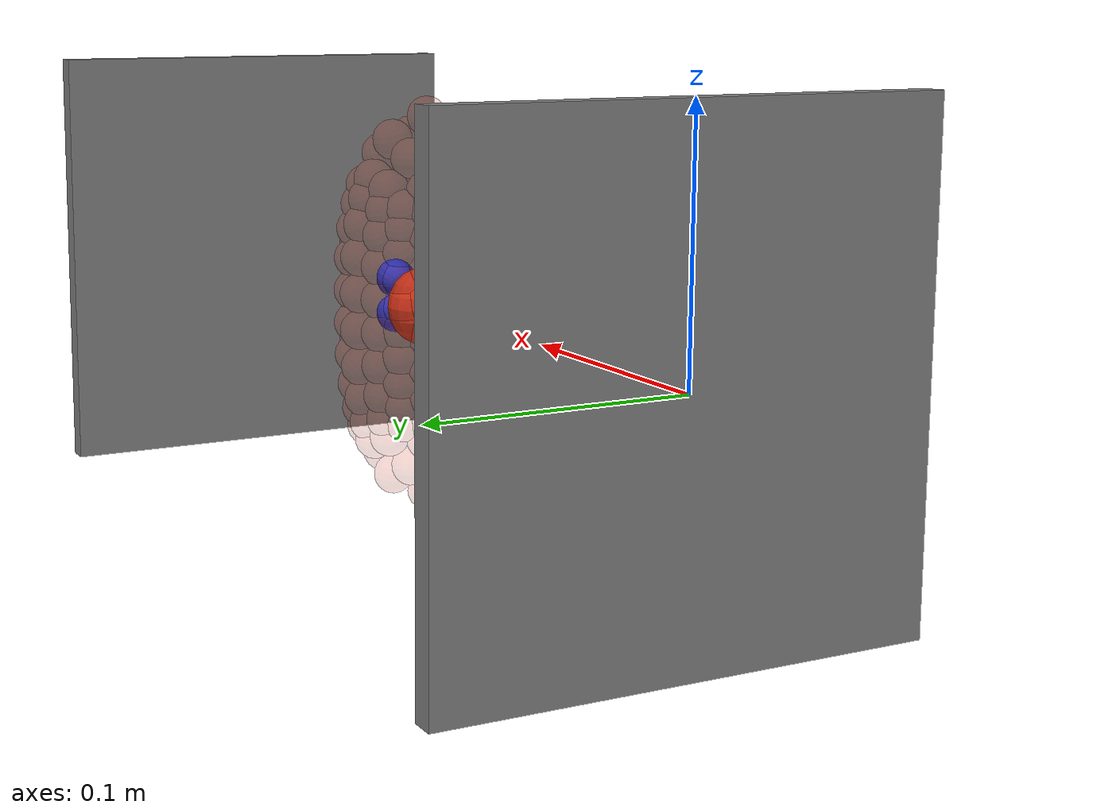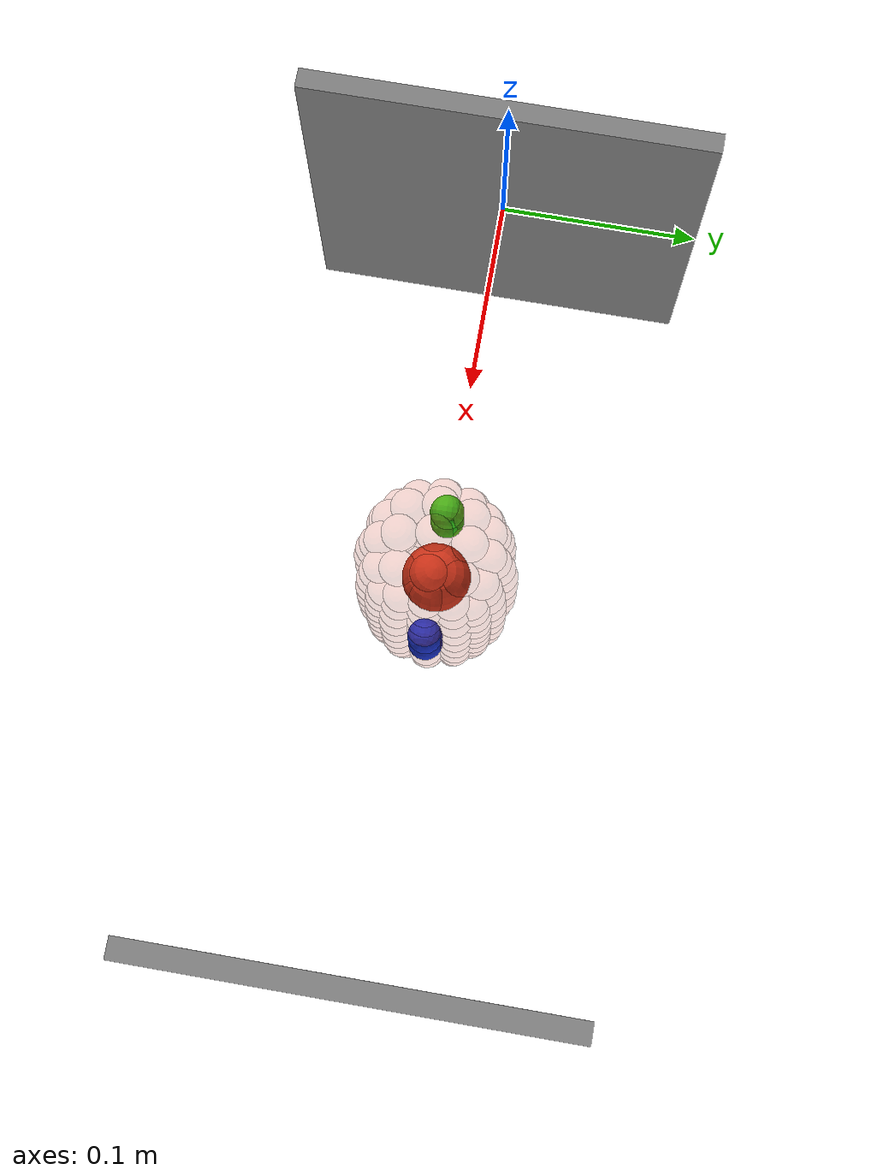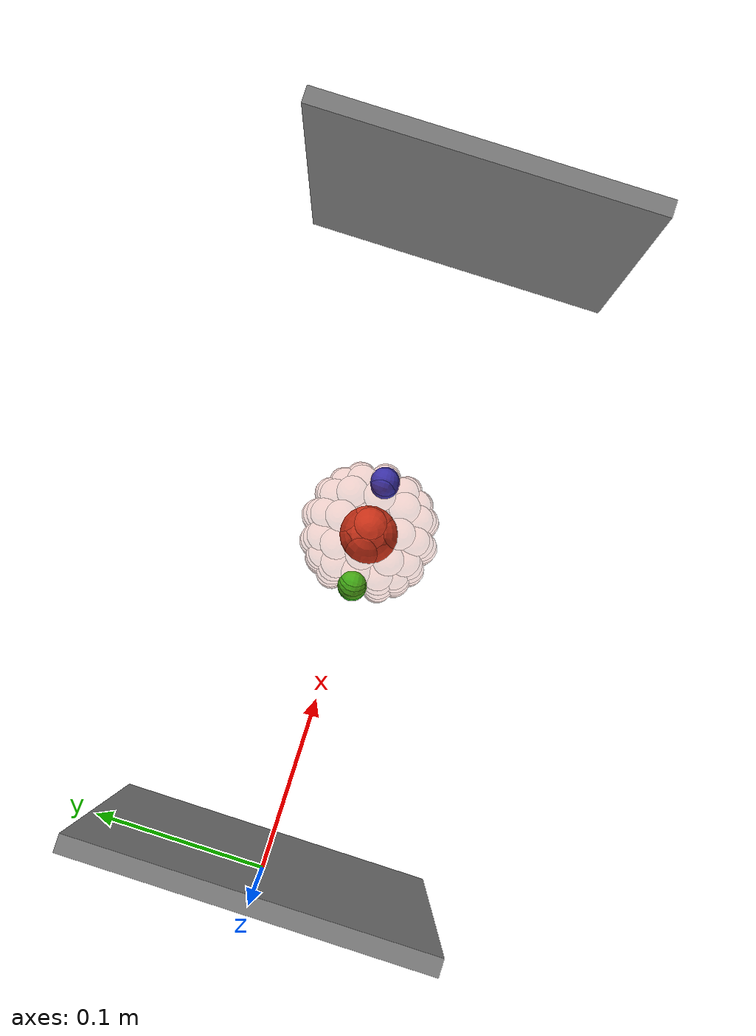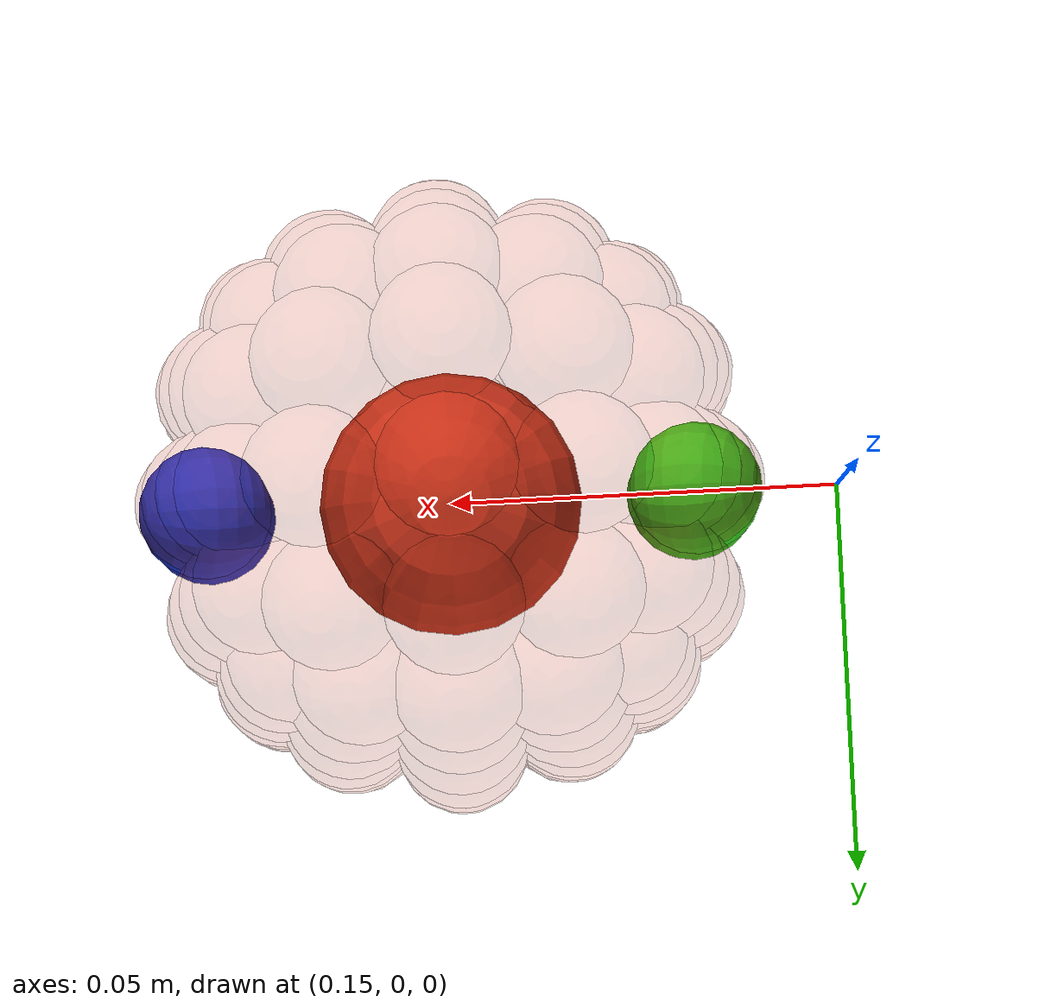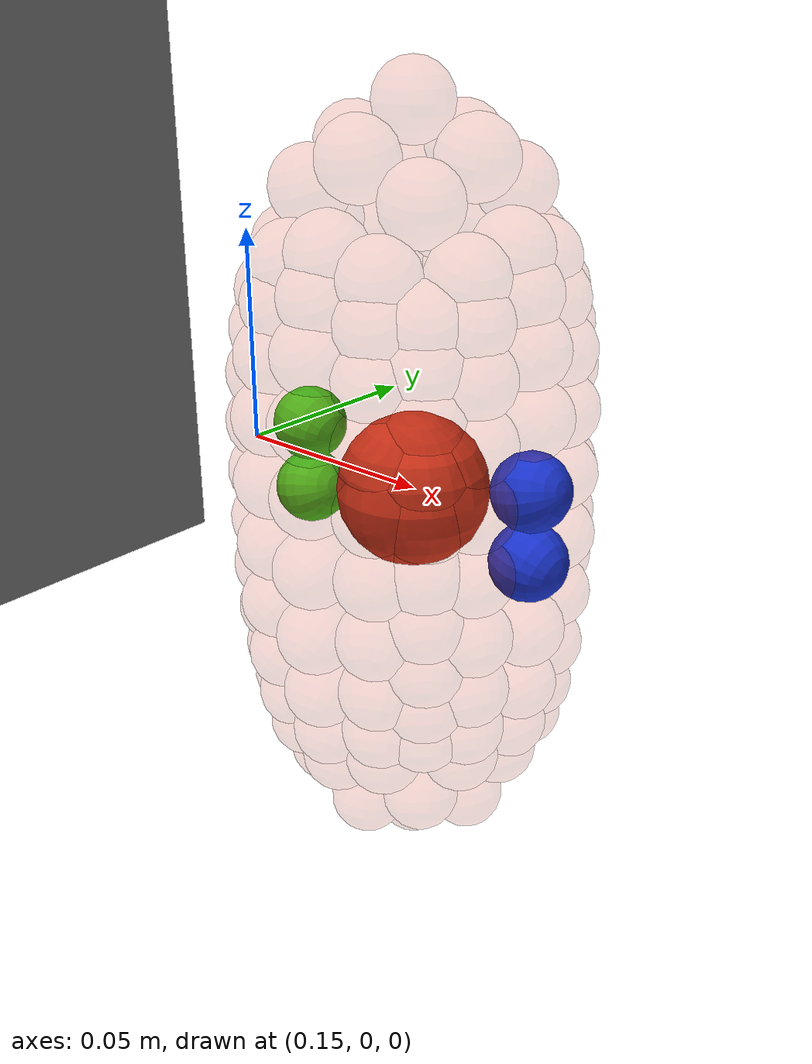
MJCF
<mujoco model="Compression test">
    <compiler angle="radian"/>
    <option tolerance="1e-09" jacobian="sparse" iterations="200"/>
    <size njmax="9000" nconmax="2000"/>
    <worldbody>
        <light pos="0.9 0.3 2.5" dir="-0.336581 -0.112194 -0.934947" directional="true" cutoff="4" exponent="20" diffuse="1 1 1" specular="0 0 0"/>
        <body name="wall" pos="0 0 0">
            <inertial pos="0 0 0" mass="0.4" diaginertia="0.00266667 0.00133667 0.00133667"/>
            <geom size="0.005 0.1 0.1" type="box"/>
            <body name="compressor" pos="0.4 0 0">
                <inertial pos="0 0 0" mass="0.4" diaginertia="0.00266667 0.00133667 0.00133667"/>
                <joint name="compressor_slide" pos="0 0 0" axis="1 0 0" type="slide" limited="true" range="-1 1"/>
                <geom size="0.005 0.1 0.1" type="box"/>
            </body>
        </body>
        <body name="test_collider" pos="0.2 0 0">
            <inertial pos="0 0 0" mass="0.01" diaginertia="1.156e-06 1.156e-06 1.156e-06"/>
            <joint pos="0 0 0" axis="1 0 0" type="slide"/>
            <geom name="cmp_Gcenter" size="0.017" contype="0" rgba="0.8 0.2 0.1 1"/>
            <body name="cmp_B0_0_0" pos="-0.023094 -0.023094 -0.0519615" quat="0.276904 0.679457 -0.679457 0">
                <inertial pos="0 0 -0.0085" mass="0.01" diaginertia="2.89e-07 2.89e-07 2.89e-07"/>
                <joint name="cmp_J0_0_0" pos="0 0 0" axis="0 0 1" type="slide" group="3"/>
                <geom name="cmp_G0_0_0" size="0.0085" pos="0 0 -0.0085" contype="0" rgba="0.8 0.2 0.1 0.2"/>
            </body>
            <body name="cmp_B0_0_1" pos="-0.0247834 -0.0247834 -0.043371" quat="0.333333 0.666667 -0.666667 0">
                <inertial pos="0 0 -0.0085" mass="0.01" diaginertia="2.89e-07 2.89e-07 2.89e-07"/>
                <joint name="cmp_J0_0_1" pos="0 0 0" axis="0 0 1" type="slide" group="3"/>
                <geom name="cmp_G0_0_1" size="0.0085" pos="0 0 -0.0085" contype="0" rgba="0.8 0.2 0.1 0.2"/>
            </body>
            <body name="cmp_B0_0_2" pos="-0.0263258 -0.0263258 -0.0329073" quat="0.410934 0.644645 -0.644645 0">
                <inertial pos="0 0 -0.0085" mass="0.01" diaginertia="2.89e-07 2.89e-07 2.89e-07"/>
                <joint name="cmp_J0_0_2" pos="0 0 0" axis="0 0 1" type="slide" group="3"/>
                <geom name="cmp_G0_0_2" size="0.0085" pos="0 0 -0.0085" contype="0" rgba="0.8 0.2 0.1 0.2"/>
            </body>
            <body name="cmp_B0_0_3" pos="-0.0275299 -0.0275299 -0.0206474" quat="0.515499 0.605913 -0.605913 0">
                <inertial pos="0 0 -0.0085" mass="0.01" diaginertia="2.89e-07 2.89e-07 2.89e-07"/>
                <joint name="cmp_J0_0_3" pos="0 0 0" axis="0 0 1" type="slide" group="3"/>
                <geom name="cmp_G0_0_3" size="0.0085" pos="0 0 -0.0085" contype="0" rgba="0.8 0.2 0.1 0.2"/>
            </body>
            <body name="cmp_B0_0_4" pos="-0.0281974 -0.0281974 -0.00704934" quat="0.642621 0.541774 -0.541774 0">
                <inertial pos="0 0 -0.0085" mass="0.01" diaginertia="2.89e-07 2.89e-07 2.89e-07"/>
                <joint name="cmp_J0_0_4" pos="0 0 0" axis="0 0 1" type="slide" group="3"/>
                <geom name="cmp_G0_0_4" size="0.0085" pos="0 0 -0.0085" contype="0" rgba="0.8 0.2 0.1 0.2"/>
            </body>
            <body name="cmp_B0_0_5" pos="-0.0281974 -0.0281974 0.00704934" quat="0.766185 0.454401 -0.454401 0">
                <inertial pos="0 0 -0.0085" mass="0.01" diaginertia="2.89e-07 2.89e-07 2.89e-07"/>
                <joint name="cmp_J0_0_5" pos="0 0 0" axis="0 0 1" type="slide" group="3"/>
                <geom name="cmp_G0_0_5" size="0.0085" pos="0 0 -0.0085" contype="0" rgba="0.8 0.2 0.1 0.2"/>
            </body>
            <body name="cmp_B0_0_6" pos="-0.0275299 -0.0275299 0.0206474" quat="0.85689 0.364513 -0.364513 0">
                <inertial pos="0 0 -0.0085" mass="0.01" diaginertia="2.89e-07 2.89e-07 2.89e-07"/>
                <joint name="cmp_J0_0_6" pos="0 0 0" axis="0 0 1" type="slide" group="3"/>
                <geom name="cmp_G0_0_6" size="0.0085" pos="0 0 -0.0085" contype="0" rgba="0.8 0.2 0.1 0.2"/>
            </body>
            <body name="cmp_B0_0_7" pos="-0.0263258 -0.0263258 0.0329073" quat="0.911665 0.290574 -0.290574 0">
                <inertial pos="0 0 -0.0085" mass="0.01" diaginertia="2.89e-07 2.89e-07 2.89e-07"/>
                <joint name="cmp_J0_0_7" pos="0 0 0" axis="0 0 1" type="slide" group="3"/>
                <geom name="cmp_G0_0_7" size="0.0085" pos="0 0 -0.0085" contype="0" rgba="0.8 0.2 0.1 0.2"/>
            </body>
            <body name="cmp_B0_0_8" pos="-0.0247834 -0.0247834 0.043371" quat="0.942809 0.235702 -0.235702 0">
                <inertial pos="0 0 -0.0085" mass="0.01" diaginertia="2.89e-07 2.89e-07 2.89e-07"/>
                <joint name="cmp_J0_0_8" pos="0 0 0" axis="0 0 1" type="slide" group="3"/>
                <geom name="cmp_G0_0_8" size="0.0085" pos="0 0 -0.0085" contype="0" rgba="0.8 0.2 0.1 0.2"/>
            </body>
            <body name="cmp_B0_0_9" pos="-0.023094 -0.023094 0.0519615" quat="0.960898 0.1958 -0.1958 0">
                <inertial pos="0 0 -0.0085" mass="0.01" diaginertia="2.89e-07 2.89e-07 2.89e-07"/>
                <joint name="cmp_J0_0_9" pos="0 0 0" axis="0 0 1" type="slide" group="3"/>
                <geom name="cmp_G0_0_9" size="0.0085" pos="0 0 -0.0085" contype="0" rgba="0.8 0.2 0.1 0.2"/>
            </body>
            <body name="cmp_B0_1_0" pos="-0.0266667 -0.0133333 -0.06" quat="0.228546 0.435377 -0.870754 0">
                <inertial pos="0 0 -0.0085" mass="0.01" diaginertia="2.89e-07 2.89e-07 2.89e-07"/>
                <joint name="cmp_J0_1_0" pos="0 0 0" axis="0 0 1" type="slide" group="3"/>
                <geom name="cmp_G0_1_0" size="0.0085" pos="0 0 -0.0085" contype="0" rgba="0.8 0.2 0.1 0.2"/>
            </body>
            <body name="cmp_B0_1_1" pos="-0.0293694 -0.0146847 -0.0513965" quat="0.280445 0.429267 -0.858534 0">
                <inertial pos="0 0 -0.0085" mass="0.01" diaginertia="2.89e-07 2.89e-07 2.89e-07"/>
                <joint name="cmp_J0_1_1" pos="0 0 0" axis="0 0 1" type="slide" group="3"/>
                <geom name="cmp_G0_1_1" size="0.0085" pos="0 0 -0.0085" contype="0" rgba="0.8 0.2 0.1 0.2"/>
            </body>
            <body name="cmp_B0_1_2" pos="-0.0320396 -0.0160198 -0.0400495" quat="0.356822 0.417775 -0.835549 0">
                <inertial pos="0 0 -0.0085" mass="0.01" diaginertia="2.89e-07 2.89e-07 2.89e-07"/>
                <joint name="cmp_J0_1_2" pos="0 0 0" axis="0 0 1" type="slide" group="3"/>
                <geom name="cmp_G0_1_2" size="0.0085" pos="0 0 -0.0085" contype="0" rgba="0.8 0.2 0.1 0.2"/>
            </body>
            <body name="cmp_B0_1_3" pos="-0.0342857 -0.0171429 -0.0257143" quat="0.470592 0.394599 -0.789199 0">
                <inertial pos="0 0 -0.0085" mass="0.01" diaginertia="2.89e-07 2.89e-07 2.89e-07"/>
                <joint name="cmp_J0_1_3" pos="0 0 0" axis="0 0 1" type="slide" group="3"/>
                <geom name="cmp_G0_1_3" size="0.0085" pos="0 0 -0.0085" contype="0" rgba="0.8 0.2 0.1 0.2"/>
            </body>
            <body name="cmp_B0_1_4" pos="-0.0356017 -0.0178009 -0.00890043" quat="0.625213 0.34903 -0.69806 0">
                <inertial pos="0 0 -0.0085" mass="0.01" diaginertia="2.89e-07 2.89e-07 2.89e-07"/>
                <joint name="cmp_J0_1_4" pos="0 0 0" axis="0 0 1" type="slide" group="3"/>
                <geom name="cmp_G0_1_4" size="0.0085" pos="0 0 -0.0085" contype="0" rgba="0.8 0.2 0.1 0.2"/>
            </body>
            <body name="cmp_B0_1_5" pos="-0.0356017 -0.0178009 0.00890043" quat="0.780454 0.279604 -0.559207 0">
                <inertial pos="0 0 -0.0085" mass="0.01" diaginertia="2.89e-07 2.89e-07 2.89e-07"/>
                <joint name="cmp_J0_1_5" pos="0 0 0" axis="0 0 1" type="slide" group="3"/>
                <geom name="cmp_G0_1_5" size="0.0085" pos="0 0 -0.0085" contype="0" rgba="0.8 0.2 0.1 0.2"/>
            </body>
            <body name="cmp_B0_1_6" pos="-0.0342857 -0.0171429 0.0257143" quat="0.882351 0.210455 -0.42091 0">
                <inertial pos="0 0 -0.0085" mass="0.01" diaginertia="2.89e-07 2.89e-07 2.89e-07"/>
                <joint name="cmp_J0_1_6" pos="0 0 0" axis="0 0 1" type="slide" group="3"/>
                <geom name="cmp_G0_1_6" size="0.0085" pos="0 0 -0.0085" contype="0" rgba="0.8 0.2 0.1 0.2"/>
            </body>
            <body name="cmp_B0_1_7" pos="-0.0320396 -0.0160198 0.0400495" quat="0.934172 0.159576 -0.319151 0">
                <inertial pos="0 0 -0.0085" mass="0.01" diaginertia="2.89e-07 2.89e-07 2.89e-07"/>
                <joint name="cmp_J0_1_7" pos="0 0 0" axis="0 0 1" type="slide" group="3"/>
                <geom name="cmp_G0_1_7" size="0.0085" pos="0 0 -0.0085" contype="0" rgba="0.8 0.2 0.1 0.2"/>
            </body>
            <body name="cmp_B0_1_8" pos="-0.0293694 -0.0146847 0.0513965" quat="0.95987 0.125419 -0.250838 0">
                <inertial pos="0 0 -0.0085" mass="0.01" diaginertia="2.89e-07 2.89e-07 2.89e-07"/>
                <joint name="cmp_J0_1_8" pos="0 0 0" axis="0 0 1" type="slide" group="3"/>
                <geom name="cmp_G0_1_8" size="0.0085" pos="0 0 -0.0085" contype="0" rgba="0.8 0.2 0.1 0.2"/>
            </body>
            <body name="cmp_B0_1_9" pos="-0.0266667 -0.0133333 0.06" quat="0.973533 0.102209 -0.204418 0">
                <inertial pos="0 0 -0.0085" mass="0.01" diaginertia="2.89e-07 2.89e-07 2.89e-07"/>
                <joint name="cmp_J0_1_9" pos="0 0 0" axis="0 0 1" type="slide" group="3"/>
                <geom name="cmp_G0_1_9" size="0.0085" pos="0 0 -0.0085" contype="0" rgba="0.8 0.2 0.1 0.2"/>
            </body>
            <body name="cmp_B0_2_0" pos="-0.0282843 0 -0.0636396" quat="0.207591 0 -0.978216 0">
                <inertial pos="0 0 -0.0085" mass="0.01" diaginertia="2.89e-07 2.89e-07 2.89e-07"/>
                <joint name="cmp_J0_2_0" pos="0 0 0" axis="0 0 1" type="slide" group="3"/>
                <geom name="cmp_G0_2_0" size="0.0085" pos="0 0 -0.0085" contype="0" rgba="0.8 0.2 0.1 0.2"/>
            </body>
            <body name="cmp_B0_2_1" pos="-0.0315741 0 -0.0552547" quat="0.256668 0 -0.9665 0">
                <inertial pos="0 0 -0.0085" mass="0.01" diaginertia="2.89e-07 2.89e-07 2.89e-07"/>
                <joint name="cmp_J0_2_1" pos="0 0 0" axis="0 0 1" type="slide" group="3"/>
                <geom name="cmp_G0_2_1" size="0.0085" pos="0 0 -0.0085" contype="0" rgba="0.8 0.2 0.1 0.2"/>
            </body>
            <body name="cmp_B0_2_2" pos="-0.0349663 0 -0.0437079" quat="0.331007 0 -0.943628 0">
                <inertial pos="0 0 -0.0085" mass="0.01" diaginertia="2.89e-07 2.89e-07 2.89e-07"/>
                <joint name="cmp_J0_2_2" pos="0 0 0" axis="0 0 1" type="slide" group="3"/>
                <geom name="cmp_G0_2_2" size="0.0085" pos="0 0 -0.0085" contype="0" rgba="0.8 0.2 0.1 0.2"/>
            </body>
            <body name="cmp_B0_2_3" pos="-0.0379473 0 -0.0284605" quat="0.447214 0 -0.894427 0">
                <inertial pos="0 0 -0.0085" mass="0.01" diaginertia="2.89e-07 2.89e-07 2.89e-07"/>
                <joint name="cmp_J0_2_3" pos="0 0 0" axis="0 0 1" type="slide" group="3"/>
                <geom name="cmp_G0_2_3" size="0.0085" pos="0 0 -0.0085" contype="0" rgba="0.8 0.2 0.1 0.2"/>
            </body>
            <body name="cmp_B0_2_4" pos="-0.0397553 0 -0.00993884" quat="0.615412 0 -0.788205 0">
                <inertial pos="0 0 -0.0085" mass="0.01" diaginertia="2.89e-07 2.89e-07 2.89e-07"/>
                <joint name="cmp_J0_2_4" pos="0 0 0" axis="0 0 1" type="slide" group="3"/>
                <geom name="cmp_G0_2_4" size="0.0085" pos="0 0 -0.0085" contype="0" rgba="0.2 0.8 0.1 1"/>
            </body>
            <body name="cmp_B0_2_5" pos="-0.0397553 0 0.00993884" quat="0.788205 0 -0.615412 0">
                <inertial pos="0 0 -0.0085" mass="0.01" diaginertia="2.89e-07 2.89e-07 2.89e-07"/>
                <joint name="cmp_J0_2_5" pos="0 0 0" axis="0 0 1" type="slide" group="3"/>
                <geom name="cmp_G0_2_5" size="0.0085" pos="0 0 -0.0085" contype="0" rgba="0.2 0.8 0.1 1"/>
            </body>
            <body name="cmp_B0_2_6" pos="-0.0379473 0 0.0284605" quat="0.894427 0 -0.447214 0">
                <inertial pos="0 0 -0.0085" mass="0.01" diaginertia="2.89e-07 2.89e-07 2.89e-07"/>
                <joint name="cmp_J0_2_6" pos="0 0 0" axis="0 0 1" type="slide" group="3"/>
                <geom name="cmp_G0_2_6" size="0.0085" pos="0 0 -0.0085" contype="0" rgba="0.8 0.2 0.1 0.2"/>
            </body>
            <body name="cmp_B0_2_7" pos="-0.0349663 0 0.0437079" quat="0.943628 0 -0.331007 0">
                <inertial pos="0 0 -0.0085" mass="0.01" diaginertia="2.89e-07 2.89e-07 2.89e-07"/>
                <joint name="cmp_J0_2_7" pos="0 0 0" axis="0 0 1" type="slide" group="3"/>
                <geom name="cmp_G0_2_7" size="0.0085" pos="0 0 -0.0085" contype="0" rgba="0.8 0.2 0.1 0.2"/>
            </body>
            <body name="cmp_B0_2_8" pos="-0.0315741 0 0.0552547" quat="0.9665 0 -0.256668 0">
                <inertial pos="0 0 -0.0085" mass="0.01" diaginertia="2.89e-07 2.89e-07 2.89e-07"/>
                <joint name="cmp_J0_2_8" pos="0 0 0" axis="0 0 1" type="slide" group="3"/>
                <geom name="cmp_G0_2_8" size="0.0085" pos="0 0 -0.0085" contype="0" rgba="0.8 0.2 0.1 0.2"/>
            </body>
            <body name="cmp_B0_2_9" pos="-0.0282843 0 0.0636396" quat="0.978216 0 -0.207591 0">
                <inertial pos="0 0 -0.0085" mass="0.01" diaginertia="2.89e-07 2.89e-07 2.89e-07"/>
                <joint name="cmp_J0_2_9" pos="0 0 0" axis="0 0 1" type="slide" group="3"/>
                <geom name="cmp_G0_2_9" size="0.0085" pos="0 0 -0.0085" contype="0" rgba="0.8 0.2 0.1 0.2"/>
            </body>
            <body name="cmp_B0_3_0" pos="-0.0266667 0.0133333 -0.06" quat="0.228546 -0.435377 -0.870754 0">
                <inertial pos="0 0 -0.0085" mass="0.01" diaginertia="2.89e-07 2.89e-07 2.89e-07"/>
                <joint name="cmp_J0_3_0" pos="0 0 0" axis="0 0 1" type="slide" group="3"/>
                <geom name="cmp_G0_3_0" size="0.0085" pos="0 0 -0.0085" contype="0" rgba="0.8 0.2 0.1 0.2"/>
            </body>
            <body name="cmp_B0_3_1" pos="-0.0293694 0.0146847 -0.0513965" quat="0.280445 -0.429267 -0.858534 0">
                <inertial pos="0 0 -0.0085" mass="0.01" diaginertia="2.89e-07 2.89e-07 2.89e-07"/>
                <joint name="cmp_J0_3_1" pos="0 0 0" axis="0 0 1" type="slide" group="3"/>
                <geom name="cmp_G0_3_1" size="0.0085" pos="0 0 -0.0085" contype="0" rgba="0.8 0.2 0.1 0.2"/>
            </body>
            <body name="cmp_B0_3_2" pos="-0.0320396 0.0160198 -0.0400495" quat="0.356822 -0.417775 -0.835549 0">
                <inertial pos="0 0 -0.0085" mass="0.01" diaginertia="2.89e-07 2.89e-07 2.89e-07"/>
                <joint name="cmp_J0_3_2" pos="0 0 0" axis="0 0 1" type="slide" group="3"/>
                <geom name="cmp_G0_3_2" size="0.0085" pos="0 0 -0.0085" contype="0" rgba="0.8 0.2 0.1 0.2"/>
            </body>
            <body name="cmp_B0_3_3" pos="-0.0342857 0.0171429 -0.0257143" quat="0.470592 -0.394599 -0.789199 0">
                <inertial pos="0 0 -0.0085" mass="0.01" diaginertia="2.89e-07 2.89e-07 2.89e-07"/>
                <joint name="cmp_J0_3_3" pos="0 0 0" axis="0 0 1" type="slide" group="3"/>
                <geom name="cmp_G0_3_3" size="0.0085" pos="0 0 -0.0085" contype="0" rgba="0.8 0.2 0.1 0.2"/>
            </body>
            <body name="cmp_B0_3_4" pos="-0.0356017 0.0178009 -0.00890043" quat="0.625213 -0.34903 -0.69806 0">
                <inertial pos="0 0 -0.0085" mass="0.01" diaginertia="2.89e-07 2.89e-07 2.89e-07"/>
                <joint name="cmp_J0_3_4" pos="0 0 0" axis="0 0 1" type="slide" group="3"/>
                <geom name="cmp_G0_3_4" size="0.0085" pos="0 0 -0.0085" contype="0" rgba="0.8 0.2 0.1 0.2"/>
            </body>
            <body name="cmp_B0_3_5" pos="-0.0356017 0.0178009 0.00890043" quat="0.780454 -0.279604 -0.559207 0">
                <inertial pos="0 0 -0.0085" mass="0.01" diaginertia="2.89e-07 2.89e-07 2.89e-07"/>
                <joint name="cmp_J0_3_5" pos="0 0 0" axis="0 0 1" type="slide" group="3"/>
                <geom name="cmp_G0_3_5" size="0.0085" pos="0 0 -0.0085" contype="0" rgba="0.8 0.2 0.1 0.2"/>
            </body>
            <body name="cmp_B0_3_6" pos="-0.0342857 0.0171429 0.0257143" quat="0.882351 -0.210455 -0.42091 0">
                <inertial pos="0 0 -0.0085" mass="0.01" diaginertia="2.89e-07 2.89e-07 2.89e-07"/>
                <joint name="cmp_J0_3_6" pos="0 0 0" axis="0 0 1" type="slide" group="3"/>
                <geom name="cmp_G0_3_6" size="0.0085" pos="0 0 -0.0085" contype="0" rgba="0.8 0.2 0.1 0.2"/>
            </body>
            <body name="cmp_B0_3_7" pos="-0.0320396 0.0160198 0.0400495" quat="0.934172 -0.159576 -0.319151 0">
                <inertial pos="0 0 -0.0085" mass="0.01" diaginertia="2.89e-07 2.89e-07 2.89e-07"/>
                <joint name="cmp_J0_3_7" pos="0 0 0" axis="0 0 1" type="slide" group="3"/>
                <geom name="cmp_G0_3_7" size="0.0085" pos="0 0 -0.0085" contype="0" rgba="0.8 0.2 0.1 0.2"/>
            </body>
            <body name="cmp_B0_3_8" pos="-0.0293694 0.0146847 0.0513965" quat="0.95987 -0.125419 -0.250838 0">
                <inertial pos="0 0 -0.0085" mass="0.01" diaginertia="2.89e-07 2.89e-07 2.89e-07"/>
                <joint name="cmp_J0_3_8" pos="0 0 0" axis="0 0 1" type="slide" group="3"/>
                <geom name="cmp_G0_3_8" size="0.0085" pos="0 0 -0.0085" contype="0" rgba="0.8 0.2 0.1 0.2"/>
            </body>
            <body name="cmp_B0_3_9" pos="-0.0266667 0.0133333 0.06" quat="0.973533 -0.102209 -0.204418 0">
                <inertial pos="0 0 -0.0085" mass="0.01" diaginertia="2.89e-07 2.89e-07 2.89e-07"/>
                <joint name="cmp_J0_3_9" pos="0 0 0" axis="0 0 1" type="slide" group="3"/>
                <geom name="cmp_G0_3_9" size="0.0085" pos="0 0 -0.0085" contype="0" rgba="0.8 0.2 0.1 0.2"/>
            </body>
            <body name="cmp_B0_4_0" pos="-0.023094 0.023094 -0.0519615" quat="0.276904 -0.679457 -0.679457 0">
                <inertial pos="0 0 -0.0085" mass="0.01" diaginertia="2.89e-07 2.89e-07 2.89e-07"/>
                <joint name="cmp_J0_4_0" pos="0 0 0" axis="0 0 1" type="slide" group="3"/>
                <geom name="cmp_G0_4_0" size="0.0085" pos="0 0 -0.0085" contype="0" rgba="0.8 0.2 0.1 0.2"/>
            </body>
            <body name="cmp_B0_4_1" pos="-0.0247834 0.0247834 -0.043371" quat="0.333333 -0.666667 -0.666667 0">
                <inertial pos="0 0 -0.0085" mass="0.01" diaginertia="2.89e-07 2.89e-07 2.89e-07"/>
                <joint name="cmp_J0_4_1" pos="0 0 0" axis="0 0 1" type="slide" group="3"/>
                <geom name="cmp_G0_4_1" size="0.0085" pos="0 0 -0.0085" contype="0" rgba="0.8 0.2 0.1 0.2"/>
            </body>
            <body name="cmp_B0_4_2" pos="-0.0263258 0.0263258 -0.0329073" quat="0.410934 -0.644645 -0.644645 0">
                <inertial pos="0 0 -0.0085" mass="0.01" diaginertia="2.89e-07 2.89e-07 2.89e-07"/>
                <joint name="cmp_J0_4_2" pos="0 0 0" axis="0 0 1" type="slide" group="3"/>
                <geom name="cmp_G0_4_2" size="0.0085" pos="0 0 -0.0085" contype="0" rgba="0.8 0.2 0.1 0.2"/>
            </body>
            <body name="cmp_B0_4_3" pos="-0.0275299 0.0275299 -0.0206474" quat="0.515499 -0.605913 -0.605913 0">
                <inertial pos="0 0 -0.0085" mass="0.01" diaginertia="2.89e-07 2.89e-07 2.89e-07"/>
                <joint name="cmp_J0_4_3" pos="0 0 0" axis="0 0 1" type="slide" group="3"/>
                <geom name="cmp_G0_4_3" size="0.0085" pos="0 0 -0.0085" contype="0" rgba="0.8 0.2 0.1 0.2"/>
            </body>
            <body name="cmp_B0_4_4" pos="-0.0281974 0.0281974 -0.00704934" quat="0.642621 -0.541774 -0.541774 0">
                <inertial pos="0 0 -0.0085" mass="0.01" diaginertia="2.89e-07 2.89e-07 2.89e-07"/>
                <joint name="cmp_J0_4_4" pos="0 0 0" axis="0 0 1" type="slide" group="3"/>
                <geom name="cmp_G0_4_4" size="0.0085" pos="0 0 -0.0085" contype="0" rgba="0.8 0.2 0.1 0.2"/>
            </body>
            <body name="cmp_B0_4_5" pos="-0.0281974 0.0281974 0.00704934" quat="0.766185 -0.454401 -0.454401 0">
                <inertial pos="0 0 -0.0085" mass="0.01" diaginertia="2.89e-07 2.89e-07 2.89e-07"/>
                <joint name="cmp_J0_4_5" pos="0 0 0" axis="0 0 1" type="slide" group="3"/>
                <geom name="cmp_G0_4_5" size="0.0085" pos="0 0 -0.0085" contype="0" rgba="0.8 0.2 0.1 0.2"/>
            </body>
            <body name="cmp_B0_4_6" pos="-0.0275299 0.0275299 0.0206474" quat="0.85689 -0.364513 -0.364513 0">
                <inertial pos="0 0 -0.0085" mass="0.01" diaginertia="2.89e-07 2.89e-07 2.89e-07"/>
                <joint name="cmp_J0_4_6" pos="0 0 0" axis="0 0 1" type="slide" group="3"/>
                <geom name="cmp_G0_4_6" size="0.0085" pos="0 0 -0.0085" contype="0" rgba="0.8 0.2 0.1 0.2"/>
            </body>
            <body name="cmp_B0_4_7" pos="-0.0263258 0.0263258 0.0329073" quat="0.911665 -0.290574 -0.290574 0">
                <inertial pos="0 0 -0.0085" mass="0.01" diaginertia="2.89e-07 2.89e-07 2.89e-07"/>
                <joint name="cmp_J0_4_7" pos="0 0 0" axis="0 0 1" type="slide" group="3"/>
                <geom name="cmp_G0_4_7" size="0.0085" pos="0 0 -0.0085" contype="0" rgba="0.8 0.2 0.1 0.2"/>
            </body>
            <body name="cmp_B0_4_8" pos="-0.0247834 0.0247834 0.043371" quat="0.942809 -0.235702 -0.235702 0">
                <inertial pos="0 0 -0.0085" mass="0.01" diaginertia="2.89e-07 2.89e-07 2.89e-07"/>
                <joint name="cmp_J0_4_8" pos="0 0 0" axis="0 0 1" type="slide" group="3"/>
                <geom name="cmp_G0_4_8" size="0.0085" pos="0 0 -0.0085" contype="0" rgba="0.8 0.2 0.1 0.2"/>
            </body>
            <body name="cmp_B0_4_9" pos="-0.023094 0.023094 0.0519615" quat="0.960898 -0.1958 -0.1958 0">
                <inertial pos="0 0 -0.0085" mass="0.01" diaginertia="2.89e-07 2.89e-07 2.89e-07"/>
                <joint name="cmp_J0_4_9" pos="0 0 0" axis="0 0 1" type="slide" group="3"/>
                <geom name="cmp_G0_4_9" size="0.0085" pos="0 0 -0.0085" contype="0" rgba="0.8 0.2 0.1 0.2"/>
            </body>
            <body name="cmp_B1_0_0" pos="-0.0133333 -0.0266667 -0.06" quat="0.228546 0.870754 -0.435377 0">
                <inertial pos="0 0 -0.0085" mass="0.01" diaginertia="2.89e-07 2.89e-07 2.89e-07"/>
                <joint name="cmp_J1_0_0" pos="0 0 0" axis="0 0 1" type="slide" group="3"/>
                <geom name="cmp_G1_0_0" size="0.0085" pos="0 0 -0.0085" contype="0" rgba="0.8 0.2 0.1 0.2"/>
            </body>
            <body name="cmp_B1_0_1" pos="-0.0146847 -0.0293694 -0.0513965" quat="0.280445 0.858534 -0.429267 0">
                <inertial pos="0 0 -0.0085" mass="0.01" diaginertia="2.89e-07 2.89e-07 2.89e-07"/>
                <joint name="cmp_J1_0_1" pos="0 0 0" axis="0 0 1" type="slide" group="3"/>
                <geom name="cmp_G1_0_1" size="0.0085" pos="0 0 -0.0085" contype="0" rgba="0.8 0.2 0.1 0.2"/>
            </body>
            <body name="cmp_B1_0_2" pos="-0.0160198 -0.0320396 -0.0400495" quat="0.356822 0.835549 -0.417775 0">
                <inertial pos="0 0 -0.0085" mass="0.01" diaginertia="2.89e-07 2.89e-07 2.89e-07"/>
                <joint name="cmp_J1_0_2" pos="0 0 0" axis="0 0 1" type="slide" group="3"/>
                <geom name="cmp_G1_0_2" size="0.0085" pos="0 0 -0.0085" contype="0" rgba="0.8 0.2 0.1 0.2"/>
            </body>
            <body name="cmp_B1_0_3" pos="-0.0171429 -0.0342857 -0.0257143" quat="0.470592 0.789199 -0.394599 0">
                <inertial pos="0 0 -0.0085" mass="0.01" diaginertia="2.89e-07 2.89e-07 2.89e-07"/>
                <joint name="cmp_J1_0_3" pos="0 0 0" axis="0 0 1" type="slide" group="3"/>
                <geom name="cmp_G1_0_3" size="0.0085" pos="0 0 -0.0085" contype="0" rgba="0.8 0.2 0.1 0.2"/>
            </body>
            <body name="cmp_B1_0_4" pos="-0.0178009 -0.0356017 -0.00890043" quat="0.625213 0.69806 -0.34903 0">
                <inertial pos="0 0 -0.0085" mass="0.01" diaginertia="2.89e-07 2.89e-07 2.89e-07"/>
                <joint name="cmp_J1_0_4" pos="0 0 0" axis="0 0 1" type="slide" group="3"/>
                <geom name="cmp_G1_0_4" size="0.0085" pos="0 0 -0.0085" contype="0" rgba="0.8 0.2 0.1 0.2"/>
            </body>
            <body name="cmp_B1_0_5" pos="-0.0178009 -0.0356017 0.00890043" quat="0.780454 0.559207 -0.279604 0">
                <inertial pos="0 0 -0.0085" mass="0.01" diaginertia="2.89e-07 2.89e-07 2.89e-07"/>
                <joint name="cmp_J1_0_5" pos="0 0 0" axis="0 0 1" type="slide" group="3"/>
                <geom name="cmp_G1_0_5" size="0.0085" pos="0 0 -0.0085" contype="0" rgba="0.8 0.2 0.1 0.2"/>
            </body>
            <body name="cmp_B1_0_6" pos="-0.0171429 -0.0342857 0.0257143" quat="0.882351 0.42091 -0.210455 0">
                <inertial pos="0 0 -0.0085" mass="0.01" diaginertia="2.89e-07 2.89e-07 2.89e-07"/>
                <joint name="cmp_J1_0_6" pos="0 0 0" axis="0 0 1" type="slide" group="3"/>
                <geom name="cmp_G1_0_6" size="0.0085" pos="0 0 -0.0085" contype="0" rgba="0.8 0.2 0.1 0.2"/>
            </body>
            <body name="cmp_B1_0_7" pos="-0.0160198 -0.0320396 0.0400495" quat="0.934172 0.319151 -0.159576 0">
                <inertial pos="0 0 -0.0085" mass="0.01" diaginertia="2.89e-07 2.89e-07 2.89e-07"/>
                <joint name="cmp_J1_0_7" pos="0 0 0" axis="0 0 1" type="slide" group="3"/>
                <geom name="cmp_G1_0_7" size="0.0085" pos="0 0 -0.0085" contype="0" rgba="0.8 0.2 0.1 0.2"/>
            </body>
            <body name="cmp_B1_0_8" pos="-0.0146847 -0.0293694 0.0513965" quat="0.95987 0.250838 -0.125419 0">
                <inertial pos="0 0 -0.0085" mass="0.01" diaginertia="2.89e-07 2.89e-07 2.89e-07"/>
                <joint name="cmp_J1_0_8" pos="0 0 0" axis="0 0 1" type="slide" group="3"/>
                <geom name="cmp_G1_0_8" size="0.0085" pos="0 0 -0.0085" contype="0" rgba="0.8 0.2 0.1 0.2"/>
            </body>
            <body name="cmp_B1_0_9" pos="-0.0133333 -0.0266667 0.06" quat="0.973533 0.204418 -0.102209 0">
                <inertial pos="0 0 -0.0085" mass="0.01" diaginertia="2.89e-07 2.89e-07 2.89e-07"/>
                <joint name="cmp_J1_0_9" pos="0 0 0" axis="0 0 1" type="slide" group="3"/>
                <geom name="cmp_G1_0_9" size="0.0085" pos="0 0 -0.0085" contype="0" rgba="0.8 0.2 0.1 0.2"/>
            </body>
            <body name="cmp_B1_1_0" pos="-0.0163299 -0.0163299 -0.0734847" quat="0.151661 0.698927 -0.698927 0">
                <inertial pos="0 0 -0.0085" mass="0.01" diaginertia="2.89e-07 2.89e-07 2.89e-07"/>
                <joint name="cmp_J1_1_0" pos="0 0 0" axis="0 0 1" type="slide" group="3"/>
                <geom name="cmp_G1_1_0" size="0.0085" pos="0 0 -0.0085" contype="0" rgba="0.8 0.2 0.1 0.2"/>
            </body>
            <body name="cmp_B1_1_9" pos="-0.0163299 -0.0163299 0.0734847" quat="0.988433 0.10724 -0.10724 0">
                <inertial pos="0 0 -0.0085" mass="0.01" diaginertia="2.89e-07 2.89e-07 2.89e-07"/>
                <joint name="cmp_J1_1_9" pos="0 0 0" axis="0 0 1" type="slide" group="3"/>
                <geom name="cmp_G1_1_9" size="0.0085" pos="0 0 -0.0085" contype="0" rgba="0.8 0.2 0.1 0.2"/>
            </body>
            <body name="cmp_B1_2_0" pos="-0.0178885 0 -0.0804984" quat="0.109117 0 -0.994029 0">
                <inertial pos="0 0 -0.0085" mass="0.01" diaginertia="2.89e-07 2.89e-07 2.89e-07"/>
                <joint name="cmp_J1_2_0" pos="0 0 0" axis="0 0 1" type="slide" group="3"/>
                <geom name="cmp_G1_2_0" size="0.0085" pos="0 0 -0.0085" contype="0" rgba="0.8 0.2 0.1 0.2"/>
            </body>
            <body name="cmp_B1_2_9" pos="-0.0178885 0 0.0804984" quat="0.994029 0 -0.109117 0">
                <inertial pos="0 0 -0.0085" mass="0.01" diaginertia="2.89e-07 2.89e-07 2.89e-07"/>
                <joint name="cmp_J1_2_9" pos="0 0 0" axis="0 0 1" type="slide" group="3"/>
                <geom name="cmp_G1_2_9" size="0.0085" pos="0 0 -0.0085" contype="0" rgba="0.8 0.2 0.1 0.2"/>
            </body>
            <body name="cmp_B1_3_0" pos="-0.0163299 0.0163299 -0.0734847" quat="0.151661 -0.698927 -0.698927 0">
                <inertial pos="0 0 -0.0085" mass="0.01" diaginertia="2.89e-07 2.89e-07 2.89e-07"/>
                <joint name="cmp_J1_3_0" pos="0 0 0" axis="0 0 1" type="slide" group="3"/>
                <geom name="cmp_G1_3_0" size="0.0085" pos="0 0 -0.0085" contype="0" rgba="0.8 0.2 0.1 0.2"/>
            </body>
            <body name="cmp_B1_3_9" pos="-0.0163299 0.0163299 0.0734847" quat="0.988433 -0.10724 -0.10724 0">
                <inertial pos="0 0 -0.0085" mass="0.01" diaginertia="2.89e-07 2.89e-07 2.89e-07"/>
                <joint name="cmp_J1_3_9" pos="0 0 0" axis="0 0 1" type="slide" group="3"/>
                <geom name="cmp_G1_3_9" size="0.0085" pos="0 0 -0.0085" contype="0" rgba="0.8 0.2 0.1 0.2"/>
            </body>
            <body name="cmp_B1_4_0" pos="-0.0133333 0.0266667 -0.06" quat="0.228546 -0.870754 -0.435377 0">
                <inertial pos="0 0 -0.0085" mass="0.01" diaginertia="2.89e-07 2.89e-07 2.89e-07"/>
                <joint name="cmp_J1_4_0" pos="0 0 0" axis="0 0 1" type="slide" group="3"/>
                <geom name="cmp_G1_4_0" size="0.0085" pos="0 0 -0.0085" contype="0" rgba="0.8 0.2 0.1 0.2"/>
            </body>
            <body name="cmp_B1_4_1" pos="-0.0146847 0.0293694 -0.0513965" quat="0.280445 -0.858534 -0.429267 0">
                <inertial pos="0 0 -0.0085" mass="0.01" diaginertia="2.89e-07 2.89e-07 2.89e-07"/>
                <joint name="cmp_J1_4_1" pos="0 0 0" axis="0 0 1" type="slide" group="3"/>
                <geom name="cmp_G1_4_1" size="0.0085" pos="0 0 -0.0085" contype="0" rgba="0.8 0.2 0.1 0.2"/>
            </body>
            <body name="cmp_B1_4_2" pos="-0.0160198 0.0320396 -0.0400495" quat="0.356822 -0.835549 -0.417775 0">
                <inertial pos="0 0 -0.0085" mass="0.01" diaginertia="2.89e-07 2.89e-07 2.89e-07"/>
                <joint name="cmp_J1_4_2" pos="0 0 0" axis="0 0 1" type="slide" group="3"/>
                <geom name="cmp_G1_4_2" size="0.0085" pos="0 0 -0.0085" contype="0" rgba="0.8 0.2 0.1 0.2"/>
            </body>
            <body name="cmp_B1_4_3" pos="-0.0171429 0.0342857 -0.0257143" quat="0.470592 -0.789199 -0.394599 0">
                <inertial pos="0 0 -0.0085" mass="0.01" diaginertia="2.89e-07 2.89e-07 2.89e-07"/>
                <joint name="cmp_J1_4_3" pos="0 0 0" axis="0 0 1" type="slide" group="3"/>
                <geom name="cmp_G1_4_3" size="0.0085" pos="0 0 -0.0085" contype="0" rgba="0.8 0.2 0.1 0.2"/>
            </body>
            <body name="cmp_B1_4_4" pos="-0.0178009 0.0356017 -0.00890043" quat="0.625213 -0.69806 -0.34903 0">
                <inertial pos="0 0 -0.0085" mass="0.01" diaginertia="2.89e-07 2.89e-07 2.89e-07"/>
                <joint name="cmp_J1_4_4" pos="0 0 0" axis="0 0 1" type="slide" group="3"/>
                <geom name="cmp_G1_4_4" size="0.0085" pos="0 0 -0.0085" contype="0" rgba="0.8 0.2 0.1 0.2"/>
            </body>
            <body name="cmp_B1_4_5" pos="-0.0178009 0.0356017 0.00890043" quat="0.780454 -0.559207 -0.279604 0">
                <inertial pos="0 0 -0.0085" mass="0.01" diaginertia="2.89e-07 2.89e-07 2.89e-07"/>
                <joint name="cmp_J1_4_5" pos="0 0 0" axis="0 0 1" type="slide" group="3"/>
                <geom name="cmp_G1_4_5" size="0.0085" pos="0 0 -0.0085" contype="0" rgba="0.8 0.2 0.1 0.2"/>
            </body>
            <body name="cmp_B1_4_6" pos="-0.0171429 0.0342857 0.0257143" quat="0.882351 -0.42091 -0.210455 0">
                <inertial pos="0 0 -0.0085" mass="0.01" diaginertia="2.89e-07 2.89e-07 2.89e-07"/>
                <joint name="cmp_J1_4_6" pos="0 0 0" axis="0 0 1" type="slide" group="3"/>
                <geom name="cmp_G1_4_6" size="0.0085" pos="0 0 -0.0085" contype="0" rgba="0.8 0.2 0.1 0.2"/>
            </body>
            <body name="cmp_B1_4_7" pos="-0.0160198 0.0320396 0.0400495" quat="0.934172 -0.319151 -0.159576 0">
                <inertial pos="0 0 -0.0085" mass="0.01" diaginertia="2.89e-07 2.89e-07 2.89e-07"/>
                <joint name="cmp_J1_4_7" pos="0 0 0" axis="0 0 1" type="slide" group="3"/>
                <geom name="cmp_G1_4_7" size="0.0085" pos="0 0 -0.0085" contype="0" rgba="0.8 0.2 0.1 0.2"/>
            </body>
            <body name="cmp_B1_4_8" pos="-0.0146847 0.0293694 0.0513965" quat="0.95987 -0.250838 -0.125419 0">
                <inertial pos="0 0 -0.0085" mass="0.01" diaginertia="2.89e-07 2.89e-07 2.89e-07"/>
                <joint name="cmp_J1_4_8" pos="0 0 0" axis="0 0 1" type="slide" group="3"/>
                <geom name="cmp_G1_4_8" size="0.0085" pos="0 0 -0.0085" contype="0" rgba="0.8 0.2 0.1 0.2"/>
            </body>
            <body name="cmp_B1_4_9" pos="-0.0133333 0.0266667 0.06" quat="0.973533 -0.204418 -0.102209 0">
                <inertial pos="0 0 -0.0085" mass="0.01" diaginertia="2.89e-07 2.89e-07 2.89e-07"/>
                <joint name="cmp_J1_4_9" pos="0 0 0" axis="0 0 1" type="slide" group="3"/>
                <geom name="cmp_G1_4_9" size="0.0085" pos="0 0 -0.0085" contype="0" rgba="0.8 0.2 0.1 0.2"/>
            </body>
            <body name="cmp_B2_0_0" pos="0 -0.0282843 -0.0636396" quat="0.207591 0.978216 0 0">
                <inertial pos="0 0 -0.0085" mass="0.01" diaginertia="2.89e-07 2.89e-07 2.89e-07"/>
                <joint name="cmp_J2_0_0" pos="0 0 0" axis="0 0 1" type="slide" group="3"/>
                <geom name="cmp_G2_0_0" size="0.0085" pos="0 0 -0.0085" contype="0" rgba="0.8 0.2 0.1 0.2"/>
            </body>
            <body name="cmp_B2_0_1" pos="0 -0.0315741 -0.0552547" quat="0.256668 0.9665 0 0">
                <inertial pos="0 0 -0.0085" mass="0.01" diaginertia="2.89e-07 2.89e-07 2.89e-07"/>
                <joint name="cmp_J2_0_1" pos="0 0 0" axis="0 0 1" type="slide" group="3"/>
                <geom name="cmp_G2_0_1" size="0.0085" pos="0 0 -0.0085" contype="0" rgba="0.8 0.2 0.1 0.2"/>
            </body>
            <body name="cmp_B2_0_2" pos="0 -0.0349663 -0.0437079" quat="0.331007 0.943628 0 0">
                <inertial pos="0 0 -0.0085" mass="0.01" diaginertia="2.89e-07 2.89e-07 2.89e-07"/>
                <joint name="cmp_J2_0_2" pos="0 0 0" axis="0 0 1" type="slide" group="3"/>
                <geom name="cmp_G2_0_2" size="0.0085" pos="0 0 -0.0085" contype="0" rgba="0.8 0.2 0.1 0.2"/>
            </body>
            <body name="cmp_B2_0_3" pos="0 -0.0379473 -0.0284605" quat="0.447214 0.894427 0 0">
                <inertial pos="0 0 -0.0085" mass="0.01" diaginertia="2.89e-07 2.89e-07 2.89e-07"/>
                <joint name="cmp_J2_0_3" pos="0 0 0" axis="0 0 1" type="slide" group="3"/>
                <geom name="cmp_G2_0_3" size="0.0085" pos="0 0 -0.0085" contype="0" rgba="0.8 0.2 0.1 0.2"/>
            </body>
            <body name="cmp_B2_0_4" pos="0 -0.0397553 -0.00993884" quat="0.615412 0.788205 0 0">
                <inertial pos="0 0 -0.0085" mass="0.01" diaginertia="2.89e-07 2.89e-07 2.89e-07"/>
                <joint name="cmp_J2_0_4" pos="0 0 0" axis="0 0 1" type="slide" group="3"/>
                <geom name="cmp_G2_0_4" size="0.0085" pos="0 0 -0.0085" contype="0" rgba="0.8 0.2 0.1 0.2"/>
            </body>
            <body name="cmp_B2_0_5" pos="0 -0.0397553 0.00993884" quat="0.788205 0.615412 0 0">
                <inertial pos="0 0 -0.0085" mass="0.01" diaginertia="2.89e-07 2.89e-07 2.89e-07"/>
                <joint name="cmp_J2_0_5" pos="0 0 0" axis="0 0 1" type="slide" group="3"/>
                <geom name="cmp_G2_0_5" size="0.0085" pos="0 0 -0.0085" contype="0" rgba="0.8 0.2 0.1 0.2"/>
            </body>
            <body name="cmp_B2_0_6" pos="0 -0.0379473 0.0284605" quat="0.894427 0.447214 0 0">
                <inertial pos="0 0 -0.0085" mass="0.01" diaginertia="2.89e-07 2.89e-07 2.89e-07"/>
                <joint name="cmp_J2_0_6" pos="0 0 0" axis="0 0 1" type="slide" group="3"/>
                <geom name="cmp_G2_0_6" size="0.0085" pos="0 0 -0.0085" contype="0" rgba="0.8 0.2 0.1 0.2"/>
            </body>
            <body name="cmp_B2_0_7" pos="0 -0.0349663 0.0437079" quat="0.943628 0.331007 0 0">
                <inertial pos="0 0 -0.0085" mass="0.01" diaginertia="2.89e-07 2.89e-07 2.89e-07"/>
                <joint name="cmp_J2_0_7" pos="0 0 0" axis="0 0 1" type="slide" group="3"/>
                <geom name="cmp_G2_0_7" size="0.0085" pos="0 0 -0.0085" contype="0" rgba="0.8 0.2 0.1 0.2"/>
            </body>
            <body name="cmp_B2_0_8" pos="0 -0.0315741 0.0552547" quat="0.9665 0.256668 0 0">
                <inertial pos="0 0 -0.0085" mass="0.01" diaginertia="2.89e-07 2.89e-07 2.89e-07"/>
                <joint name="cmp_J2_0_8" pos="0 0 0" axis="0 0 1" type="slide" group="3"/>
                <geom name="cmp_G2_0_8" size="0.0085" pos="0 0 -0.0085" contype="0" rgba="0.8 0.2 0.1 0.2"/>
            </body>
            <body name="cmp_B2_0_9" pos="0 -0.0282843 0.0636396" quat="0.978216 0.207591 0 0">
                <inertial pos="0 0 -0.0085" mass="0.01" diaginertia="2.89e-07 2.89e-07 2.89e-07"/>
                <joint name="cmp_J2_0_9" pos="0 0 0" axis="0 0 1" type="slide" group="3"/>
                <geom name="cmp_G2_0_9" size="0.0085" pos="0 0 -0.0085" contype="0" rgba="0.8 0.2 0.1 0.2"/>
            </body>
            <body name="cmp_B2_1_0" pos="0 -0.0178885 -0.0804984" quat="0.109117 0.994029 0 0">
                <inertial pos="0 0 -0.0085" mass="0.01" diaginertia="2.89e-07 2.89e-07 2.89e-07"/>
                <joint name="cmp_J2_1_0" pos="0 0 0" axis="0 0 1" type="slide" group="3"/>
                <geom name="cmp_G2_1_0" size="0.0085" pos="0 0 -0.0085" contype="0" rgba="0.8 0.2 0.1 0.2"/>
            </body>
            <body name="cmp_B2_1_9" pos="0 -0.0178885 0.0804984" quat="0.994029 0.109117 0 0">
                <inertial pos="0 0 -0.0085" mass="0.01" diaginertia="2.89e-07 2.89e-07 2.89e-07"/>
                <joint name="cmp_J2_1_9" pos="0 0 0" axis="0 0 1" type="slide" group="3"/>
                <geom name="cmp_G2_1_9" size="0.0085" pos="0 0 -0.0085" contype="0" rgba="0.8 0.2 0.1 0.2"/>
            </body>
            <body name="cmp_B2_2_0" pos="0 0 -0.09" quat="0 1 0 0">
                <inertial pos="0 0 -0.0085" mass="0.01" diaginertia="2.89e-07 2.89e-07 2.89e-07"/>
                <joint name="cmp_J2_2_0" pos="0 0 0" axis="0 0 1" type="slide" group="3"/>
                <geom name="cmp_G2_2_0" size="0.0085" pos="0 0 -0.0085" contype="0" rgba="0.8 0.2 0.1 0.2"/>
            </body>
            <body name="cmp_B2_2_9" pos="0 0 0.09">
                <inertial pos="0 0 -0.0085" mass="0.01" diaginertia="2.89e-07 2.89e-07 2.89e-07"/>
                <joint name="cmp_J2_2_9" pos="0 0 0" axis="0 0 1" type="slide" group="3"/>
                <geom name="cmp_G2_2_9" size="0.0085" pos="0 0 -0.0085" contype="0" rgba="0.8 0.2 0.1 0.2"/>
            </body>
            <body name="cmp_B2_3_0" pos="0 0.0178885 -0.0804984" quat="0.109117 -0.994029 0 0">
                <inertial pos="0 0 -0.0085" mass="0.01" diaginertia="2.89e-07 2.89e-07 2.89e-07"/>
                <joint name="cmp_J2_3_0" pos="0 0 0" axis="0 0 1" type="slide" group="3"/>
                <geom name="cmp_G2_3_0" size="0.0085" pos="0 0 -0.0085" contype="0" rgba="0.8 0.2 0.1 0.2"/>
            </body>
            <body name="cmp_B2_3_9" pos="0 0.0178885 0.0804984" quat="0.994029 -0.109117 0 0">
                <inertial pos="0 0 -0.0085" mass="0.01" diaginertia="2.89e-07 2.89e-07 2.89e-07"/>
                <joint name="cmp_J2_3_9" pos="0 0 0" axis="0 0 1" type="slide" group="3"/>
                <geom name="cmp_G2_3_9" size="0.0085" pos="0 0 -0.0085" contype="0" rgba="0.8 0.2 0.1 0.2"/>
            </body>
            <body name="cmp_B2_4_0" pos="0 0.0282843 -0.0636396" quat="0.207591 -0.978216 0 0">
                <inertial pos="0 0 -0.0085" mass="0.01" diaginertia="2.89e-07 2.89e-07 2.89e-07"/>
                <joint name="cmp_J2_4_0" pos="0 0 0" axis="0 0 1" type="slide" group="3"/>
                <geom name="cmp_G2_4_0" size="0.0085" pos="0 0 -0.0085" contype="0" rgba="0.8 0.2 0.1 0.2"/>
            </body>
            <body name="cmp_B2_4_1" pos="0 0.0315741 -0.0552547" quat="0.256668 -0.9665 0 0">
                <inertial pos="0 0 -0.0085" mass="0.01" diaginertia="2.89e-07 2.89e-07 2.89e-07"/>
                <joint name="cmp_J2_4_1" pos="0 0 0" axis="0 0 1" type="slide" group="3"/>
                <geom name="cmp_G2_4_1" size="0.0085" pos="0 0 -0.0085" contype="0" rgba="0.8 0.2 0.1 0.2"/>
            </body>
            <body name="cmp_B2_4_2" pos="0 0.0349663 -0.0437079" quat="0.331007 -0.943628 0 0">
                <inertial pos="0 0 -0.0085" mass="0.01" diaginertia="2.89e-07 2.89e-07 2.89e-07"/>
                <joint name="cmp_J2_4_2" pos="0 0 0" axis="0 0 1" type="slide" group="3"/>
                <geom name="cmp_G2_4_2" size="0.0085" pos="0 0 -0.0085" contype="0" rgba="0.8 0.2 0.1 0.2"/>
            </body>
            <body name="cmp_B2_4_3" pos="0 0.0379473 -0.0284605" quat="0.447214 -0.894427 0 0">
                <inertial pos="0 0 -0.0085" mass="0.01" diaginertia="2.89e-07 2.89e-07 2.89e-07"/>
                <joint name="cmp_J2_4_3" pos="0 0 0" axis="0 0 1" type="slide" group="3"/>
                <geom name="cmp_G2_4_3" size="0.0085" pos="0 0 -0.0085" contype="0" rgba="0.8 0.2 0.1 0.2"/>
            </body>
            <body name="cmp_B2_4_4" pos="0 0.0397553 -0.00993884" quat="0.615412 -0.788205 0 0">
                <inertial pos="0 0 -0.0085" mass="0.01" diaginertia="2.89e-07 2.89e-07 2.89e-07"/>
                <joint name="cmp_J2_4_4" pos="0 0 0" axis="0 0 1" type="slide" group="3"/>
                <geom name="cmp_G2_4_4" size="0.0085" pos="0 0 -0.0085" contype="0" rgba="0.8 0.2 0.1 0.2"/>
            </body>
            <body name="cmp_B2_4_5" pos="0 0.0397553 0.00993884" quat="0.788205 -0.615412 0 0">
                <inertial pos="0 0 -0.0085" mass="0.01" diaginertia="2.89e-07 2.89e-07 2.89e-07"/>
                <joint name="cmp_J2_4_5" pos="0 0 0" axis="0 0 1" type="slide" group="3"/>
                <geom name="cmp_G2_4_5" size="0.0085" pos="0 0 -0.0085" contype="0" rgba="0.8 0.2 0.1 0.2"/>
            </body>
            <body name="cmp_B2_4_6" pos="0 0.0379473 0.0284605" quat="0.894427 -0.447214 0 0">
                <inertial pos="0 0 -0.0085" mass="0.01" diaginertia="2.89e-07 2.89e-07 2.89e-07"/>
                <joint name="cmp_J2_4_6" pos="0 0 0" axis="0 0 1" type="slide" group="3"/>
                <geom name="cmp_G2_4_6" size="0.0085" pos="0 0 -0.0085" contype="0" rgba="0.8 0.2 0.1 0.2"/>
            </body>
            <body name="cmp_B2_4_7" pos="0 0.0349663 0.0437079" quat="0.943628 -0.331007 0 0">
                <inertial pos="0 0 -0.0085" mass="0.01" diaginertia="2.89e-07 2.89e-07 2.89e-07"/>
                <joint name="cmp_J2_4_7" pos="0 0 0" axis="0 0 1" type="slide" group="3"/>
                <geom name="cmp_G2_4_7" size="0.0085" pos="0 0 -0.0085" contype="0" rgba="0.8 0.2 0.1 0.2"/>
            </body>
            <body name="cmp_B2_4_8" pos="0 0.0315741 0.0552547" quat="0.9665 -0.256668 0 0">
                <inertial pos="0 0 -0.0085" mass="0.01" diaginertia="2.89e-07 2.89e-07 2.89e-07"/>
                <joint name="cmp_J2_4_8" pos="0 0 0" axis="0 0 1" type="slide" group="3"/>
                <geom name="cmp_G2_4_8" size="0.0085" pos="0 0 -0.0085" contype="0" rgba="0.8 0.2 0.1 0.2"/>
            </body>
            <body name="cmp_B2_4_9" pos="0 0.0282843 0.0636396" quat="0.978216 -0.207591 0 0">
                <inertial pos="0 0 -0.0085" mass="0.01" diaginertia="2.89e-07 2.89e-07 2.89e-07"/>
                <joint name="cmp_J2_4_9" pos="0 0 0" axis="0 0 1" type="slide" group="3"/>
                <geom name="cmp_G2_4_9" size="0.0085" pos="0 0 -0.0085" contype="0" rgba="0.8 0.2 0.1 0.2"/>
            </body>
            <body name="cmp_B3_0_0" pos="0.0133333 -0.0266667 -0.06" quat="0.228546 0.870754 0.435377 0">
                <inertial pos="0 0 -0.0085" mass="0.01" diaginertia="2.89e-07 2.89e-07 2.89e-07"/>
                <joint name="cmp_J3_0_0" pos="0 0 0" axis="0 0 1" type="slide" group="3"/>
                <geom name="cmp_G3_0_0" size="0.0085" pos="0 0 -0.0085" contype="0" rgba="0.8 0.2 0.1 0.2"/>
            </body>
            <body name="cmp_B3_0_1" pos="0.0146847 -0.0293694 -0.0513965" quat="0.280445 0.858534 0.429267 0">
                <inertial pos="0 0 -0.0085" mass="0.01" diaginertia="2.89e-07 2.89e-07 2.89e-07"/>
                <joint name="cmp_J3_0_1" pos="0 0 0" axis="0 0 1" type="slide" group="3"/>
                <geom name="cmp_G3_0_1" size="0.0085" pos="0 0 -0.0085" contype="0" rgba="0.8 0.2 0.1 0.2"/>
            </body>
            <body name="cmp_B3_0_2" pos="0.0160198 -0.0320396 -0.0400495" quat="0.356822 0.835549 0.417775 0">
                <inertial pos="0 0 -0.0085" mass="0.01" diaginertia="2.89e-07 2.89e-07 2.89e-07"/>
                <joint name="cmp_J3_0_2" pos="0 0 0" axis="0 0 1" type="slide" group="3"/>
                <geom name="cmp_G3_0_2" size="0.0085" pos="0 0 -0.0085" contype="0" rgba="0.8 0.2 0.1 0.2"/>
            </body>
            <body name="cmp_B3_0_3" pos="0.0171429 -0.0342857 -0.0257143" quat="0.470592 0.789199 0.394599 0">
                <inertial pos="0 0 -0.0085" mass="0.01" diaginertia="2.89e-07 2.89e-07 2.89e-07"/>
                <joint name="cmp_J3_0_3" pos="0 0 0" axis="0 0 1" type="slide" group="3"/>
                <geom name="cmp_G3_0_3" size="0.0085" pos="0 0 -0.0085" contype="0" rgba="0.8 0.2 0.1 0.2"/>
            </body>
            <body name="cmp_B3_0_4" pos="0.0178009 -0.0356017 -0.00890043" quat="0.625213 0.69806 0.34903 0">
                <inertial pos="0 0 -0.0085" mass="0.01" diaginertia="2.89e-07 2.89e-07 2.89e-07"/>
                <joint name="cmp_J3_0_4" pos="0 0 0" axis="0 0 1" type="slide" group="3"/>
                <geom name="cmp_G3_0_4" size="0.0085" pos="0 0 -0.0085" contype="0" rgba="0.8 0.2 0.1 0.2"/>
            </body>
            <body name="cmp_B3_0_5" pos="0.0178009 -0.0356017 0.00890043" quat="0.780454 0.559207 0.279604 0">
                <inertial pos="0 0 -0.0085" mass="0.01" diaginertia="2.89e-07 2.89e-07 2.89e-07"/>
                <joint name="cmp_J3_0_5" pos="0 0 0" axis="0 0 1" type="slide" group="3"/>
                <geom name="cmp_G3_0_5" size="0.0085" pos="0 0 -0.0085" contype="0" rgba="0.8 0.2 0.1 0.2"/>
            </body>
            <body name="cmp_B3_0_6" pos="0.0171429 -0.0342857 0.0257143" quat="0.882351 0.42091 0.210455 0">
                <inertial pos="0 0 -0.0085" mass="0.01" diaginertia="2.89e-07 2.89e-07 2.89e-07"/>
                <joint name="cmp_J3_0_6" pos="0 0 0" axis="0 0 1" type="slide" group="3"/>
                <geom name="cmp_G3_0_6" size="0.0085" pos="0 0 -0.0085" contype="0" rgba="0.8 0.2 0.1 0.2"/>
            </body>
            <body name="cmp_B3_0_7" pos="0.0160198 -0.0320396 0.0400495" quat="0.934172 0.319151 0.159576 0">
                <inertial pos="0 0 -0.0085" mass="0.01" diaginertia="2.89e-07 2.89e-07 2.89e-07"/>
                <joint name="cmp_J3_0_7" pos="0 0 0" axis="0 0 1" type="slide" group="3"/>
                <geom name="cmp_G3_0_7" size="0.0085" pos="0 0 -0.0085" contype="0" rgba="0.8 0.2 0.1 0.2"/>
            </body>
            <body name="cmp_B3_0_8" pos="0.0146847 -0.0293694 0.0513965" quat="0.95987 0.250838 0.125419 0">
                <inertial pos="0 0 -0.0085" mass="0.01" diaginertia="2.89e-07 2.89e-07 2.89e-07"/>
                <joint name="cmp_J3_0_8" pos="0 0 0" axis="0 0 1" type="slide" group="3"/>
                <geom name="cmp_G3_0_8" size="0.0085" pos="0 0 -0.0085" contype="0" rgba="0.8 0.2 0.1 0.2"/>
            </body>
            <body name="cmp_B3_0_9" pos="0.0133333 -0.0266667 0.06" quat="0.973533 0.204418 0.102209 0">
                <inertial pos="0 0 -0.0085" mass="0.01" diaginertia="2.89e-07 2.89e-07 2.89e-07"/>
                <joint name="cmp_J3_0_9" pos="0 0 0" axis="0 0 1" type="slide" group="3"/>
                <geom name="cmp_G3_0_9" size="0.0085" pos="0 0 -0.0085" contype="0" rgba="0.8 0.2 0.1 0.2"/>
            </body>
            <body name="cmp_B3_1_0" pos="0.0163299 -0.0163299 -0.0734847" quat="0.151661 0.698927 0.698927 0">
                <inertial pos="0 0 -0.0085" mass="0.01" diaginertia="2.89e-07 2.89e-07 2.89e-07"/>
                <joint name="cmp_J3_1_0" pos="0 0 0" axis="0 0 1" type="slide" group="3"/>
                <geom name="cmp_G3_1_0" size="0.0085" pos="0 0 -0.0085" contype="0" rgba="0.8 0.2 0.1 0.2"/>
            </body>
            <body name="cmp_B3_1_9" pos="0.0163299 -0.0163299 0.0734847" quat="0.988433 0.10724 0.10724 0">
                <inertial pos="0 0 -0.0085" mass="0.01" diaginertia="2.89e-07 2.89e-07 2.89e-07"/>
                <joint name="cmp_J3_1_9" pos="0 0 0" axis="0 0 1" type="slide" group="3"/>
                <geom name="cmp_G3_1_9" size="0.0085" pos="0 0 -0.0085" contype="0" rgba="0.8 0.2 0.1 0.2"/>
            </body>
            <body name="cmp_B3_2_0" pos="0.0178885 0 -0.0804984" quat="0.109117 0 0.994029 0">
                <inertial pos="0 0 -0.0085" mass="0.01" diaginertia="2.89e-07 2.89e-07 2.89e-07"/>
                <joint name="cmp_J3_2_0" pos="0 0 0" axis="0 0 1" type="slide" group="3"/>
                <geom name="cmp_G3_2_0" size="0.0085" pos="0 0 -0.0085" contype="0" rgba="0.8 0.2 0.1 0.2"/>
            </body>
            <body name="cmp_B3_2_9" pos="0.0178885 0 0.0804984" quat="0.994029 0 0.109117 0">
                <inertial pos="0 0 -0.0085" mass="0.01" diaginertia="2.89e-07 2.89e-07 2.89e-07"/>
                <joint name="cmp_J3_2_9" pos="0 0 0" axis="0 0 1" type="slide" group="3"/>
                <geom name="cmp_G3_2_9" size="0.0085" pos="0 0 -0.0085" contype="0" rgba="0.8 0.2 0.1 0.2"/>
            </body>
            <body name="cmp_B3_3_0" pos="0.0163299 0.0163299 -0.0734847" quat="0.151661 -0.698927 0.698927 0">
                <inertial pos="0 0 -0.0085" mass="0.01" diaginertia="2.89e-07 2.89e-07 2.89e-07"/>
                <joint name="cmp_J3_3_0" pos="0 0 0" axis="0 0 1" type="slide" group="3"/>
                <geom name="cmp_G3_3_0" size="0.0085" pos="0 0 -0.0085" contype="0" rgba="0.8 0.2 0.1 0.2"/>
            </body>
            <body name="cmp_B3_3_9" pos="0.0163299 0.0163299 0.0734847" quat="0.988433 -0.10724 0.10724 0">
                <inertial pos="0 0 -0.0085" mass="0.01" diaginertia="2.89e-07 2.89e-07 2.89e-07"/>
                <joint name="cmp_J3_3_9" pos="0 0 0" axis="0 0 1" type="slide" group="3"/>
                <geom name="cmp_G3_3_9" size="0.0085" pos="0 0 -0.0085" contype="0" rgba="0.8 0.2 0.1 0.2"/>
            </body>
            <body name="cmp_B3_4_0" pos="0.0133333 0.0266667 -0.06" quat="0.228546 -0.870754 0.435377 0">
                <inertial pos="0 0 -0.0085" mass="0.01" diaginertia="2.89e-07 2.89e-07 2.89e-07"/>
                <joint name="cmp_J3_4_0" pos="0 0 0" axis="0 0 1" type="slide" group="3"/>
                <geom name="cmp_G3_4_0" size="0.0085" pos="0 0 -0.0085" contype="0" rgba="0.8 0.2 0.1 0.2"/>
            </body>
            <body name="cmp_B3_4_1" pos="0.0146847 0.0293694 -0.0513965" quat="0.280445 -0.858534 0.429267 0">
                <inertial pos="0 0 -0.0085" mass="0.01" diaginertia="2.89e-07 2.89e-07 2.89e-07"/>
                <joint name="cmp_J3_4_1" pos="0 0 0" axis="0 0 1" type="slide" group="3"/>
                <geom name="cmp_G3_4_1" size="0.0085" pos="0 0 -0.0085" contype="0" rgba="0.8 0.2 0.1 0.2"/>
            </body>
            <body name="cmp_B3_4_2" pos="0.0160198 0.0320396 -0.0400495" quat="0.356822 -0.835549 0.417775 0">
                <inertial pos="0 0 -0.0085" mass="0.01" diaginertia="2.89e-07 2.89e-07 2.89e-07"/>
                <joint name="cmp_J3_4_2" pos="0 0 0" axis="0 0 1" type="slide" group="3"/>
                <geom name="cmp_G3_4_2" size="0.0085" pos="0 0 -0.0085" contype="0" rgba="0.8 0.2 0.1 0.2"/>
            </body>
            <body name="cmp_B3_4_3" pos="0.0171429 0.0342857 -0.0257143" quat="0.470592 -0.789199 0.394599 0">
                <inertial pos="0 0 -0.0085" mass="0.01" diaginertia="2.89e-07 2.89e-07 2.89e-07"/>
                <joint name="cmp_J3_4_3" pos="0 0 0" axis="0 0 1" type="slide" group="3"/>
                <geom name="cmp_G3_4_3" size="0.0085" pos="0 0 -0.0085" contype="0" rgba="0.8 0.2 0.1 0.2"/>
            </body>
            <body name="cmp_B3_4_4" pos="0.0178009 0.0356017 -0.00890043" quat="0.625213 -0.69806 0.34903 0">
                <inertial pos="0 0 -0.0085" mass="0.01" diaginertia="2.89e-07 2.89e-07 2.89e-07"/>
                <joint name="cmp_J3_4_4" pos="0 0 0" axis="0 0 1" type="slide" group="3"/>
                <geom name="cmp_G3_4_4" size="0.0085" pos="0 0 -0.0085" contype="0" rgba="0.8 0.2 0.1 0.2"/>
            </body>
            <body name="cmp_B3_4_5" pos="0.0178009 0.0356017 0.00890043" quat="0.780454 -0.559207 0.279604 0">
                <inertial pos="0 0 -0.0085" mass="0.01" diaginertia="2.89e-07 2.89e-07 2.89e-07"/>
                <joint name="cmp_J3_4_5" pos="0 0 0" axis="0 0 1" type="slide" group="3"/>
                <geom name="cmp_G3_4_5" size="0.0085" pos="0 0 -0.0085" contype="0" rgba="0.8 0.2 0.1 0.2"/>
            </body>
            <body name="cmp_B3_4_6" pos="0.0171429 0.0342857 0.0257143" quat="0.882351 -0.42091 0.210455 0">
                <inertial pos="0 0 -0.0085" mass="0.01" diaginertia="2.89e-07 2.89e-07 2.89e-07"/>
                <joint name="cmp_J3_4_6" pos="0 0 0" axis="0 0 1" type="slide" group="3"/>
                <geom name="cmp_G3_4_6" size="0.0085" pos="0 0 -0.0085" contype="0" rgba="0.8 0.2 0.1 0.2"/>
            </body>
            <body name="cmp_B3_4_7" pos="0.0160198 0.0320396 0.0400495" quat="0.934172 -0.319151 0.159576 0">
                <inertial pos="0 0 -0.0085" mass="0.01" diaginertia="2.89e-07 2.89e-07 2.89e-07"/>
                <joint name="cmp_J3_4_7" pos="0 0 0" axis="0 0 1" type="slide" group="3"/>
                <geom name="cmp_G3_4_7" size="0.0085" pos="0 0 -0.0085" contype="0" rgba="0.8 0.2 0.1 0.2"/>
            </body>
            <body name="cmp_B3_4_8" pos="0.0146847 0.0293694 0.0513965" quat="0.95987 -0.250838 0.125419 0">
                <inertial pos="0 0 -0.0085" mass="0.01" diaginertia="2.89e-07 2.89e-07 2.89e-07"/>
                <joint name="cmp_J3_4_8" pos="0 0 0" axis="0 0 1" type="slide" group="3"/>
                <geom name="cmp_G3_4_8" size="0.0085" pos="0 0 -0.0085" contype="0" rgba="0.8 0.2 0.1 0.2"/>
            </body>
            <body name="cmp_B3_4_9" pos="0.0133333 0.0266667 0.06" quat="0.973533 -0.204418 0.102209 0">
                <inertial pos="0 0 -0.0085" mass="0.01" diaginertia="2.89e-07 2.89e-07 2.89e-07"/>
                <joint name="cmp_J3_4_9" pos="0 0 0" axis="0 0 1" type="slide" group="3"/>
                <geom name="cmp_G3_4_9" size="0.0085" pos="0 0 -0.0085" contype="0" rgba="0.8 0.2 0.1 0.2"/>
            </body>
            <body name="cmp_B4_0_0" pos="0.023094 -0.023094 -0.0519615" quat="0.276904 0.679457 0.679457 0">
                <inertial pos="0 0 -0.0085" mass="0.01" diaginertia="2.89e-07 2.89e-07 2.89e-07"/>
                <joint name="cmp_J4_0_0" pos="0 0 0" axis="0 0 1" type="slide" group="3"/>
                <geom name="cmp_G4_0_0" size="0.0085" pos="0 0 -0.0085" contype="0" rgba="0.8 0.2 0.1 0.2"/>
            </body>
            <body name="cmp_B4_0_1" pos="0.0247834 -0.0247834 -0.043371" quat="0.333333 0.666667 0.666667 0">
                <inertial pos="0 0 -0.0085" mass="0.01" diaginertia="2.89e-07 2.89e-07 2.89e-07"/>
                <joint name="cmp_J4_0_1" pos="0 0 0" axis="0 0 1" type="slide" group="3"/>
                <geom name="cmp_G4_0_1" size="0.0085" pos="0 0 -0.0085" contype="0" rgba="0.8 0.2 0.1 0.2"/>
            </body>
            <body name="cmp_B4_0_2" pos="0.0263258 -0.0263258 -0.0329073" quat="0.410934 0.644645 0.644645 0">
                <inertial pos="0 0 -0.0085" mass="0.01" diaginertia="2.89e-07 2.89e-07 2.89e-07"/>
                <joint name="cmp_J4_0_2" pos="0 0 0" axis="0 0 1" type="slide" group="3"/>
                <geom name="cmp_G4_0_2" size="0.0085" pos="0 0 -0.0085" contype="0" rgba="0.8 0.2 0.1 0.2"/>
            </body>
            <body name="cmp_B4_0_3" pos="0.0275299 -0.0275299 -0.0206474" quat="0.515499 0.605913 0.605913 0">
                <inertial pos="0 0 -0.0085" mass="0.01" diaginertia="2.89e-07 2.89e-07 2.89e-07"/>
                <joint name="cmp_J4_0_3" pos="0 0 0" axis="0 0 1" type="slide" group="3"/>
                <geom name="cmp_G4_0_3" size="0.0085" pos="0 0 -0.0085" contype="0" rgba="0.8 0.2 0.1 0.2"/>
            </body>
            <body name="cmp_B4_0_4" pos="0.0281974 -0.0281974 -0.00704934" quat="0.642621 0.541774 0.541774 0">
                <inertial pos="0 0 -0.0085" mass="0.01" diaginertia="2.89e-07 2.89e-07 2.89e-07"/>
                <joint name="cmp_J4_0_4" pos="0 0 0" axis="0 0 1" type="slide" group="3"/>
                <geom name="cmp_G4_0_4" size="0.0085" pos="0 0 -0.0085" contype="0" rgba="0.8 0.2 0.1 0.2"/>
            </body>
            <body name="cmp_B4_0_5" pos="0.0281974 -0.0281974 0.00704934" quat="0.766185 0.454401 0.454401 0">
                <inertial pos="0 0 -0.0085" mass="0.01" diaginertia="2.89e-07 2.89e-07 2.89e-07"/>
                <joint name="cmp_J4_0_5" pos="0 0 0" axis="0 0 1" type="slide" group="3"/>
                <geom name="cmp_G4_0_5" size="0.0085" pos="0 0 -0.0085" contype="0" rgba="0.8 0.2 0.1 0.2"/>
            </body>
            <body name="cmp_B4_0_6" pos="0.0275299 -0.0275299 0.0206474" quat="0.85689 0.364513 0.364513 0">
                <inertial pos="0 0 -0.0085" mass="0.01" diaginertia="2.89e-07 2.89e-07 2.89e-07"/>
                <joint name="cmp_J4_0_6" pos="0 0 0" axis="0 0 1" type="slide" group="3"/>
                <geom name="cmp_G4_0_6" size="0.0085" pos="0 0 -0.0085" contype="0" rgba="0.8 0.2 0.1 0.2"/>
            </body>
            <body name="cmp_B4_0_7" pos="0.0263258 -0.0263258 0.0329073" quat="0.911665 0.290574 0.290574 0">
                <inertial pos="0 0 -0.0085" mass="0.01" diaginertia="2.89e-07 2.89e-07 2.89e-07"/>
                <joint name="cmp_J4_0_7" pos="0 0 0" axis="0 0 1" type="slide" group="3"/>
                <geom name="cmp_G4_0_7" size="0.0085" pos="0 0 -0.0085" contype="0" rgba="0.8 0.2 0.1 0.2"/>
            </body>
            <body name="cmp_B4_0_8" pos="0.0247834 -0.0247834 0.043371" quat="0.942809 0.235702 0.235702 0">
                <inertial pos="0 0 -0.0085" mass="0.01" diaginertia="2.89e-07 2.89e-07 2.89e-07"/>
                <joint name="cmp_J4_0_8" pos="0 0 0" axis="0 0 1" type="slide" group="3"/>
                <geom name="cmp_G4_0_8" size="0.0085" pos="0 0 -0.0085" contype="0" rgba="0.8 0.2 0.1 0.2"/>
            </body>
            <body name="cmp_B4_0_9" pos="0.023094 -0.023094 0.0519615" quat="0.960898 0.1958 0.1958 0">
                <inertial pos="0 0 -0.0085" mass="0.01" diaginertia="2.89e-07 2.89e-07 2.89e-07"/>
                <joint name="cmp_J4_0_9" pos="0 0 0" axis="0 0 1" type="slide" group="3"/>
                <geom name="cmp_G4_0_9" size="0.0085" pos="0 0 -0.0085" contype="0" rgba="0.8 0.2 0.1 0.2"/>
            </body>
            <body name="cmp_B4_1_0" pos="0.0266667 -0.0133333 -0.06" quat="0.228546 0.435377 0.870754 0">
                <inertial pos="0 0 -0.0085" mass="0.01" diaginertia="2.89e-07 2.89e-07 2.89e-07"/>
                <joint name="cmp_J4_1_0" pos="0 0 0" axis="0 0 1" type="slide" group="3"/>
                <geom name="cmp_G4_1_0" size="0.0085" pos="0 0 -0.0085" contype="0" rgba="0.8 0.2 0.1 0.2"/>
            </body>
            <body name="cmp_B4_1_1" pos="0.0293694 -0.0146847 -0.0513965" quat="0.280445 0.429267 0.858534 0">
                <inertial pos="0 0 -0.0085" mass="0.01" diaginertia="2.89e-07 2.89e-07 2.89e-07"/>
                <joint name="cmp_J4_1_1" pos="0 0 0" axis="0 0 1" type="slide" group="3"/>
                <geom name="cmp_G4_1_1" size="0.0085" pos="0 0 -0.0085" contype="0" rgba="0.8 0.2 0.1 0.2"/>
            </body>
            <body name="cmp_B4_1_2" pos="0.0320396 -0.0160198 -0.0400495" quat="0.356822 0.417775 0.835549 0">
                <inertial pos="0 0 -0.0085" mass="0.01" diaginertia="2.89e-07 2.89e-07 2.89e-07"/>
                <joint name="cmp_J4_1_2" pos="0 0 0" axis="0 0 1" type="slide" group="3"/>
                <geom name="cmp_G4_1_2" size="0.0085" pos="0 0 -0.0085" contype="0" rgba="0.8 0.2 0.1 0.2"/>
            </body>
            <body name="cmp_B4_1_3" pos="0.0342857 -0.0171429 -0.0257143" quat="0.470592 0.394599 0.789199 0">
                <inertial pos="0 0 -0.0085" mass="0.01" diaginertia="2.89e-07 2.89e-07 2.89e-07"/>
                <joint name="cmp_J4_1_3" pos="0 0 0" axis="0 0 1" type="slide" group="3"/>
                <geom name="cmp_G4_1_3" size="0.0085" pos="0 0 -0.0085" contype="0" rgba="0.8 0.2 0.1 0.2"/>
            </body>
            <body name="cmp_B4_1_4" pos="0.0356017 -0.0178009 -0.00890043" quat="0.625213 0.34903 0.69806 0">
                <inertial pos="0 0 -0.0085" mass="0.01" diaginertia="2.89e-07 2.89e-07 2.89e-07"/>
                <joint name="cmp_J4_1_4" pos="0 0 0" axis="0 0 1" type="slide" group="3"/>
                <geom name="cmp_G4_1_4" size="0.0085" pos="0 0 -0.0085" contype="0" rgba="0.8 0.2 0.1 0.2"/>
            </body>
            <body name="cmp_B4_1_5" pos="0.0356017 -0.0178009 0.00890043" quat="0.780454 0.279604 0.559207 0">
                <inertial pos="0 0 -0.0085" mass="0.01" diaginertia="2.89e-07 2.89e-07 2.89e-07"/>
                <joint name="cmp_J4_1_5" pos="0 0 0" axis="0 0 1" type="slide" group="3"/>
                <geom name="cmp_G4_1_5" size="0.0085" pos="0 0 -0.0085" contype="0" rgba="0.8 0.2 0.1 0.2"/>
            </body>
            <body name="cmp_B4_1_6" pos="0.0342857 -0.0171429 0.0257143" quat="0.882351 0.210455 0.42091 0">
                <inertial pos="0 0 -0.0085" mass="0.01" diaginertia="2.89e-07 2.89e-07 2.89e-07"/>
                <joint name="cmp_J4_1_6" pos="0 0 0" axis="0 0 1" type="slide" group="3"/>
                <geom name="cmp_G4_1_6" size="0.0085" pos="0 0 -0.0085" contype="0" rgba="0.8 0.2 0.1 0.2"/>
            </body>
            <body name="cmp_B4_1_7" pos="0.0320396 -0.0160198 0.0400495" quat="0.934172 0.159576 0.319151 0">
                <inertial pos="0 0 -0.0085" mass="0.01" diaginertia="2.89e-07 2.89e-07 2.89e-07"/>
                <joint name="cmp_J4_1_7" pos="0 0 0" axis="0 0 1" type="slide" group="3"/>
                <geom name="cmp_G4_1_7" size="0.0085" pos="0 0 -0.0085" contype="0" rgba="0.8 0.2 0.1 0.2"/>
            </body>
            <body name="cmp_B4_1_8" pos="0.0293694 -0.0146847 0.0513965" quat="0.95987 0.125419 0.250838 0">
                <inertial pos="0 0 -0.0085" mass="0.01" diaginertia="2.89e-07 2.89e-07 2.89e-07"/>
                <joint name="cmp_J4_1_8" pos="0 0 0" axis="0 0 1" type="slide" group="3"/>
                <geom name="cmp_G4_1_8" size="0.0085" pos="0 0 -0.0085" contype="0" rgba="0.8 0.2 0.1 0.2"/>
            </body>
            <body name="cmp_B4_1_9" pos="0.0266667 -0.0133333 0.06" quat="0.973533 0.102209 0.204418 0">
                <inertial pos="0 0 -0.0085" mass="0.01" diaginertia="2.89e-07 2.89e-07 2.89e-07"/>
                <joint name="cmp_J4_1_9" pos="0 0 0" axis="0 0 1" type="slide" group="3"/>
                <geom name="cmp_G4_1_9" size="0.0085" pos="0 0 -0.0085" contype="0" rgba="0.8 0.2 0.1 0.2"/>
            </body>
            <body name="cmp_B4_2_0" pos="0.0282843 0 -0.0636396" quat="0.207591 0 0.978216 0">
                <inertial pos="0 0 -0.0085" mass="0.01" diaginertia="2.89e-07 2.89e-07 2.89e-07"/>
                <joint name="cmp_J4_2_0" pos="0 0 0" axis="0 0 1" type="slide" group="3"/>
                <geom name="cmp_G4_2_0" size="0.0085" pos="0 0 -0.0085" contype="0" rgba="0.8 0.2 0.1 0.2"/>
            </body>
            <body name="cmp_B4_2_1" pos="0.0315741 0 -0.0552547" quat="0.256668 0 0.9665 0">
                <inertial pos="0 0 -0.0085" mass="0.01" diaginertia="2.89e-07 2.89e-07 2.89e-07"/>
                <joint name="cmp_J4_2_1" pos="0 0 0" axis="0 0 1" type="slide" group="3"/>
                <geom name="cmp_G4_2_1" size="0.0085" pos="0 0 -0.0085" contype="0" rgba="0.8 0.2 0.1 0.2"/>
            </body>
            <body name="cmp_B4_2_2" pos="0.0349663 0 -0.0437079" quat="0.331007 0 0.943628 0">
                <inertial pos="0 0 -0.0085" mass="0.01" diaginertia="2.89e-07 2.89e-07 2.89e-07"/>
                <joint name="cmp_J4_2_2" pos="0 0 0" axis="0 0 1" type="slide" group="3"/>
                <geom name="cmp_G4_2_2" size="0.0085" pos="0 0 -0.0085" contype="0" rgba="0.8 0.2 0.1 0.2"/>
            </body>
            <body name="cmp_B4_2_3" pos="0.0379473 0 -0.0284605" quat="0.447214 0 0.894427 0">
                <inertial pos="0 0 -0.0085" mass="0.01" diaginertia="2.89e-07 2.89e-07 2.89e-07"/>
                <joint name="cmp_J4_2_3" pos="0 0 0" axis="0 0 1" type="slide" group="3"/>
                <geom name="cmp_G4_2_3" size="0.0085" pos="0 0 -0.0085" contype="0" rgba="0.8 0.2 0.1 0.2"/>
            </body>
            <body name="cmp_B4_2_4" pos="0.0397553 0 -0.00993884" quat="0.615412 0 0.788205 0">
                <inertial pos="0 0 -0.0085" mass="0.01" diaginertia="2.89e-07 2.89e-07 2.89e-07"/>
                <joint name="cmp_J4_2_4" pos="0 0 0" axis="0 0 1" type="slide" group="3"/>
                <geom name="cmp_G4_2_4" size="0.0085" pos="0 0 -0.0085" contype="0" rgba="0.1 0.2 0.8 1"/>
            </body>
            <body name="cmp_B4_2_5" pos="0.0397553 0 0.00993884" quat="0.788205 0 0.615412 0">
                <inertial pos="0 0 -0.0085" mass="0.01" diaginertia="2.89e-07 2.89e-07 2.89e-07"/>
                <joint name="cmp_J4_2_5" pos="0 0 0" axis="0 0 1" type="slide" group="3"/>
                <geom name="cmp_G4_2_5" size="0.0085" pos="0 0 -0.0085" contype="0" rgba="0.1 0.2 0.8 1"/>
            </body>
            <body name="cmp_B4_2_6" pos="0.0379473 0 0.0284605" quat="0.894427 0 0.447214 0">
                <inertial pos="0 0 -0.0085" mass="0.01" diaginertia="2.89e-07 2.89e-07 2.89e-07"/>
                <joint name="cmp_J4_2_6" pos="0 0 0" axis="0 0 1" type="slide" group="3"/>
                <geom name="cmp_G4_2_6" size="0.0085" pos="0 0 -0.0085" contype="0" rgba="0.8 0.2 0.1 0.2"/>
            </body>
            <body name="cmp_B4_2_7" pos="0.0349663 0 0.0437079" quat="0.943628 0 0.331007 0">
                <inertial pos="0 0 -0.0085" mass="0.01" diaginertia="2.89e-07 2.89e-07 2.89e-07"/>
                <joint name="cmp_J4_2_7" pos="0 0 0" axis="0 0 1" type="slide" group="3"/>
                <geom name="cmp_G4_2_7" size="0.0085" pos="0 0 -0.0085" contype="0" rgba="0.8 0.2 0.1 0.2"/>
            </body>
            <body name="cmp_B4_2_8" pos="0.0315741 0 0.0552547" quat="0.9665 0 0.256668 0">
                <inertial pos="0 0 -0.0085" mass="0.01" diaginertia="2.89e-07 2.89e-07 2.89e-07"/>
                <joint name="cmp_J4_2_8" pos="0 0 0" axis="0 0 1" type="slide" group="3"/>
                <geom name="cmp_G4_2_8" size="0.0085" pos="0 0 -0.0085" contype="0" rgba="0.8 0.2 0.1 0.2"/>
            </body>
            <body name="cmp_B4_2_9" pos="0.0282843 0 0.0636396" quat="0.978216 0 0.207591 0">
                <inertial pos="0 0 -0.0085" mass="0.01" diaginertia="2.89e-07 2.89e-07 2.89e-07"/>
                <joint name="cmp_J4_2_9" pos="0 0 0" axis="0 0 1" type="slide" group="3"/>
                <geom name="cmp_G4_2_9" size="0.0085" pos="0 0 -0.0085" contype="0" rgba="0.8 0.2 0.1 0.2"/>
            </body>
            <body name="cmp_B4_3_0" pos="0.0266667 0.0133333 -0.06" quat="0.228546 -0.435377 0.870754 0">
                <inertial pos="0 0 -0.0085" mass="0.01" diaginertia="2.89e-07 2.89e-07 2.89e-07"/>
                <joint name="cmp_J4_3_0" pos="0 0 0" axis="0 0 1" type="slide" group="3"/>
                <geom name="cmp_G4_3_0" size="0.0085" pos="0 0 -0.0085" contype="0" rgba="0.8 0.2 0.1 0.2"/>
            </body>
            <body name="cmp_B4_3_1" pos="0.0293694 0.0146847 -0.0513965" quat="0.280445 -0.429267 0.858534 0">
                <inertial pos="0 0 -0.0085" mass="0.01" diaginertia="2.89e-07 2.89e-07 2.89e-07"/>
                <joint name="cmp_J4_3_1" pos="0 0 0" axis="0 0 1" type="slide" group="3"/>
                <geom name="cmp_G4_3_1" size="0.0085" pos="0 0 -0.0085" contype="0" rgba="0.8 0.2 0.1 0.2"/>
            </body>
            <body name="cmp_B4_3_2" pos="0.0320396 0.0160198 -0.0400495" quat="0.356822 -0.417775 0.835549 0">
                <inertial pos="0 0 -0.0085" mass="0.01" diaginertia="2.89e-07 2.89e-07 2.89e-07"/>
                <joint name="cmp_J4_3_2" pos="0 0 0" axis="0 0 1" type="slide" group="3"/>
                <geom name="cmp_G4_3_2" size="0.0085" pos="0 0 -0.0085" contype="0" rgba="0.8 0.2 0.1 0.2"/>
            </body>
            <body name="cmp_B4_3_3" pos="0.0342857 0.0171429 -0.0257143" quat="0.470592 -0.394599 0.789199 0">
                <inertial pos="0 0 -0.0085" mass="0.01" diaginertia="2.89e-07 2.89e-07 2.89e-07"/>
                <joint name="cmp_J4_3_3" pos="0 0 0" axis="0 0 1" type="slide" group="3"/>
                <geom name="cmp_G4_3_3" size="0.0085" pos="0 0 -0.0085" contype="0" rgba="0.8 0.2 0.1 0.2"/>
            </body>
            <body name="cmp_B4_3_4" pos="0.0356017 0.0178009 -0.00890043" quat="0.625213 -0.34903 0.69806 0">
                <inertial pos="0 0 -0.0085" mass="0.01" diaginertia="2.89e-07 2.89e-07 2.89e-07"/>
                <joint name="cmp_J4_3_4" pos="0 0 0" axis="0 0 1" type="slide" group="3"/>
                <geom name="cmp_G4_3_4" size="0.0085" pos="0 0 -0.0085" contype="0" rgba="0.8 0.2 0.1 0.2"/>
            </body>
            <body name="cmp_B4_3_5" pos="0.0356017 0.0178009 0.00890043" quat="0.780454 -0.279604 0.559207 0">
                <inertial pos="0 0 -0.0085" mass="0.01" diaginertia="2.89e-07 2.89e-07 2.89e-07"/>
                <joint name="cmp_J4_3_5" pos="0 0 0" axis="0 0 1" type="slide" group="3"/>
                <geom name="cmp_G4_3_5" size="0.0085" pos="0 0 -0.0085" contype="0" rgba="0.8 0.2 0.1 0.2"/>
            </body>
            <body name="cmp_B4_3_6" pos="0.0342857 0.0171429 0.0257143" quat="0.882351 -0.210455 0.42091 0">
                <inertial pos="0 0 -0.0085" mass="0.01" diaginertia="2.89e-07 2.89e-07 2.89e-07"/>
                <joint name="cmp_J4_3_6" pos="0 0 0" axis="0 0 1" type="slide" group="3"/>
                <geom name="cmp_G4_3_6" size="0.0085" pos="0 0 -0.0085" contype="0" rgba="0.8 0.2 0.1 0.2"/>
            </body>
            <body name="cmp_B4_3_7" pos="0.0320396 0.0160198 0.0400495" quat="0.934172 -0.159576 0.319151 0">
                <inertial pos="0 0 -0.0085" mass="0.01" diaginertia="2.89e-07 2.89e-07 2.89e-07"/>
                <joint name="cmp_J4_3_7" pos="0 0 0" axis="0 0 1" type="slide" group="3"/>
                <geom name="cmp_G4_3_7" size="0.0085" pos="0 0 -0.0085" contype="0" rgba="0.8 0.2 0.1 0.2"/>
            </body>
            <body name="cmp_B4_3_8" pos="0.0293694 0.0146847 0.0513965" quat="0.95987 -0.125419 0.250838 0">
                <inertial pos="0 0 -0.0085" mass="0.01" diaginertia="2.89e-07 2.89e-07 2.89e-07"/>
                <joint name="cmp_J4_3_8" pos="0 0 0" axis="0 0 1" type="slide" group="3"/>
                <geom name="cmp_G4_3_8" size="0.0085" pos="0 0 -0.0085" contype="0" rgba="0.8 0.2 0.1 0.2"/>
            </body>
            <body name="cmp_B4_3_9" pos="0.0266667 0.0133333 0.06" quat="0.973533 -0.102209 0.204418 0">
                <inertial pos="0 0 -0.0085" mass="0.01" diaginertia="2.89e-07 2.89e-07 2.89e-07"/>
                <joint name="cmp_J4_3_9" pos="0 0 0" axis="0 0 1" type="slide" group="3"/>
                <geom name="cmp_G4_3_9" size="0.0085" pos="0 0 -0.0085" contype="0" rgba="0.8 0.2 0.1 0.2"/>
            </body>
            <body name="cmp_B4_4_0" pos="0.023094 0.023094 -0.0519615" quat="0.276904 -0.679457 0.679457 0">
                <inertial pos="0 0 -0.0085" mass="0.01" diaginertia="2.89e-07 2.89e-07 2.89e-07"/>
                <joint name="cmp_J4_4_0" pos="0 0 0" axis="0 0 1" type="slide" group="3"/>
                <geom name="cmp_G4_4_0" size="0.0085" pos="0 0 -0.0085" contype="0" rgba="0.8 0.2 0.1 0.2"/>
            </body>
            <body name="cmp_B4_4_1" pos="0.0247834 0.0247834 -0.043371" quat="0.333333 -0.666667 0.666667 0">
                <inertial pos="0 0 -0.0085" mass="0.01" diaginertia="2.89e-07 2.89e-07 2.89e-07"/>
                <joint name="cmp_J4_4_1" pos="0 0 0" axis="0 0 1" type="slide" group="3"/>
                <geom name="cmp_G4_4_1" size="0.0085" pos="0 0 -0.0085" contype="0" rgba="0.8 0.2 0.1 0.2"/>
            </body>
            <body name="cmp_B4_4_2" pos="0.0263258 0.0263258 -0.0329073" quat="0.410934 -0.644645 0.644645 0">
                <inertial pos="0 0 -0.0085" mass="0.01" diaginertia="2.89e-07 2.89e-07 2.89e-07"/>
                <joint name="cmp_J4_4_2" pos="0 0 0" axis="0 0 1" type="slide" group="3"/>
                <geom name="cmp_G4_4_2" size="0.0085" pos="0 0 -0.0085" contype="0" rgba="0.8 0.2 0.1 0.2"/>
            </body>
            <body name="cmp_B4_4_3" pos="0.0275299 0.0275299 -0.0206474" quat="0.515499 -0.605913 0.605913 0">
                <inertial pos="0 0 -0.0085" mass="0.01" diaginertia="2.89e-07 2.89e-07 2.89e-07"/>
                <joint name="cmp_J4_4_3" pos="0 0 0" axis="0 0 1" type="slide" group="3"/>
                <geom name="cmp_G4_4_3" size="0.0085" pos="0 0 -0.0085" contype="0" rgba="0.8 0.2 0.1 0.2"/>
            </body>
            <body name="cmp_B4_4_4" pos="0.0281974 0.0281974 -0.00704934" quat="0.642621 -0.541774 0.541774 0">
                <inertial pos="0 0 -0.0085" mass="0.01" diaginertia="2.89e-07 2.89e-07 2.89e-07"/>
                <joint name="cmp_J4_4_4" pos="0 0 0" axis="0 0 1" type="slide" group="3"/>
                <geom name="cmp_G4_4_4" size="0.0085" pos="0 0 -0.0085" contype="0" rgba="0.8 0.2 0.1 0.2"/>
            </body>
            <body name="cmp_B4_4_5" pos="0.0281974 0.0281974 0.00704934" quat="0.766185 -0.454401 0.454401 0">
                <inertial pos="0 0 -0.0085" mass="0.01" diaginertia="2.89e-07 2.89e-07 2.89e-07"/>
                <joint name="cmp_J4_4_5" pos="0 0 0" axis="0 0 1" type="slide" group="3"/>
                <geom name="cmp_G4_4_5" size="0.0085" pos="0 0 -0.0085" contype="0" rgba="0.8 0.2 0.1 0.2"/>
            </body>
            <body name="cmp_B4_4_6" pos="0.0275299 0.0275299 0.0206474" quat="0.85689 -0.364513 0.364513 0">
                <inertial pos="0 0 -0.0085" mass="0.01" diaginertia="2.89e-07 2.89e-07 2.89e-07"/>
                <joint name="cmp_J4_4_6" pos="0 0 0" axis="0 0 1" type="slide" group="3"/>
                <geom name="cmp_G4_4_6" size="0.0085" pos="0 0 -0.0085" contype="0" rgba="0.8 0.2 0.1 0.2"/>
            </body>
            <body name="cmp_B4_4_7" pos="0.0263258 0.0263258 0.0329073" quat="0.911665 -0.290574 0.290574 0">
                <inertial pos="0 0 -0.0085" mass="0.01" diaginertia="2.89e-07 2.89e-07 2.89e-07"/>
                <joint name="cmp_J4_4_7" pos="0 0 0" axis="0 0 1" type="slide" group="3"/>
                <geom name="cmp_G4_4_7" size="0.0085" pos="0 0 -0.0085" contype="0" rgba="0.8 0.2 0.1 0.2"/>
            </body>
            <body name="cmp_B4_4_8" pos="0.0247834 0.0247834 0.043371" quat="0.942809 -0.235702 0.235702 0">
                <inertial pos="0 0 -0.0085" mass="0.01" diaginertia="2.89e-07 2.89e-07 2.89e-07"/>
                <joint name="cmp_J4_4_8" pos="0 0 0" axis="0 0 1" type="slide" group="3"/>
                <geom name="cmp_G4_4_8" size="0.0085" pos="0 0 -0.0085" contype="0" rgba="0.8 0.2 0.1 0.2"/>
            </body>
            <body name="cmp_B4_4_9" pos="0.023094 0.023094 0.0519615" quat="0.960898 -0.1958 0.1958 0">
                <inertial pos="0 0 -0.0085" mass="0.01" diaginertia="2.89e-07 2.89e-07 2.89e-07"/>
                <joint name="cmp_J4_4_9" pos="0 0 0" axis="0 0 1" type="slide" group="3"/>
                <geom name="cmp_G4_4_9" size="0.0085" pos="0 0 -0.0085" contype="0" rgba="0.8 0.2 0.1 0.2"/>
            </body>
        </body>
    </worldbody>
    <equality>
        <joint joint1="cmp_J0_0_0" polycoef="0 1 0 0 0" solimp="0.9 0.95 0.001 0.5 2" solref="-500 -111"/>
        <joint joint1="cmp_J0_0_0" joint2="cmp_J1_0_0" polycoef="0 1 0 0 0" solimp="0.9 0.95 0.001 0.5 2" solref="0.02 1"/>
        <joint joint1="cmp_J0_0_0" joint2="cmp_J0_1_0" polycoef="0 1 0 0 0" solimp="0.9 0.95 0.001 0.5 2" solref="0.02 1"/>
        <joint joint1="cmp_J0_0_0" joint2="cmp_J0_0_1" polycoef="0 1 0 0 0" solimp="0.9 0.95 0.001 0.5 2" solref="0.02 1"/>
        <joint joint1="cmp_J0_0_1" polycoef="0 1 0 0 0" solimp="0.9 0.95 0.001 0.5 2" solref="-500 -111"/>
        <joint joint1="cmp_J0_0_1" joint2="cmp_J1_0_1" polycoef="0 1 0 0 0" solimp="0.9 0.95 0.001 0.5 2" solref="0.02 1"/>
        <joint joint1="cmp_J0_0_1" joint2="cmp_J0_1_1" polycoef="0 1 0 0 0" solimp="0.9 0.95 0.001 0.5 2" solref="0.02 1"/>
        <joint joint1="cmp_J0_0_1" joint2="cmp_J0_0_2" polycoef="0 1 0 0 0" solimp="0.9 0.95 0.001 0.5 2" solref="0.02 1"/>
        <joint joint1="cmp_J0_0_2" polycoef="0 1 0 0 0" solimp="0.9 0.95 0.001 0.5 2" solref="-500 -111"/>
        <joint joint1="cmp_J0_0_2" joint2="cmp_J1_0_2" polycoef="0 1 0 0 0" solimp="0.9 0.95 0.001 0.5 2" solref="0.02 1"/>
        <joint joint1="cmp_J0_0_2" joint2="cmp_J0_1_2" polycoef="0 1 0 0 0" solimp="0.9 0.95 0.001 0.5 2" solref="0.02 1"/>
        <joint joint1="cmp_J0_0_2" joint2="cmp_J0_0_3" polycoef="0 1 0 0 0" solimp="0.9 0.95 0.001 0.5 2" solref="0.02 1"/>
        <joint joint1="cmp_J0_0_3" polycoef="0 1 0 0 0" solimp="0.9 0.95 0.001 0.5 2" solref="-500 -111"/>
        <joint joint1="cmp_J0_0_3" joint2="cmp_J1_0_3" polycoef="0 1 0 0 0" solimp="0.9 0.95 0.001 0.5 2" solref="0.02 1"/>
        <joint joint1="cmp_J0_0_3" joint2="cmp_J0_1_3" polycoef="0 1 0 0 0" solimp="0.9 0.95 0.001 0.5 2" solref="0.02 1"/>
        <joint joint1="cmp_J0_0_3" joint2="cmp_J0_0_4" polycoef="0 1 0 0 0" solimp="0.9 0.95 0.001 0.5 2" solref="0.02 1"/>
        <joint joint1="cmp_J0_0_4" polycoef="0 1 0 0 0" solimp="0.9 0.95 0.001 0.5 2" solref="-500 -111"/>
        <joint joint1="cmp_J0_0_4" joint2="cmp_J1_0_4" polycoef="0 1 0 0 0" solimp="0.9 0.95 0.001 0.5 2" solref="0.02 1"/>
        <joint joint1="cmp_J0_0_4" joint2="cmp_J0_1_4" polycoef="0 1 0 0 0" solimp="0.9 0.95 0.001 0.5 2" solref="0.02 1"/>
        <joint joint1="cmp_J0_0_4" joint2="cmp_J0_0_5" polycoef="0 1 0 0 0" solimp="0.9 0.95 0.001 0.5 2" solref="0.02 1"/>
        <joint joint1="cmp_J0_0_5" polycoef="0 1 0 0 0" solimp="0.9 0.95 0.001 0.5 2" solref="-500 -111"/>
        <joint joint1="cmp_J0_0_5" joint2="cmp_J1_0_5" polycoef="0 1 0 0 0" solimp="0.9 0.95 0.001 0.5 2" solref="0.02 1"/>
        <joint joint1="cmp_J0_0_5" joint2="cmp_J0_1_5" polycoef="0 1 0 0 0" solimp="0.9 0.95 0.001 0.5 2" solref="0.02 1"/>
        <joint joint1="cmp_J0_0_5" joint2="cmp_J0_0_6" polycoef="0 1 0 0 0" solimp="0.9 0.95 0.001 0.5 2" solref="0.02 1"/>
        <joint joint1="cmp_J0_0_6" polycoef="0 1 0 0 0" solimp="0.9 0.95 0.001 0.5 2" solref="-500 -111"/>
        <joint joint1="cmp_J0_0_6" joint2="cmp_J1_0_6" polycoef="0 1 0 0 0" solimp="0.9 0.95 0.001 0.5 2" solref="0.02 1"/>
        <joint joint1="cmp_J0_0_6" joint2="cmp_J0_1_6" polycoef="0 1 0 0 0" solimp="0.9 0.95 0.001 0.5 2" solref="0.02 1"/>
        <joint joint1="cmp_J0_0_6" joint2="cmp_J0_0_7" polycoef="0 1 0 0 0" solimp="0.9 0.95 0.001 0.5 2" solref="0.02 1"/>
        <joint joint1="cmp_J0_0_7" polycoef="0 1 0 0 0" solimp="0.9 0.95 0.001 0.5 2" solref="-500 -111"/>
        <joint joint1="cmp_J0_0_7" joint2="cmp_J1_0_7" polycoef="0 1 0 0 0" solimp="0.9 0.95 0.001 0.5 2" solref="0.02 1"/>
        <joint joint1="cmp_J0_0_7" joint2="cmp_J0_1_7" polycoef="0 1 0 0 0" solimp="0.9 0.95 0.001 0.5 2" solref="0.02 1"/>
        <joint joint1="cmp_J0_0_7" joint2="cmp_J0_0_8" polycoef="0 1 0 0 0" solimp="0.9 0.95 0.001 0.5 2" solref="0.02 1"/>
        <joint joint1="cmp_J0_0_8" polycoef="0 1 0 0 0" solimp="0.9 0.95 0.001 0.5 2" solref="-500 -111"/>
        <joint joint1="cmp_J0_0_8" joint2="cmp_J1_0_8" polycoef="0 1 0 0 0" solimp="0.9 0.95 0.001 0.5 2" solref="0.02 1"/>
        <joint joint1="cmp_J0_0_8" joint2="cmp_J0_1_8" polycoef="0 1 0 0 0" solimp="0.9 0.95 0.001 0.5 2" solref="0.02 1"/>
        <joint joint1="cmp_J0_0_8" joint2="cmp_J0_0_9" polycoef="0 1 0 0 0" solimp="0.9 0.95 0.001 0.5 2" solref="0.02 1"/>
        <joint joint1="cmp_J0_0_9" polycoef="0 1 0 0 0" solimp="0.9 0.95 0.001 0.5 2" solref="-500 -111"/>
        <joint joint1="cmp_J0_0_9" joint2="cmp_J1_0_9" polycoef="0 1 0 0 0" solimp="0.9 0.95 0.001 0.5 2" solref="0.02 1"/>
        <joint joint1="cmp_J0_0_9" joint2="cmp_J0_1_9" polycoef="0 1 0 0 0" solimp="0.9 0.95 0.001 0.5 2" solref="0.02 1"/>
        <joint joint1="cmp_J0_1_0" polycoef="0 1 0 0 0" solimp="0.9 0.95 0.001 0.5 2" solref="-500 -111"/>
        <joint joint1="cmp_J0_1_0" joint2="cmp_J1_1_0" polycoef="0 1 0 0 0" solimp="0.9 0.95 0.001 0.5 2" solref="0.02 1"/>
        <joint joint1="cmp_J0_1_0" joint2="cmp_J0_2_0" polycoef="0 1 0 0 0" solimp="0.9 0.95 0.001 0.5 2" solref="0.02 1"/>
        <joint joint1="cmp_J0_1_0" joint2="cmp_J0_1_1" polycoef="0 1 0 0 0" solimp="0.9 0.95 0.001 0.5 2" solref="0.02 1"/>
        <joint joint1="cmp_J0_1_1" polycoef="0 1 0 0 0" solimp="0.9 0.95 0.001 0.5 2" solref="-500 -111"/>
        <joint joint1="cmp_J0_1_1" joint2="cmp_J0_2_1" polycoef="0 1 0 0 0" solimp="0.9 0.95 0.001 0.5 2" solref="0.02 1"/>
        <joint joint1="cmp_J0_1_1" joint2="cmp_J0_1_2" polycoef="0 1 0 0 0" solimp="0.9 0.95 0.001 0.5 2" solref="0.02 1"/>
        <joint joint1="cmp_J0_1_2" polycoef="0 1 0 0 0" solimp="0.9 0.95 0.001 0.5 2" solref="-500 -111"/>
        <joint joint1="cmp_J0_1_2" joint2="cmp_J0_2_2" polycoef="0 1 0 0 0" solimp="0.9 0.95 0.001 0.5 2" solref="0.02 1"/>
        <joint joint1="cmp_J0_1_2" joint2="cmp_J0_1_3" polycoef="0 1 0 0 0" solimp="0.9 0.95 0.001 0.5 2" solref="0.02 1"/>
        <joint joint1="cmp_J0_1_3" polycoef="0 1 0 0 0" solimp="0.9 0.95 0.001 0.5 2" solref="-500 -111"/>
        <joint joint1="cmp_J0_1_3" joint2="cmp_J0_2_3" polycoef="0 1 0 0 0" solimp="0.9 0.95 0.001 0.5 2" solref="0.02 1"/>
        <joint joint1="cmp_J0_1_3" joint2="cmp_J0_1_4" polycoef="0 1 0 0 0" solimp="0.9 0.95 0.001 0.5 2" solref="0.02 1"/>
        <joint joint1="cmp_J0_1_4" polycoef="0 1 0 0 0" solimp="0.9 0.95 0.001 0.5 2" solref="-500 -111"/>
        <joint joint1="cmp_J0_1_4" joint2="cmp_J0_2_4" polycoef="0 1 0 0 0" solimp="0.9 0.95 0.001 0.5 2" solref="0.02 1"/>
        <joint joint1="cmp_J0_1_4" joint2="cmp_J0_1_5" polycoef="0 1 0 0 0" solimp="0.9 0.95 0.001 0.5 2" solref="0.02 1"/>
        <joint joint1="cmp_J0_1_5" polycoef="0 1 0 0 0" solimp="0.9 0.95 0.001 0.5 2" solref="-500 -111"/>
        <joint joint1="cmp_J0_1_5" joint2="cmp_J0_2_5" polycoef="0 1 0 0 0" solimp="0.9 0.95 0.001 0.5 2" solref="0.02 1"/>
        <joint joint1="cmp_J0_1_5" joint2="cmp_J0_1_6" polycoef="0 1 0 0 0" solimp="0.9 0.95 0.001 0.5 2" solref="0.02 1"/>
        <joint joint1="cmp_J0_1_6" polycoef="0 1 0 0 0" solimp="0.9 0.95 0.001 0.5 2" solref="-500 -111"/>
        <joint joint1="cmp_J0_1_6" joint2="cmp_J0_2_6" polycoef="0 1 0 0 0" solimp="0.9 0.95 0.001 0.5 2" solref="0.02 1"/>
        <joint joint1="cmp_J0_1_6" joint2="cmp_J0_1_7" polycoef="0 1 0 0 0" solimp="0.9 0.95 0.001 0.5 2" solref="0.02 1"/>
        <joint joint1="cmp_J0_1_7" polycoef="0 1 0 0 0" solimp="0.9 0.95 0.001 0.5 2" solref="-500 -111"/>
        <joint joint1="cmp_J0_1_7" joint2="cmp_J0_2_7" polycoef="0 1 0 0 0" solimp="0.9 0.95 0.001 0.5 2" solref="0.02 1"/>
        <joint joint1="cmp_J0_1_7" joint2="cmp_J0_1_8" polycoef="0 1 0 0 0" solimp="0.9 0.95 0.001 0.5 2" solref="0.02 1"/>
        <joint joint1="cmp_J0_1_8" polycoef="0 1 0 0 0" solimp="0.9 0.95 0.001 0.5 2" solref="-500 -111"/>
        <joint joint1="cmp_J0_1_8" joint2="cmp_J0_2_8" polycoef="0 1 0 0 0" solimp="0.9 0.95 0.001 0.5 2" solref="0.02 1"/>
        <joint joint1="cmp_J0_1_8" joint2="cmp_J0_1_9" polycoef="0 1 0 0 0" solimp="0.9 0.95 0.001 0.5 2" solref="0.02 1"/>
        <joint joint1="cmp_J0_1_9" polycoef="0 1 0 0 0" solimp="0.9 0.95 0.001 0.5 2" solref="-500 -111"/>
        <joint joint1="cmp_J0_1_9" joint2="cmp_J1_1_9" polycoef="0 1 0 0 0" solimp="0.9 0.95 0.001 0.5 2" solref="0.02 1"/>
        <joint joint1="cmp_J0_1_9" joint2="cmp_J0_2_9" polycoef="0 1 0 0 0" solimp="0.9 0.95 0.001 0.5 2" solref="0.02 1"/>
        <joint joint1="cmp_J0_2_0" polycoef="0 1 0 0 0" solimp="0.9 0.95 0.001 0.5 2" solref="-500 -111"/>
        <joint joint1="cmp_J0_2_0" joint2="cmp_J1_2_0" polycoef="0 1 0 0 0" solimp="0.9 0.95 0.001 0.5 2" solref="0.02 1"/>
        <joint joint1="cmp_J0_2_0" joint2="cmp_J0_3_0" polycoef="0 1 0 0 0" solimp="0.9 0.95 0.001 0.5 2" solref="0.02 1"/>
        <joint joint1="cmp_J0_2_0" joint2="cmp_J0_2_1" polycoef="0 1 0 0 0" solimp="0.9 0.95 0.001 0.5 2" solref="0.02 1"/>
        <joint joint1="cmp_J0_2_1" polycoef="0 1 0 0 0" solimp="0.9 0.95 0.001 0.5 2" solref="-500 -111"/>
        <joint joint1="cmp_J0_2_1" joint2="cmp_J0_3_1" polycoef="0 1 0 0 0" solimp="0.9 0.95 0.001 0.5 2" solref="0.02 1"/>
        <joint joint1="cmp_J0_2_1" joint2="cmp_J0_2_2" polycoef="0 1 0 0 0" solimp="0.9 0.95 0.001 0.5 2" solref="0.02 1"/>
        <joint joint1="cmp_J0_2_2" polycoef="0 1 0 0 0" solimp="0.9 0.95 0.001 0.5 2" solref="-500 -111"/>
        <joint joint1="cmp_J0_2_2" joint2="cmp_J0_3_2" polycoef="0 1 0 0 0" solimp="0.9 0.95 0.001 0.5 2" solref="0.02 1"/>
        <joint joint1="cmp_J0_2_2" joint2="cmp_J0_2_3" polycoef="0 1 0 0 0" solimp="0.9 0.95 0.001 0.5 2" solref="0.02 1"/>
        <joint joint1="cmp_J0_2_3" polycoef="0 1 0 0 0" solimp="0.9 0.95 0.001 0.5 2" solref="-500 -111"/>
        <joint joint1="cmp_J0_2_3" joint2="cmp_J0_3_3" polycoef="0 1 0 0 0" solimp="0.9 0.95 0.001 0.5 2" solref="0.02 1"/>
        <joint joint1="cmp_J0_2_3" joint2="cmp_J0_2_4" polycoef="0 1 0 0 0" solimp="0.9 0.95 0.001 0.5 2" solref="0.02 1"/>
        <joint joint1="cmp_J0_2_4" polycoef="0 1 0 0 0" solimp="0.9 0.95 0.001 0.5 2" solref="-500 -111"/>
        <joint joint1="cmp_J0_2_4" joint2="cmp_J0_3_4" polycoef="0 1 0 0 0" solimp="0.9 0.95 0.001 0.5 2" solref="0.02 1"/>
        <joint joint1="cmp_J0_2_4" joint2="cmp_J0_2_5" polycoef="0 1 0 0 0" solimp="0.9 0.95 0.001 0.5 2" solref="0.02 1"/>
        <joint joint1="cmp_J0_2_5" polycoef="0 1 0 0 0" solimp="0.9 0.95 0.001 0.5 2" solref="-500 -111"/>
        <joint joint1="cmp_J0_2_5" joint2="cmp_J0_3_5" polycoef="0 1 0 0 0" solimp="0.9 0.95 0.001 0.5 2" solref="0.02 1"/>
        <joint joint1="cmp_J0_2_5" joint2="cmp_J0_2_6" polycoef="0 1 0 0 0" solimp="0.9 0.95 0.001 0.5 2" solref="0.02 1"/>
        <joint joint1="cmp_J0_2_6" polycoef="0 1 0 0 0" solimp="0.9 0.95 0.001 0.5 2" solref="-500 -111"/>
        <joint joint1="cmp_J0_2_6" joint2="cmp_J0_3_6" polycoef="0 1 0 0 0" solimp="0.9 0.95 0.001 0.5 2" solref="0.02 1"/>
        <joint joint1="cmp_J0_2_6" joint2="cmp_J0_2_7" polycoef="0 1 0 0 0" solimp="0.9 0.95 0.001 0.5 2" solref="0.02 1"/>
        <joint joint1="cmp_J0_2_7" polycoef="0 1 0 0 0" solimp="0.9 0.95 0.001 0.5 2" solref="-500 -111"/>
        <joint joint1="cmp_J0_2_7" joint2="cmp_J0_3_7" polycoef="0 1 0 0 0" solimp="0.9 0.95 0.001 0.5 2" solref="0.02 1"/>
        <joint joint1="cmp_J0_2_7" joint2="cmp_J0_2_8" polycoef="0 1 0 0 0" solimp="0.9 0.95 0.001 0.5 2" solref="0.02 1"/>
        <joint joint1="cmp_J0_2_8" polycoef="0 1 0 0 0" solimp="0.9 0.95 0.001 0.5 2" solref="-500 -111"/>
        <joint joint1="cmp_J0_2_8" joint2="cmp_J0_3_8" polycoef="0 1 0 0 0" solimp="0.9 0.95 0.001 0.5 2" solref="0.02 1"/>
        <joint joint1="cmp_J0_2_8" joint2="cmp_J0_2_9" polycoef="0 1 0 0 0" solimp="0.9 0.95 0.001 0.5 2" solref="0.02 1"/>
        <joint joint1="cmp_J0_2_9" polycoef="0 1 0 0 0" solimp="0.9 0.95 0.001 0.5 2" solref="-500 -111"/>
        <joint joint1="cmp_J0_2_9" joint2="cmp_J1_2_9" polycoef="0 1 0 0 0" solimp="0.9 0.95 0.001 0.5 2" solref="0.02 1"/>
        <joint joint1="cmp_J0_2_9" joint2="cmp_J0_3_9" polycoef="0 1 0 0 0" solimp="0.9 0.95 0.001 0.5 2" solref="0.02 1"/>
        <joint joint1="cmp_J0_3_0" polycoef="0 1 0 0 0" solimp="0.9 0.95 0.001 0.5 2" solref="-500 -111"/>
        <joint joint1="cmp_J0_3_0" joint2="cmp_J1_3_0" polycoef="0 1 0 0 0" solimp="0.9 0.95 0.001 0.5 2" solref="0.02 1"/>
        <joint joint1="cmp_J0_3_0" joint2="cmp_J0_4_0" polycoef="0 1 0 0 0" solimp="0.9 0.95 0.001 0.5 2" solref="0.02 1"/>
        <joint joint1="cmp_J0_3_0" joint2="cmp_J0_3_1" polycoef="0 1 0 0 0" solimp="0.9 0.95 0.001 0.5 2" solref="0.02 1"/>
        <joint joint1="cmp_J0_3_1" polycoef="0 1 0 0 0" solimp="0.9 0.95 0.001 0.5 2" solref="-500 -111"/>
        <joint joint1="cmp_J0_3_1" joint2="cmp_J0_4_1" polycoef="0 1 0 0 0" solimp="0.9 0.95 0.001 0.5 2" solref="0.02 1"/>
        <joint joint1="cmp_J0_3_1" joint2="cmp_J0_3_2" polycoef="0 1 0 0 0" solimp="0.9 0.95 0.001 0.5 2" solref="0.02 1"/>
        <joint joint1="cmp_J0_3_2" polycoef="0 1 0 0 0" solimp="0.9 0.95 0.001 0.5 2" solref="-500 -111"/>
        <joint joint1="cmp_J0_3_2" joint2="cmp_J0_4_2" polycoef="0 1 0 0 0" solimp="0.9 0.95 0.001 0.5 2" solref="0.02 1"/>
        <joint joint1="cmp_J0_3_2" joint2="cmp_J0_3_3" polycoef="0 1 0 0 0" solimp="0.9 0.95 0.001 0.5 2" solref="0.02 1"/>
        <joint joint1="cmp_J0_3_3" polycoef="0 1 0 0 0" solimp="0.9 0.95 0.001 0.5 2" solref="-500 -111"/>
        <joint joint1="cmp_J0_3_3" joint2="cmp_J0_4_3" polycoef="0 1 0 0 0" solimp="0.9 0.95 0.001 0.5 2" solref="0.02 1"/>
        <joint joint1="cmp_J0_3_3" joint2="cmp_J0_3_4" polycoef="0 1 0 0 0" solimp="0.9 0.95 0.001 0.5 2" solref="0.02 1"/>
        <joint joint1="cmp_J0_3_4" polycoef="0 1 0 0 0" solimp="0.9 0.95 0.001 0.5 2" solref="-500 -111"/>
        <joint joint1="cmp_J0_3_4" joint2="cmp_J0_4_4" polycoef="0 1 0 0 0" solimp="0.9 0.95 0.001 0.5 2" solref="0.02 1"/>
        <joint joint1="cmp_J0_3_4" joint2="cmp_J0_3_5" polycoef="0 1 0 0 0" solimp="0.9 0.95 0.001 0.5 2" solref="0.02 1"/>
        <joint joint1="cmp_J0_3_5" polycoef="0 1 0 0 0" solimp="0.9 0.95 0.001 0.5 2" solref="-500 -111"/>
        <joint joint1="cmp_J0_3_5" joint2="cmp_J0_4_5" polycoef="0 1 0 0 0" solimp="0.9 0.95 0.001 0.5 2" solref="0.02 1"/>
        <joint joint1="cmp_J0_3_5" joint2="cmp_J0_3_6" polycoef="0 1 0 0 0" solimp="0.9 0.95 0.001 0.5 2" solref="0.02 1"/>
        <joint joint1="cmp_J0_3_6" polycoef="0 1 0 0 0" solimp="0.9 0.95 0.001 0.5 2" solref="-500 -111"/>
        <joint joint1="cmp_J0_3_6" joint2="cmp_J0_4_6" polycoef="0 1 0 0 0" solimp="0.9 0.95 0.001 0.5 2" solref="0.02 1"/>
        <joint joint1="cmp_J0_3_6" joint2="cmp_J0_3_7" polycoef="0 1 0 0 0" solimp="0.9 0.95 0.001 0.5 2" solref="0.02 1"/>
        <joint joint1="cmp_J0_3_7" polycoef="0 1 0 0 0" solimp="0.9 0.95 0.001 0.5 2" solref="-500 -111"/>
        <joint joint1="cmp_J0_3_7" joint2="cmp_J0_4_7" polycoef="0 1 0 0 0" solimp="0.9 0.95 0.001 0.5 2" solref="0.02 1"/>
        <joint joint1="cmp_J0_3_7" joint2="cmp_J0_3_8" polycoef="0 1 0 0 0" solimp="0.9 0.95 0.001 0.5 2" solref="0.02 1"/>
        <joint joint1="cmp_J0_3_8" polycoef="0 1 0 0 0" solimp="0.9 0.95 0.001 0.5 2" solref="-500 -111"/>
        <joint joint1="cmp_J0_3_8" joint2="cmp_J0_4_8" polycoef="0 1 0 0 0" solimp="0.9 0.95 0.001 0.5 2" solref="0.02 1"/>
        <joint joint1="cmp_J0_3_8" joint2="cmp_J0_3_9" polycoef="0 1 0 0 0" solimp="0.9 0.95 0.001 0.5 2" solref="0.02 1"/>
        <joint joint1="cmp_J0_3_9" polycoef="0 1 0 0 0" solimp="0.9 0.95 0.001 0.5 2" solref="-500 -111"/>
        <joint joint1="cmp_J0_3_9" joint2="cmp_J1_3_9" polycoef="0 1 0 0 0" solimp="0.9 0.95 0.001 0.5 2" solref="0.02 1"/>
        <joint joint1="cmp_J0_3_9" joint2="cmp_J0_4_9" polycoef="0 1 0 0 0" solimp="0.9 0.95 0.001 0.5 2" solref="0.02 1"/>
        <joint joint1="cmp_J0_4_0" polycoef="0 1 0 0 0" solimp="0.9 0.95 0.001 0.5 2" solref="-500 -111"/>
        <joint joint1="cmp_J0_4_0" joint2="cmp_J1_4_0" polycoef="0 1 0 0 0" solimp="0.9 0.95 0.001 0.5 2" solref="0.02 1"/>
        <joint joint1="cmp_J0_4_0" joint2="cmp_J0_4_1" polycoef="0 1 0 0 0" solimp="0.9 0.95 0.001 0.5 2" solref="0.02 1"/>
        <joint joint1="cmp_J0_4_1" polycoef="0 1 0 0 0" solimp="0.9 0.95 0.001 0.5 2" solref="-500 -111"/>
        <joint joint1="cmp_J0_4_1" joint2="cmp_J1_4_1" polycoef="0 1 0 0 0" solimp="0.9 0.95 0.001 0.5 2" solref="0.02 1"/>
        <joint joint1="cmp_J0_4_1" joint2="cmp_J0_4_2" polycoef="0 1 0 0 0" solimp="0.9 0.95 0.001 0.5 2" solref="0.02 1"/>
        <joint joint1="cmp_J0_4_2" polycoef="0 1 0 0 0" solimp="0.9 0.95 0.001 0.5 2" solref="-500 -111"/>
        <joint joint1="cmp_J0_4_2" joint2="cmp_J1_4_2" polycoef="0 1 0 0 0" solimp="0.9 0.95 0.001 0.5 2" solref="0.02 1"/>
        <joint joint1="cmp_J0_4_2" joint2="cmp_J0_4_3" polycoef="0 1 0 0 0" solimp="0.9 0.95 0.001 0.5 2" solref="0.02 1"/>
        <joint joint1="cmp_J0_4_3" polycoef="0 1 0 0 0" solimp="0.9 0.95 0.001 0.5 2" solref="-500 -111"/>
        <joint joint1="cmp_J0_4_3" joint2="cmp_J1_4_3" polycoef="0 1 0 0 0" solimp="0.9 0.95 0.001 0.5 2" solref="0.02 1"/>
        <joint joint1="cmp_J0_4_3" joint2="cmp_J0_4_4" polycoef="0 1 0 0 0" solimp="0.9 0.95 0.001 0.5 2" solref="0.02 1"/>
        <joint joint1="cmp_J0_4_4" polycoef="0 1 0 0 0" solimp="0.9 0.95 0.001 0.5 2" solref="-500 -111"/>
        <joint joint1="cmp_J0_4_4" joint2="cmp_J1_4_4" polycoef="0 1 0 0 0" solimp="0.9 0.95 0.001 0.5 2" solref="0.02 1"/>
        <joint joint1="cmp_J0_4_4" joint2="cmp_J0_4_5" polycoef="0 1 0 0 0" solimp="0.9 0.95 0.001 0.5 2" solref="0.02 1"/>
        <joint joint1="cmp_J0_4_5" polycoef="0 1 0 0 0" solimp="0.9 0.95 0.001 0.5 2" solref="-500 -111"/>
        <joint joint1="cmp_J0_4_5" joint2="cmp_J1_4_5" polycoef="0 1 0 0 0" solimp="0.9 0.95 0.001 0.5 2" solref="0.02 1"/>
        <joint joint1="cmp_J0_4_5" joint2="cmp_J0_4_6" polycoef="0 1 0 0 0" solimp="0.9 0.95 0.001 0.5 2" solref="0.02 1"/>
        <joint joint1="cmp_J0_4_6" polycoef="0 1 0 0 0" solimp="0.9 0.95 0.001 0.5 2" solref="-500 -111"/>
        <joint joint1="cmp_J0_4_6" joint2="cmp_J1_4_6" polycoef="0 1 0 0 0" solimp="0.9 0.95 0.001 0.5 2" solref="0.02 1"/>
        <joint joint1="cmp_J0_4_6" joint2="cmp_J0_4_7" polycoef="0 1 0 0 0" solimp="0.9 0.95 0.001 0.5 2" solref="0.02 1"/>
        <joint joint1="cmp_J0_4_7" polycoef="0 1 0 0 0" solimp="0.9 0.95 0.001 0.5 2" solref="-500 -111"/>
        <joint joint1="cmp_J0_4_7" joint2="cmp_J1_4_7" polycoef="0 1 0 0 0" solimp="0.9 0.95 0.001 0.5 2" solref="0.02 1"/>
        <joint joint1="cmp_J0_4_7" joint2="cmp_J0_4_8" polycoef="0 1 0 0 0" solimp="0.9 0.95 0.001 0.5 2" solref="0.02 1"/>
        <joint joint1="cmp_J0_4_8" polycoef="0 1 0 0 0" solimp="0.9 0.95 0.001 0.5 2" solref="-500 -111"/>
        <joint joint1="cmp_J0_4_8" joint2="cmp_J1_4_8" polycoef="0 1 0 0 0" solimp="0.9 0.95 0.001 0.5 2" solref="0.02 1"/>
        <joint joint1="cmp_J0_4_8" joint2="cmp_J0_4_9" polycoef="0 1 0 0 0" solimp="0.9 0.95 0.001 0.5 2" solref="0.02 1"/>
        <joint joint1="cmp_J0_4_9" polycoef="0 1 0 0 0" solimp="0.9 0.95 0.001 0.5 2" solref="-500 -111"/>
        <joint joint1="cmp_J0_4_9" joint2="cmp_J1_4_9" polycoef="0 1 0 0 0" solimp="0.9 0.95 0.001 0.5 2" solref="0.02 1"/>
        <joint joint1="cmp_J1_0_0" polycoef="0 1 0 0 0" solimp="0.9 0.95 0.001 0.5 2" solref="-500 -111"/>
        <joint joint1="cmp_J1_0_0" joint2="cmp_J2_0_0" polycoef="0 1 0 0 0" solimp="0.9 0.95 0.001 0.5 2" solref="0.02 1"/>
        <joint joint1="cmp_J1_0_0" joint2="cmp_J1_1_0" polycoef="0 1 0 0 0" solimp="0.9 0.95 0.001 0.5 2" solref="0.02 1"/>
        <joint joint1="cmp_J1_0_0" joint2="cmp_J1_0_1" polycoef="0 1 0 0 0" solimp="0.9 0.95 0.001 0.5 2" solref="0.02 1"/>
        <joint joint1="cmp_J1_0_1" polycoef="0 1 0 0 0" solimp="0.9 0.95 0.001 0.5 2" solref="-500 -111"/>
        <joint joint1="cmp_J1_0_1" joint2="cmp_J2_0_1" polycoef="0 1 0 0 0" solimp="0.9 0.95 0.001 0.5 2" solref="0.02 1"/>
        <joint joint1="cmp_J1_0_1" joint2="cmp_J1_0_2" polycoef="0 1 0 0 0" solimp="0.9 0.95 0.001 0.5 2" solref="0.02 1"/>
        <joint joint1="cmp_J1_0_2" polycoef="0 1 0 0 0" solimp="0.9 0.95 0.001 0.5 2" solref="-500 -111"/>
        <joint joint1="cmp_J1_0_2" joint2="cmp_J2_0_2" polycoef="0 1 0 0 0" solimp="0.9 0.95 0.001 0.5 2" solref="0.02 1"/>
        <joint joint1="cmp_J1_0_2" joint2="cmp_J1_0_3" polycoef="0 1 0 0 0" solimp="0.9 0.95 0.001 0.5 2" solref="0.02 1"/>
        <joint joint1="cmp_J1_0_3" polycoef="0 1 0 0 0" solimp="0.9 0.95 0.001 0.5 2" solref="-500 -111"/>
        <joint joint1="cmp_J1_0_3" joint2="cmp_J2_0_3" polycoef="0 1 0 0 0" solimp="0.9 0.95 0.001 0.5 2" solref="0.02 1"/>
        <joint joint1="cmp_J1_0_3" joint2="cmp_J1_0_4" polycoef="0 1 0 0 0" solimp="0.9 0.95 0.001 0.5 2" solref="0.02 1"/>
        <joint joint1="cmp_J1_0_4" polycoef="0 1 0 0 0" solimp="0.9 0.95 0.001 0.5 2" solref="-500 -111"/>
        <joint joint1="cmp_J1_0_4" joint2="cmp_J2_0_4" polycoef="0 1 0 0 0" solimp="0.9 0.95 0.001 0.5 2" solref="0.02 1"/>
        <joint joint1="cmp_J1_0_4" joint2="cmp_J1_0_5" polycoef="0 1 0 0 0" solimp="0.9 0.95 0.001 0.5 2" solref="0.02 1"/>
        <joint joint1="cmp_J1_0_5" polycoef="0 1 0 0 0" solimp="0.9 0.95 0.001 0.5 2" solref="-500 -111"/>
        <joint joint1="cmp_J1_0_5" joint2="cmp_J2_0_5" polycoef="0 1 0 0 0" solimp="0.9 0.95 0.001 0.5 2" solref="0.02 1"/>
        <joint joint1="cmp_J1_0_5" joint2="cmp_J1_0_6" polycoef="0 1 0 0 0" solimp="0.9 0.95 0.001 0.5 2" solref="0.02 1"/>
        <joint joint1="cmp_J1_0_6" polycoef="0 1 0 0 0" solimp="0.9 0.95 0.001 0.5 2" solref="-500 -111"/>
        <joint joint1="cmp_J1_0_6" joint2="cmp_J2_0_6" polycoef="0 1 0 0 0" solimp="0.9 0.95 0.001 0.5 2" solref="0.02 1"/>
        <joint joint1="cmp_J1_0_6" joint2="cmp_J1_0_7" polycoef="0 1 0 0 0" solimp="0.9 0.95 0.001 0.5 2" solref="0.02 1"/>
        <joint joint1="cmp_J1_0_7" polycoef="0 1 0 0 0" solimp="0.9 0.95 0.001 0.5 2" solref="-500 -111"/>
        <joint joint1="cmp_J1_0_7" joint2="cmp_J2_0_7" polycoef="0 1 0 0 0" solimp="0.9 0.95 0.001 0.5 2" solref="0.02 1"/>
        <joint joint1="cmp_J1_0_7" joint2="cmp_J1_0_8" polycoef="0 1 0 0 0" solimp="0.9 0.95 0.001 0.5 2" solref="0.02 1"/>
        <joint joint1="cmp_J1_0_8" polycoef="0 1 0 0 0" solimp="0.9 0.95 0.001 0.5 2" solref="-500 -111"/>
        <joint joint1="cmp_J1_0_8" joint2="cmp_J2_0_8" polycoef="0 1 0 0 0" solimp="0.9 0.95 0.001 0.5 2" solref="0.02 1"/>
        <joint joint1="cmp_J1_0_8" joint2="cmp_J1_0_9" polycoef="0 1 0 0 0" solimp="0.9 0.95 0.001 0.5 2" solref="0.02 1"/>
        <joint joint1="cmp_J1_0_9" polycoef="0 1 0 0 0" solimp="0.9 0.95 0.001 0.5 2" solref="-500 -111"/>
        <joint joint1="cmp_J1_0_9" joint2="cmp_J2_0_9" polycoef="0 1 0 0 0" solimp="0.9 0.95 0.001 0.5 2" solref="0.02 1"/>
        <joint joint1="cmp_J1_0_9" joint2="cmp_J1_1_9" polycoef="0 1 0 0 0" solimp="0.9 0.95 0.001 0.5 2" solref="0.02 1"/>
        <joint joint1="cmp_J1_1_0" polycoef="0 1 0 0 0" solimp="0.9 0.95 0.001 0.5 2" solref="-500 -111"/>
        <joint joint1="cmp_J1_1_0" joint2="cmp_J2_1_0" polycoef="0 1 0 0 0" solimp="0.9 0.95 0.001 0.5 2" solref="0.02 1"/>
        <joint joint1="cmp_J1_1_0" joint2="cmp_J1_2_0" polycoef="0 1 0 0 0" solimp="0.9 0.95 0.001 0.5 2" solref="0.02 1"/>
        <joint joint1="cmp_J1_1_9" polycoef="0 1 0 0 0" solimp="0.9 0.95 0.001 0.5 2" solref="-500 -111"/>
        <joint joint1="cmp_J1_1_9" joint2="cmp_J2_1_9" polycoef="0 1 0 0 0" solimp="0.9 0.95 0.001 0.5 2" solref="0.02 1"/>
        <joint joint1="cmp_J1_1_9" joint2="cmp_J1_2_9" polycoef="0 1 0 0 0" solimp="0.9 0.95 0.001 0.5 2" solref="0.02 1"/>
        <joint joint1="cmp_J1_2_0" polycoef="0 1 0 0 0" solimp="0.9 0.95 0.001 0.5 2" solref="-500 -111"/>
        <joint joint1="cmp_J1_2_0" joint2="cmp_J2_2_0" polycoef="0 1 0 0 0" solimp="0.9 0.95 0.001 0.5 2" solref="0.02 1"/>
        <joint joint1="cmp_J1_2_0" joint2="cmp_J1_3_0" polycoef="0 1 0 0 0" solimp="0.9 0.95 0.001 0.5 2" solref="0.02 1"/>
        <joint joint1="cmp_J1_2_9" polycoef="0 1 0 0 0" solimp="0.9 0.95 0.001 0.5 2" solref="-500 -111"/>
        <joint joint1="cmp_J1_2_9" joint2="cmp_J2_2_9" polycoef="0 1 0 0 0" solimp="0.9 0.95 0.001 0.5 2" solref="0.02 1"/>
        <joint joint1="cmp_J1_2_9" joint2="cmp_J1_3_9" polycoef="0 1 0 0 0" solimp="0.9 0.95 0.001 0.5 2" solref="0.02 1"/>
        <joint joint1="cmp_J1_3_0" polycoef="0 1 0 0 0" solimp="0.9 0.95 0.001 0.5 2" solref="-500 -111"/>
        <joint joint1="cmp_J1_3_0" joint2="cmp_J2_3_0" polycoef="0 1 0 0 0" solimp="0.9 0.95 0.001 0.5 2" solref="0.02 1"/>
        <joint joint1="cmp_J1_3_0" joint2="cmp_J1_4_0" polycoef="0 1 0 0 0" solimp="0.9 0.95 0.001 0.5 2" solref="0.02 1"/>
        <joint joint1="cmp_J1_3_9" polycoef="0 1 0 0 0" solimp="0.9 0.95 0.001 0.5 2" solref="-500 -111"/>
        <joint joint1="cmp_J1_3_9" joint2="cmp_J2_3_9" polycoef="0 1 0 0 0" solimp="0.9 0.95 0.001 0.5 2" solref="0.02 1"/>
        <joint joint1="cmp_J1_3_9" joint2="cmp_J1_4_9" polycoef="0 1 0 0 0" solimp="0.9 0.95 0.001 0.5 2" solref="0.02 1"/>
        <joint joint1="cmp_J1_4_0" polycoef="0 1 0 0 0" solimp="0.9 0.95 0.001 0.5 2" solref="-500 -111"/>
        <joint joint1="cmp_J1_4_0" joint2="cmp_J2_4_0" polycoef="0 1 0 0 0" solimp="0.9 0.95 0.001 0.5 2" solref="0.02 1"/>
        <joint joint1="cmp_J1_4_0" joint2="cmp_J1_4_1" polycoef="0 1 0 0 0" solimp="0.9 0.95 0.001 0.5 2" solref="0.02 1"/>
        <joint joint1="cmp_J1_4_1" polycoef="0 1 0 0 0" solimp="0.9 0.95 0.001 0.5 2" solref="-500 -111"/>
        <joint joint1="cmp_J1_4_1" joint2="cmp_J2_4_1" polycoef="0 1 0 0 0" solimp="0.9 0.95 0.001 0.5 2" solref="0.02 1"/>
        <joint joint1="cmp_J1_4_1" joint2="cmp_J1_4_2" polycoef="0 1 0 0 0" solimp="0.9 0.95 0.001 0.5 2" solref="0.02 1"/>
        <joint joint1="cmp_J1_4_2" polycoef="0 1 0 0 0" solimp="0.9 0.95 0.001 0.5 2" solref="-500 -111"/>
        <joint joint1="cmp_J1_4_2" joint2="cmp_J2_4_2" polycoef="0 1 0 0 0" solimp="0.9 0.95 0.001 0.5 2" solref="0.02 1"/>
        <joint joint1="cmp_J1_4_2" joint2="cmp_J1_4_3" polycoef="0 1 0 0 0" solimp="0.9 0.95 0.001 0.5 2" solref="0.02 1"/>
        <joint joint1="cmp_J1_4_3" polycoef="0 1 0 0 0" solimp="0.9 0.95 0.001 0.5 2" solref="-500 -111"/>
        <joint joint1="cmp_J1_4_3" joint2="cmp_J2_4_3" polycoef="0 1 0 0 0" solimp="0.9 0.95 0.001 0.5 2" solref="0.02 1"/>
        <joint joint1="cmp_J1_4_3" joint2="cmp_J1_4_4" polycoef="0 1 0 0 0" solimp="0.9 0.95 0.001 0.5 2" solref="0.02 1"/>
        <joint joint1="cmp_J1_4_4" polycoef="0 1 0 0 0" solimp="0.9 0.95 0.001 0.5 2" solref="-500 -111"/>
        <joint joint1="cmp_J1_4_4" joint2="cmp_J2_4_4" polycoef="0 1 0 0 0" solimp="0.9 0.95 0.001 0.5 2" solref="0.02 1"/>
        <joint joint1="cmp_J1_4_4" joint2="cmp_J1_4_5" polycoef="0 1 0 0 0" solimp="0.9 0.95 0.001 0.5 2" solref="0.02 1"/>
        <joint joint1="cmp_J1_4_5" polycoef="0 1 0 0 0" solimp="0.9 0.95 0.001 0.5 2" solref="-500 -111"/>
        <joint joint1="cmp_J1_4_5" joint2="cmp_J2_4_5" polycoef="0 1 0 0 0" solimp="0.9 0.95 0.001 0.5 2" solref="0.02 1"/>
        <joint joint1="cmp_J1_4_5" joint2="cmp_J1_4_6" polycoef="0 1 0 0 0" solimp="0.9 0.95 0.001 0.5 2" solref="0.02 1"/>
        <joint joint1="cmp_J1_4_6" polycoef="0 1 0 0 0" solimp="0.9 0.95 0.001 0.5 2" solref="-500 -111"/>
        <joint joint1="cmp_J1_4_6" joint2="cmp_J2_4_6" polycoef="0 1 0 0 0" solimp="0.9 0.95 0.001 0.5 2" solref="0.02 1"/>
        <joint joint1="cmp_J1_4_6" joint2="cmp_J1_4_7" polycoef="0 1 0 0 0" solimp="0.9 0.95 0.001 0.5 2" solref="0.02 1"/>
        <joint joint1="cmp_J1_4_7" polycoef="0 1 0 0 0" solimp="0.9 0.95 0.001 0.5 2" solref="-500 -111"/>
        <joint joint1="cmp_J1_4_7" joint2="cmp_J2_4_7" polycoef="0 1 0 0 0" solimp="0.9 0.95 0.001 0.5 2" solref="0.02 1"/>
        <joint joint1="cmp_J1_4_7" joint2="cmp_J1_4_8" polycoef="0 1 0 0 0" solimp="0.9 0.95 0.001 0.5 2" solref="0.02 1"/>
        <joint joint1="cmp_J1_4_8" polycoef="0 1 0 0 0" solimp="0.9 0.95 0.001 0.5 2" solref="-500 -111"/>
        <joint joint1="cmp_J1_4_8" joint2="cmp_J2_4_8" polycoef="0 1 0 0 0" solimp="0.9 0.95 0.001 0.5 2" solref="0.02 1"/>
        <joint joint1="cmp_J1_4_8" joint2="cmp_J1_4_9" polycoef="0 1 0 0 0" solimp="0.9 0.95 0.001 0.5 2" solref="0.02 1"/>
        <joint joint1="cmp_J1_4_9" polycoef="0 1 0 0 0" solimp="0.9 0.95 0.001 0.5 2" solref="-500 -111"/>
        <joint joint1="cmp_J1_4_9" joint2="cmp_J2_4_9" polycoef="0 1 0 0 0" solimp="0.9 0.95 0.001 0.5 2" solref="0.02 1"/>
        <joint joint1="cmp_J2_0_0" polycoef="0 1 0 0 0" solimp="0.9 0.95 0.001 0.5 2" solref="-500 -111"/>
        <joint joint1="cmp_J2_0_0" joint2="cmp_J3_0_0" polycoef="0 1 0 0 0" solimp="0.9 0.95 0.001 0.5 2" solref="0.02 1"/>
        <joint joint1="cmp_J2_0_0" joint2="cmp_J2_1_0" polycoef="0 1 0 0 0" solimp="0.9 0.95 0.001 0.5 2" solref="0.02 1"/>
        <joint joint1="cmp_J2_0_0" joint2="cmp_J2_0_1" polycoef="0 1 0 0 0" solimp="0.9 0.95 0.001 0.5 2" solref="0.02 1"/>
        <joint joint1="cmp_J2_0_1" polycoef="0 1 0 0 0" solimp="0.9 0.95 0.001 0.5 2" solref="-500 -111"/>
        <joint joint1="cmp_J2_0_1" joint2="cmp_J3_0_1" polycoef="0 1 0 0 0" solimp="0.9 0.95 0.001 0.5 2" solref="0.02 1"/>
        <joint joint1="cmp_J2_0_1" joint2="cmp_J2_0_2" polycoef="0 1 0 0 0" solimp="0.9 0.95 0.001 0.5 2" solref="0.02 1"/>
        <joint joint1="cmp_J2_0_2" polycoef="0 1 0 0 0" solimp="0.9 0.95 0.001 0.5 2" solref="-500 -111"/>
        <joint joint1="cmp_J2_0_2" joint2="cmp_J3_0_2" polycoef="0 1 0 0 0" solimp="0.9 0.95 0.001 0.5 2" solref="0.02 1"/>
        <joint joint1="cmp_J2_0_2" joint2="cmp_J2_0_3" polycoef="0 1 0 0 0" solimp="0.9 0.95 0.001 0.5 2" solref="0.02 1"/>
        <joint joint1="cmp_J2_0_3" polycoef="0 1 0 0 0" solimp="0.9 0.95 0.001 0.5 2" solref="-500 -111"/>
        <joint joint1="cmp_J2_0_3" joint2="cmp_J3_0_3" polycoef="0 1 0 0 0" solimp="0.9 0.95 0.001 0.5 2" solref="0.02 1"/>
        <joint joint1="cmp_J2_0_3" joint2="cmp_J2_0_4" polycoef="0 1 0 0 0" solimp="0.9 0.95 0.001 0.5 2" solref="0.02 1"/>
        <joint joint1="cmp_J2_0_4" polycoef="0 1 0 0 0" solimp="0.9 0.95 0.001 0.5 2" solref="-500 -111"/>
        <joint joint1="cmp_J2_0_4" joint2="cmp_J3_0_4" polycoef="0 1 0 0 0" solimp="0.9 0.95 0.001 0.5 2" solref="0.02 1"/>
        <joint joint1="cmp_J2_0_4" joint2="cmp_J2_0_5" polycoef="0 1 0 0 0" solimp="0.9 0.95 0.001 0.5 2" solref="0.02 1"/>
        <joint joint1="cmp_J2_0_5" polycoef="0 1 0 0 0" solimp="0.9 0.95 0.001 0.5 2" solref="-500 -111"/>
        <joint joint1="cmp_J2_0_5" joint2="cmp_J3_0_5" polycoef="0 1 0 0 0" solimp="0.9 0.95 0.001 0.5 2" solref="0.02 1"/>
        <joint joint1="cmp_J2_0_5" joint2="cmp_J2_0_6" polycoef="0 1 0 0 0" solimp="0.9 0.95 0.001 0.5 2" solref="0.02 1"/>
        <joint joint1="cmp_J2_0_6" polycoef="0 1 0 0 0" solimp="0.9 0.95 0.001 0.5 2" solref="-500 -111"/>
        <joint joint1="cmp_J2_0_6" joint2="cmp_J3_0_6" polycoef="0 1 0 0 0" solimp="0.9 0.95 0.001 0.5 2" solref="0.02 1"/>
        <joint joint1="cmp_J2_0_6" joint2="cmp_J2_0_7" polycoef="0 1 0 0 0" solimp="0.9 0.95 0.001 0.5 2" solref="0.02 1"/>
        <joint joint1="cmp_J2_0_7" polycoef="0 1 0 0 0" solimp="0.9 0.95 0.001 0.5 2" solref="-500 -111"/>
        <joint joint1="cmp_J2_0_7" joint2="cmp_J3_0_7" polycoef="0 1 0 0 0" solimp="0.9 0.95 0.001 0.5 2" solref="0.02 1"/>
        <joint joint1="cmp_J2_0_7" joint2="cmp_J2_0_8" polycoef="0 1 0 0 0" solimp="0.9 0.95 0.001 0.5 2" solref="0.02 1"/>
        <joint joint1="cmp_J2_0_8" polycoef="0 1 0 0 0" solimp="0.9 0.95 0.001 0.5 2" solref="-500 -111"/>
        <joint joint1="cmp_J2_0_8" joint2="cmp_J3_0_8" polycoef="0 1 0 0 0" solimp="0.9 0.95 0.001 0.5 2" solref="0.02 1"/>
        <joint joint1="cmp_J2_0_8" joint2="cmp_J2_0_9" polycoef="0 1 0 0 0" solimp="0.9 0.95 0.001 0.5 2" solref="0.02 1"/>
        <joint joint1="cmp_J2_0_9" polycoef="0 1 0 0 0" solimp="0.9 0.95 0.001 0.5 2" solref="-500 -111"/>
        <joint joint1="cmp_J2_0_9" joint2="cmp_J3_0_9" polycoef="0 1 0 0 0" solimp="0.9 0.95 0.001 0.5 2" solref="0.02 1"/>
        <joint joint1="cmp_J2_0_9" joint2="cmp_J2_1_9" polycoef="0 1 0 0 0" solimp="0.9 0.95 0.001 0.5 2" solref="0.02 1"/>
        <joint joint1="cmp_J2_1_0" polycoef="0 1 0 0 0" solimp="0.9 0.95 0.001 0.5 2" solref="-500 -111"/>
        <joint joint1="cmp_J2_1_0" joint2="cmp_J3_1_0" polycoef="0 1 0 0 0" solimp="0.9 0.95 0.001 0.5 2" solref="0.02 1"/>
        <joint joint1="cmp_J2_1_0" joint2="cmp_J2_2_0" polycoef="0 1 0 0 0" solimp="0.9 0.95 0.001 0.5 2" solref="0.02 1"/>
        <joint joint1="cmp_J2_1_9" polycoef="0 1 0 0 0" solimp="0.9 0.95 0.001 0.5 2" solref="-500 -111"/>
        <joint joint1="cmp_J2_1_9" joint2="cmp_J3_1_9" polycoef="0 1 0 0 0" solimp="0.9 0.95 0.001 0.5 2" solref="0.02 1"/>
        <joint joint1="cmp_J2_1_9" joint2="cmp_J2_2_9" polycoef="0 1 0 0 0" solimp="0.9 0.95 0.001 0.5 2" solref="0.02 1"/>
        <joint joint1="cmp_J2_2_0" polycoef="0 1 0 0 0" solimp="0.9 0.95 0.001 0.5 2" solref="-500 -111"/>
        <joint joint1="cmp_J2_2_0" joint2="cmp_J3_2_0" polycoef="0 1 0 0 0" solimp="0.9 0.95 0.001 0.5 2" solref="0.02 1"/>
        <joint joint1="cmp_J2_2_0" joint2="cmp_J2_3_0" polycoef="0 1 0 0 0" solimp="0.9 0.95 0.001 0.5 2" solref="0.02 1"/>
        <joint joint1="cmp_J2_2_9" polycoef="0 1 0 0 0" solimp="0.9 0.95 0.001 0.5 2" solref="-500 -111"/>
        <joint joint1="cmp_J2_2_9" joint2="cmp_J3_2_9" polycoef="0 1 0 0 0" solimp="0.9 0.95 0.001 0.5 2" solref="0.02 1"/>
        <joint joint1="cmp_J2_2_9" joint2="cmp_J2_3_9" polycoef="0 1 0 0 0" solimp="0.9 0.95 0.001 0.5 2" solref="0.02 1"/>
        <joint joint1="cmp_J2_3_0" polycoef="0 1 0 0 0" solimp="0.9 0.95 0.001 0.5 2" solref="-500 -111"/>
        <joint joint1="cmp_J2_3_0" joint2="cmp_J3_3_0" polycoef="0 1 0 0 0" solimp="0.9 0.95 0.001 0.5 2" solref="0.02 1"/>
        <joint joint1="cmp_J2_3_0" joint2="cmp_J2_4_0" polycoef="0 1 0 0 0" solimp="0.9 0.95 0.001 0.5 2" solref="0.02 1"/>
        <joint joint1="cmp_J2_3_9" polycoef="0 1 0 0 0" solimp="0.9 0.95 0.001 0.5 2" solref="-500 -111"/>
        <joint joint1="cmp_J2_3_9" joint2="cmp_J3_3_9" polycoef="0 1 0 0 0" solimp="0.9 0.95 0.001 0.5 2" solref="0.02 1"/>
        <joint joint1="cmp_J2_3_9" joint2="cmp_J2_4_9" polycoef="0 1 0 0 0" solimp="0.9 0.95 0.001 0.5 2" solref="0.02 1"/>
        <joint joint1="cmp_J2_4_0" polycoef="0 1 0 0 0" solimp="0.9 0.95 0.001 0.5 2" solref="-500 -111"/>
        <joint joint1="cmp_J2_4_0" joint2="cmp_J3_4_0" polycoef="0 1 0 0 0" solimp="0.9 0.95 0.001 0.5 2" solref="0.02 1"/>
        <joint joint1="cmp_J2_4_0" joint2="cmp_J2_4_1" polycoef="0 1 0 0 0" solimp="0.9 0.95 0.001 0.5 2" solref="0.02 1"/>
        <joint joint1="cmp_J2_4_1" polycoef="0 1 0 0 0" solimp="0.9 0.95 0.001 0.5 2" solref="-500 -111"/>
        <joint joint1="cmp_J2_4_1" joint2="cmp_J3_4_1" polycoef="0 1 0 0 0" solimp="0.9 0.95 0.001 0.5 2" solref="0.02 1"/>
        <joint joint1="cmp_J2_4_1" joint2="cmp_J2_4_2" polycoef="0 1 0 0 0" solimp="0.9 0.95 0.001 0.5 2" solref="0.02 1"/>
        <joint joint1="cmp_J2_4_2" polycoef="0 1 0 0 0" solimp="0.9 0.95 0.001 0.5 2" solref="-500 -111"/>
        <joint joint1="cmp_J2_4_2" joint2="cmp_J3_4_2" polycoef="0 1 0 0 0" solimp="0.9 0.95 0.001 0.5 2" solref="0.02 1"/>
        <joint joint1="cmp_J2_4_2" joint2="cmp_J2_4_3" polycoef="0 1 0 0 0" solimp="0.9 0.95 0.001 0.5 2" solref="0.02 1"/>
        <joint joint1="cmp_J2_4_3" polycoef="0 1 0 0 0" solimp="0.9 0.95 0.001 0.5 2" solref="-500 -111"/>
        <joint joint1="cmp_J2_4_3" joint2="cmp_J3_4_3" polycoef="0 1 0 0 0" solimp="0.9 0.95 0.001 0.5 2" solref="0.02 1"/>
        <joint joint1="cmp_J2_4_3" joint2="cmp_J2_4_4" polycoef="0 1 0 0 0" solimp="0.9 0.95 0.001 0.5 2" solref="0.02 1"/>
        <joint joint1="cmp_J2_4_4" polycoef="0 1 0 0 0" solimp="0.9 0.95 0.001 0.5 2" solref="-500 -111"/>
        <joint joint1="cmp_J2_4_4" joint2="cmp_J3_4_4" polycoef="0 1 0 0 0" solimp="0.9 0.95 0.001 0.5 2" solref="0.02 1"/>
        <joint joint1="cmp_J2_4_4" joint2="cmp_J2_4_5" polycoef="0 1 0 0 0" solimp="0.9 0.95 0.001 0.5 2" solref="0.02 1"/>
        <joint joint1="cmp_J2_4_5" polycoef="0 1 0 0 0" solimp="0.9 0.95 0.001 0.5 2" solref="-500 -111"/>
        <joint joint1="cmp_J2_4_5" joint2="cmp_J3_4_5" polycoef="0 1 0 0 0" solimp="0.9 0.95 0.001 0.5 2" solref="0.02 1"/>
        <joint joint1="cmp_J2_4_5" joint2="cmp_J2_4_6" polycoef="0 1 0 0 0" solimp="0.9 0.95 0.001 0.5 2" solref="0.02 1"/>
        <joint joint1="cmp_J2_4_6" polycoef="0 1 0 0 0" solimp="0.9 0.95 0.001 0.5 2" solref="-500 -111"/>
        <joint joint1="cmp_J2_4_6" joint2="cmp_J3_4_6" polycoef="0 1 0 0 0" solimp="0.9 0.95 0.001 0.5 2" solref="0.02 1"/>
        <joint joint1="cmp_J2_4_6" joint2="cmp_J2_4_7" polycoef="0 1 0 0 0" solimp="0.9 0.95 0.001 0.5 2" solref="0.02 1"/>
        <joint joint1="cmp_J2_4_7" polycoef="0 1 0 0 0" solimp="0.9 0.95 0.001 0.5 2" solref="-500 -111"/>
        <joint joint1="cmp_J2_4_7" joint2="cmp_J3_4_7" polycoef="0 1 0 0 0" solimp="0.9 0.95 0.001 0.5 2" solref="0.02 1"/>
        <joint joint1="cmp_J2_4_7" joint2="cmp_J2_4_8" polycoef="0 1 0 0 0" solimp="0.9 0.95 0.001 0.5 2" solref="0.02 1"/>
        <joint joint1="cmp_J2_4_8" polycoef="0 1 0 0 0" solimp="0.9 0.95 0.001 0.5 2" solref="-500 -111"/>
        <joint joint1="cmp_J2_4_8" joint2="cmp_J3_4_8" polycoef="0 1 0 0 0" solimp="0.9 0.95 0.001 0.5 2" solref="0.02 1"/>
        <joint joint1="cmp_J2_4_8" joint2="cmp_J2_4_9" polycoef="0 1 0 0 0" solimp="0.9 0.95 0.001 0.5 2" solref="0.02 1"/>
        <joint joint1="cmp_J2_4_9" polycoef="0 1 0 0 0" solimp="0.9 0.95 0.001 0.5 2" solref="-500 -111"/>
        <joint joint1="cmp_J2_4_9" joint2="cmp_J3_4_9" polycoef="0 1 0 0 0" solimp="0.9 0.95 0.001 0.5 2" solref="0.02 1"/>
        <joint joint1="cmp_J3_0_0" polycoef="0 1 0 0 0" solimp="0.9 0.95 0.001 0.5 2" solref="-500 -111"/>
        <joint joint1="cmp_J3_0_0" joint2="cmp_J4_0_0" polycoef="0 1 0 0 0" solimp="0.9 0.95 0.001 0.5 2" solref="0.02 1"/>
        <joint joint1="cmp_J3_0_0" joint2="cmp_J3_1_0" polycoef="0 1 0 0 0" solimp="0.9 0.95 0.001 0.5 2" solref="0.02 1"/>
        <joint joint1="cmp_J3_0_0" joint2="cmp_J3_0_1" polycoef="0 1 0 0 0" solimp="0.9 0.95 0.001 0.5 2" solref="0.02 1"/>
        <joint joint1="cmp_J3_0_1" polycoef="0 1 0 0 0" solimp="0.9 0.95 0.001 0.5 2" solref="-500 -111"/>
        <joint joint1="cmp_J3_0_1" joint2="cmp_J4_0_1" polycoef="0 1 0 0 0" solimp="0.9 0.95 0.001 0.5 2" solref="0.02 1"/>
        <joint joint1="cmp_J3_0_1" joint2="cmp_J3_0_2" polycoef="0 1 0 0 0" solimp="0.9 0.95 0.001 0.5 2" solref="0.02 1"/>
        <joint joint1="cmp_J3_0_2" polycoef="0 1 0 0 0" solimp="0.9 0.95 0.001 0.5 2" solref="-500 -111"/>
        <joint joint1="cmp_J3_0_2" joint2="cmp_J4_0_2" polycoef="0 1 0 0 0" solimp="0.9 0.95 0.001 0.5 2" solref="0.02 1"/>
        <joint joint1="cmp_J3_0_2" joint2="cmp_J3_0_3" polycoef="0 1 0 0 0" solimp="0.9 0.95 0.001 0.5 2" solref="0.02 1"/>
        <joint joint1="cmp_J3_0_3" polycoef="0 1 0 0 0" solimp="0.9 0.95 0.001 0.5 2" solref="-500 -111"/>
        <joint joint1="cmp_J3_0_3" joint2="cmp_J4_0_3" polycoef="0 1 0 0 0" solimp="0.9 0.95 0.001 0.5 2" solref="0.02 1"/>
        <joint joint1="cmp_J3_0_3" joint2="cmp_J3_0_4" polycoef="0 1 0 0 0" solimp="0.9 0.95 0.001 0.5 2" solref="0.02 1"/>
        <joint joint1="cmp_J3_0_4" polycoef="0 1 0 0 0" solimp="0.9 0.95 0.001 0.5 2" solref="-500 -111"/>
        <joint joint1="cmp_J3_0_4" joint2="cmp_J4_0_4" polycoef="0 1 0 0 0" solimp="0.9 0.95 0.001 0.5 2" solref="0.02 1"/>
        <joint joint1="cmp_J3_0_4" joint2="cmp_J3_0_5" polycoef="0 1 0 0 0" solimp="0.9 0.95 0.001 0.5 2" solref="0.02 1"/>
        <joint joint1="cmp_J3_0_5" polycoef="0 1 0 0 0" solimp="0.9 0.95 0.001 0.5 2" solref="-500 -111"/>
        <joint joint1="cmp_J3_0_5" joint2="cmp_J4_0_5" polycoef="0 1 0 0 0" solimp="0.9 0.95 0.001 0.5 2" solref="0.02 1"/>
        <joint joint1="cmp_J3_0_5" joint2="cmp_J3_0_6" polycoef="0 1 0 0 0" solimp="0.9 0.95 0.001 0.5 2" solref="0.02 1"/>
        <joint joint1="cmp_J3_0_6" polycoef="0 1 0 0 0" solimp="0.9 0.95 0.001 0.5 2" solref="-500 -111"/>
        <joint joint1="cmp_J3_0_6" joint2="cmp_J4_0_6" polycoef="0 1 0 0 0" solimp="0.9 0.95 0.001 0.5 2" solref="0.02 1"/>
        <joint joint1="cmp_J3_0_6" joint2="cmp_J3_0_7" polycoef="0 1 0 0 0" solimp="0.9 0.95 0.001 0.5 2" solref="0.02 1"/>
        <joint joint1="cmp_J3_0_7" polycoef="0 1 0 0 0" solimp="0.9 0.95 0.001 0.5 2" solref="-500 -111"/>
        <joint joint1="cmp_J3_0_7" joint2="cmp_J4_0_7" polycoef="0 1 0 0 0" solimp="0.9 0.95 0.001 0.5 2" solref="0.02 1"/>
        <joint joint1="cmp_J3_0_7" joint2="cmp_J3_0_8" polycoef="0 1 0 0 0" solimp="0.9 0.95 0.001 0.5 2" solref="0.02 1"/>
        <joint joint1="cmp_J3_0_8" polycoef="0 1 0 0 0" solimp="0.9 0.95 0.001 0.5 2" solref="-500 -111"/>
        <joint joint1="cmp_J3_0_8" joint2="cmp_J4_0_8" polycoef="0 1 0 0 0" solimp="0.9 0.95 0.001 0.5 2" solref="0.02 1"/>
        <joint joint1="cmp_J3_0_8" joint2="cmp_J3_0_9" polycoef="0 1 0 0 0" solimp="0.9 0.95 0.001 0.5 2" solref="0.02 1"/>
        <joint joint1="cmp_J3_0_9" polycoef="0 1 0 0 0" solimp="0.9 0.95 0.001 0.5 2" solref="-500 -111"/>
        <joint joint1="cmp_J3_0_9" joint2="cmp_J4_0_9" polycoef="0 1 0 0 0" solimp="0.9 0.95 0.001 0.5 2" solref="0.02 1"/>
        <joint joint1="cmp_J3_0_9" joint2="cmp_J3_1_9" polycoef="0 1 0 0 0" solimp="0.9 0.95 0.001 0.5 2" solref="0.02 1"/>
        <joint joint1="cmp_J3_1_0" polycoef="0 1 0 0 0" solimp="0.9 0.95 0.001 0.5 2" solref="-500 -111"/>
        <joint joint1="cmp_J3_1_0" joint2="cmp_J4_1_0" polycoef="0 1 0 0 0" solimp="0.9 0.95 0.001 0.5 2" solref="0.02 1"/>
        <joint joint1="cmp_J3_1_0" joint2="cmp_J3_2_0" polycoef="0 1 0 0 0" solimp="0.9 0.95 0.001 0.5 2" solref="0.02 1"/>
        <joint joint1="cmp_J3_1_9" polycoef="0 1 0 0 0" solimp="0.9 0.95 0.001 0.5 2" solref="-500 -111"/>
        <joint joint1="cmp_J3_1_9" joint2="cmp_J4_1_9" polycoef="0 1 0 0 0" solimp="0.9 0.95 0.001 0.5 2" solref="0.02 1"/>
        <joint joint1="cmp_J3_1_9" joint2="cmp_J3_2_9" polycoef="0 1 0 0 0" solimp="0.9 0.95 0.001 0.5 2" solref="0.02 1"/>
        <joint joint1="cmp_J3_2_0" polycoef="0 1 0 0 0" solimp="0.9 0.95 0.001 0.5 2" solref="-500 -111"/>
        <joint joint1="cmp_J3_2_0" joint2="cmp_J4_2_0" polycoef="0 1 0 0 0" solimp="0.9 0.95 0.001 0.5 2" solref="0.02 1"/>
        <joint joint1="cmp_J3_2_0" joint2="cmp_J3_3_0" polycoef="0 1 0 0 0" solimp="0.9 0.95 0.001 0.5 2" solref="0.02 1"/>
        <joint joint1="cmp_J3_2_9" polycoef="0 1 0 0 0" solimp="0.9 0.95 0.001 0.5 2" solref="-500 -111"/>
        <joint joint1="cmp_J3_2_9" joint2="cmp_J4_2_9" polycoef="0 1 0 0 0" solimp="0.9 0.95 0.001 0.5 2" solref="0.02 1"/>
        <joint joint1="cmp_J3_2_9" joint2="cmp_J3_3_9" polycoef="0 1 0 0 0" solimp="0.9 0.95 0.001 0.5 2" solref="0.02 1"/>
        <joint joint1="cmp_J3_3_0" polycoef="0 1 0 0 0" solimp="0.9 0.95 0.001 0.5 2" solref="-500 -111"/>
        <joint joint1="cmp_J3_3_0" joint2="cmp_J4_3_0" polycoef="0 1 0 0 0" solimp="0.9 0.95 0.001 0.5 2" solref="0.02 1"/>
        <joint joint1="cmp_J3_3_0" joint2="cmp_J3_4_0" polycoef="0 1 0 0 0" solimp="0.9 0.95 0.001 0.5 2" solref="0.02 1"/>
        <joint joint1="cmp_J3_3_9" polycoef="0 1 0 0 0" solimp="0.9 0.95 0.001 0.5 2" solref="-500 -111"/>
        <joint joint1="cmp_J3_3_9" joint2="cmp_J4_3_9" polycoef="0 1 0 0 0" solimp="0.9 0.95 0.001 0.5 2" solref="0.02 1"/>
        <joint joint1="cmp_J3_3_9" joint2="cmp_J3_4_9" polycoef="0 1 0 0 0" solimp="0.9 0.95 0.001 0.5 2" solref="0.02 1"/>
        <joint joint1="cmp_J3_4_0" polycoef="0 1 0 0 0" solimp="0.9 0.95 0.001 0.5 2" solref="-500 -111"/>
        <joint joint1="cmp_J3_4_0" joint2="cmp_J4_4_0" polycoef="0 1 0 0 0" solimp="0.9 0.95 0.001 0.5 2" solref="0.02 1"/>
        <joint joint1="cmp_J3_4_0" joint2="cmp_J3_4_1" polycoef="0 1 0 0 0" solimp="0.9 0.95 0.001 0.5 2" solref="0.02 1"/>
        <joint joint1="cmp_J3_4_1" polycoef="0 1 0 0 0" solimp="0.9 0.95 0.001 0.5 2" solref="-500 -111"/>
        <joint joint1="cmp_J3_4_1" joint2="cmp_J4_4_1" polycoef="0 1 0 0 0" solimp="0.9 0.95 0.001 0.5 2" solref="0.02 1"/>
        <joint joint1="cmp_J3_4_1" joint2="cmp_J3_4_2" polycoef="0 1 0 0 0" solimp="0.9 0.95 0.001 0.5 2" solref="0.02 1"/>
        <joint joint1="cmp_J3_4_2" polycoef="0 1 0 0 0" solimp="0.9 0.95 0.001 0.5 2" solref="-500 -111"/>
        <joint joint1="cmp_J3_4_2" joint2="cmp_J4_4_2" polycoef="0 1 0 0 0" solimp="0.9 0.95 0.001 0.5 2" solref="0.02 1"/>
        <joint joint1="cmp_J3_4_2" joint2="cmp_J3_4_3" polycoef="0 1 0 0 0" solimp="0.9 0.95 0.001 0.5 2" solref="0.02 1"/>
        <joint joint1="cmp_J3_4_3" polycoef="0 1 0 0 0" solimp="0.9 0.95 0.001 0.5 2" solref="-500 -111"/>
        <joint joint1="cmp_J3_4_3" joint2="cmp_J4_4_3" polycoef="0 1 0 0 0" solimp="0.9 0.95 0.001 0.5 2" solref="0.02 1"/>
        <joint joint1="cmp_J3_4_3" joint2="cmp_J3_4_4" polycoef="0 1 0 0 0" solimp="0.9 0.95 0.001 0.5 2" solref="0.02 1"/>
        <joint joint1="cmp_J3_4_4" polycoef="0 1 0 0 0" solimp="0.9 0.95 0.001 0.5 2" solref="-500 -111"/>
        <joint joint1="cmp_J3_4_4" joint2="cmp_J4_4_4" polycoef="0 1 0 0 0" solimp="0.9 0.95 0.001 0.5 2" solref="0.02 1"/>
        <joint joint1="cmp_J3_4_4" joint2="cmp_J3_4_5" polycoef="0 1 0 0 0" solimp="0.9 0.95 0.001 0.5 2" solref="0.02 1"/>
        <joint joint1="cmp_J3_4_5" polycoef="0 1 0 0 0" solimp="0.9 0.95 0.001 0.5 2" solref="-500 -111"/>
        <joint joint1="cmp_J3_4_5" joint2="cmp_J4_4_5" polycoef="0 1 0 0 0" solimp="0.9 0.95 0.001 0.5 2" solref="0.02 1"/>
        <joint joint1="cmp_J3_4_5" joint2="cmp_J3_4_6" polycoef="0 1 0 0 0" solimp="0.9 0.95 0.001 0.5 2" solref="0.02 1"/>
        <joint joint1="cmp_J3_4_6" polycoef="0 1 0 0 0" solimp="0.9 0.95 0.001 0.5 2" solref="-500 -111"/>
        <joint joint1="cmp_J3_4_6" joint2="cmp_J4_4_6" polycoef="0 1 0 0 0" solimp="0.9 0.95 0.001 0.5 2" solref="0.02 1"/>
        <joint joint1="cmp_J3_4_6" joint2="cmp_J3_4_7" polycoef="0 1 0 0 0" solimp="0.9 0.95 0.001 0.5 2" solref="0.02 1"/>
        <joint joint1="cmp_J3_4_7" polycoef="0 1 0 0 0" solimp="0.9 0.95 0.001 0.5 2" solref="-500 -111"/>
        <joint joint1="cmp_J3_4_7" joint2="cmp_J4_4_7" polycoef="0 1 0 0 0" solimp="0.9 0.95 0.001 0.5 2" solref="0.02 1"/>
        <joint joint1="cmp_J3_4_7" joint2="cmp_J3_4_8" polycoef="0 1 0 0 0" solimp="0.9 0.95 0.001 0.5 2" solref="0.02 1"/>
        <joint joint1="cmp_J3_4_8" polycoef="0 1 0 0 0" solimp="0.9 0.95 0.001 0.5 2" solref="-500 -111"/>
        <joint joint1="cmp_J3_4_8" joint2="cmp_J4_4_8" polycoef="0 1 0 0 0" solimp="0.9 0.95 0.001 0.5 2" solref="0.02 1"/>
        <joint joint1="cmp_J3_4_8" joint2="cmp_J3_4_9" polycoef="0 1 0 0 0" solimp="0.9 0.95 0.001 0.5 2" solref="0.02 1"/>
        <joint joint1="cmp_J3_4_9" polycoef="0 1 0 0 0" solimp="0.9 0.95 0.001 0.5 2" solref="-500 -111"/>
        <joint joint1="cmp_J3_4_9" joint2="cmp_J4_4_9" polycoef="0 1 0 0 0" solimp="0.9 0.95 0.001 0.5 2" solref="0.02 1"/>
        <joint joint1="cmp_J4_0_0" polycoef="0 1 0 0 0" solimp="0.9 0.95 0.001 0.5 2" solref="-500 -111"/>
        <joint joint1="cmp_J4_0_0" joint2="cmp_J4_1_0" polycoef="0 1 0 0 0" solimp="0.9 0.95 0.001 0.5 2" solref="0.02 1"/>
        <joint joint1="cmp_J4_0_0" joint2="cmp_J4_0_1" polycoef="0 1 0 0 0" solimp="0.9 0.95 0.001 0.5 2" solref="0.02 1"/>
        <joint joint1="cmp_J4_0_1" polycoef="0 1 0 0 0" solimp="0.9 0.95 0.001 0.5 2" solref="-500 -111"/>
        <joint joint1="cmp_J4_0_1" joint2="cmp_J4_1_1" polycoef="0 1 0 0 0" solimp="0.9 0.95 0.001 0.5 2" solref="0.02 1"/>
        <joint joint1="cmp_J4_0_1" joint2="cmp_J4_0_2" polycoef="0 1 0 0 0" solimp="0.9 0.95 0.001 0.5 2" solref="0.02 1"/>
        <joint joint1="cmp_J4_0_2" polycoef="0 1 0 0 0" solimp="0.9 0.95 0.001 0.5 2" solref="-500 -111"/>
        <joint joint1="cmp_J4_0_2" joint2="cmp_J4_1_2" polycoef="0 1 0 0 0" solimp="0.9 0.95 0.001 0.5 2" solref="0.02 1"/>
        <joint joint1="cmp_J4_0_2" joint2="cmp_J4_0_3" polycoef="0 1 0 0 0" solimp="0.9 0.95 0.001 0.5 2" solref="0.02 1"/>
        <joint joint1="cmp_J4_0_3" polycoef="0 1 0 0 0" solimp="0.9 0.95 0.001 0.5 2" solref="-500 -111"/>
        <joint joint1="cmp_J4_0_3" joint2="cmp_J4_1_3" polycoef="0 1 0 0 0" solimp="0.9 0.95 0.001 0.5 2" solref="0.02 1"/>
        <joint joint1="cmp_J4_0_3" joint2="cmp_J4_0_4" polycoef="0 1 0 0 0" solimp="0.9 0.95 0.001 0.5 2" solref="0.02 1"/>
        <joint joint1="cmp_J4_0_4" polycoef="0 1 0 0 0" solimp="0.9 0.95 0.001 0.5 2" solref="-500 -111"/>
        <joint joint1="cmp_J4_0_4" joint2="cmp_J4_1_4" polycoef="0 1 0 0 0" solimp="0.9 0.95 0.001 0.5 2" solref="0.02 1"/>
        <joint joint1="cmp_J4_0_4" joint2="cmp_J4_0_5" polycoef="0 1 0 0 0" solimp="0.9 0.95 0.001 0.5 2" solref="0.02 1"/>
        <joint joint1="cmp_J4_0_5" polycoef="0 1 0 0 0" solimp="0.9 0.95 0.001 0.5 2" solref="-500 -111"/>
        <joint joint1="cmp_J4_0_5" joint2="cmp_J4_1_5" polycoef="0 1 0 0 0" solimp="0.9 0.95 0.001 0.5 2" solref="0.02 1"/>
        <joint joint1="cmp_J4_0_5" joint2="cmp_J4_0_6" polycoef="0 1 0 0 0" solimp="0.9 0.95 0.001 0.5 2" solref="0.02 1"/>
        <joint joint1="cmp_J4_0_6" polycoef="0 1 0 0 0" solimp="0.9 0.95 0.001 0.5 2" solref="-500 -111"/>
        <joint joint1="cmp_J4_0_6" joint2="cmp_J4_1_6" polycoef="0 1 0 0 0" solimp="0.9 0.95 0.001 0.5 2" solref="0.02 1"/>
        <joint joint1="cmp_J4_0_6" joint2="cmp_J4_0_7" polycoef="0 1 0 0 0" solimp="0.9 0.95 0.001 0.5 2" solref="0.02 1"/>
        <joint joint1="cmp_J4_0_7" polycoef="0 1 0 0 0" solimp="0.9 0.95 0.001 0.5 2" solref="-500 -111"/>
        <joint joint1="cmp_J4_0_7" joint2="cmp_J4_1_7" polycoef="0 1 0 0 0" solimp="0.9 0.95 0.001 0.5 2" solref="0.02 1"/>
        <joint joint1="cmp_J4_0_7" joint2="cmp_J4_0_8" polycoef="0 1 0 0 0" solimp="0.9 0.95 0.001 0.5 2" solref="0.02 1"/>
        <joint joint1="cmp_J4_0_8" polycoef="0 1 0 0 0" solimp="0.9 0.95 0.001 0.5 2" solref="-500 -111"/>
        <joint joint1="cmp_J4_0_8" joint2="cmp_J4_1_8" polycoef="0 1 0 0 0" solimp="0.9 0.95 0.001 0.5 2" solref="0.02 1"/>
        <joint joint1="cmp_J4_0_8" joint2="cmp_J4_0_9" polycoef="0 1 0 0 0" solimp="0.9 0.95 0.001 0.5 2" solref="0.02 1"/>
        <joint joint1="cmp_J4_0_9" polycoef="0 1 0 0 0" solimp="0.9 0.95 0.001 0.5 2" solref="-500 -111"/>
        <joint joint1="cmp_J4_0_9" joint2="cmp_J4_1_9" polycoef="0 1 0 0 0" solimp="0.9 0.95 0.001 0.5 2" solref="0.02 1"/>
        <joint joint1="cmp_J4_1_0" polycoef="0 1 0 0 0" solimp="0.9 0.95 0.001 0.5 2" solref="-500 -111"/>
        <joint joint1="cmp_J4_1_0" joint2="cmp_J4_2_0" polycoef="0 1 0 0 0" solimp="0.9 0.95 0.001 0.5 2" solref="0.02 1"/>
        <joint joint1="cmp_J4_1_0" joint2="cmp_J4_1_1" polycoef="0 1 0 0 0" solimp="0.9 0.95 0.001 0.5 2" solref="0.02 1"/>
        <joint joint1="cmp_J4_1_1" polycoef="0 1 0 0 0" solimp="0.9 0.95 0.001 0.5 2" solref="-500 -111"/>
        <joint joint1="cmp_J4_1_1" joint2="cmp_J4_2_1" polycoef="0 1 0 0 0" solimp="0.9 0.95 0.001 0.5 2" solref="0.02 1"/>
        <joint joint1="cmp_J4_1_1" joint2="cmp_J4_1_2" polycoef="0 1 0 0 0" solimp="0.9 0.95 0.001 0.5 2" solref="0.02 1"/>
        <joint joint1="cmp_J4_1_2" polycoef="0 1 0 0 0" solimp="0.9 0.95 0.001 0.5 2" solref="-500 -111"/>
        <joint joint1="cmp_J4_1_2" joint2="cmp_J4_2_2" polycoef="0 1 0 0 0" solimp="0.9 0.95 0.001 0.5 2" solref="0.02 1"/>
        <joint joint1="cmp_J4_1_2" joint2="cmp_J4_1_3" polycoef="0 1 0 0 0" solimp="0.9 0.95 0.001 0.5 2" solref="0.02 1"/>
        <joint joint1="cmp_J4_1_3" polycoef="0 1 0 0 0" solimp="0.9 0.95 0.001 0.5 2" solref="-500 -111"/>
        <joint joint1="cmp_J4_1_3" joint2="cmp_J4_2_3" polycoef="0 1 0 0 0" solimp="0.9 0.95 0.001 0.5 2" solref="0.02 1"/>
        <joint joint1="cmp_J4_1_3" joint2="cmp_J4_1_4" polycoef="0 1 0 0 0" solimp="0.9 0.95 0.001 0.5 2" solref="0.02 1"/>
        <joint joint1="cmp_J4_1_4" polycoef="0 1 0 0 0" solimp="0.9 0.95 0.001 0.5 2" solref="-500 -111"/>
        <joint joint1="cmp_J4_1_4" joint2="cmp_J4_2_4" polycoef="0 1 0 0 0" solimp="0.9 0.95 0.001 0.5 2" solref="0.02 1"/>
        <joint joint1="cmp_J4_1_4" joint2="cmp_J4_1_5" polycoef="0 1 0 0 0" solimp="0.9 0.95 0.001 0.5 2" solref="0.02 1"/>
        <joint joint1="cmp_J4_1_5" polycoef="0 1 0 0 0" solimp="0.9 0.95 0.001 0.5 2" solref="-500 -111"/>
        <joint joint1="cmp_J4_1_5" joint2="cmp_J4_2_5" polycoef="0 1 0 0 0" solimp="0.9 0.95 0.001 0.5 2" solref="0.02 1"/>
        <joint joint1="cmp_J4_1_5" joint2="cmp_J4_1_6" polycoef="0 1 0 0 0" solimp="0.9 0.95 0.001 0.5 2" solref="0.02 1"/>
        <joint joint1="cmp_J4_1_6" polycoef="0 1 0 0 0" solimp="0.9 0.95 0.001 0.5 2" solref="-500 -111"/>
        <joint joint1="cmp_J4_1_6" joint2="cmp_J4_2_6" polycoef="0 1 0 0 0" solimp="0.9 0.95 0.001 0.5 2" solref="0.02 1"/>
        <joint joint1="cmp_J4_1_6" joint2="cmp_J4_1_7" polycoef="0 1 0 0 0" solimp="0.9 0.95 0.001 0.5 2" solref="0.02 1"/>
        <joint joint1="cmp_J4_1_7" polycoef="0 1 0 0 0" solimp="0.9 0.95 0.001 0.5 2" solref="-500 -111"/>
        <joint joint1="cmp_J4_1_7" joint2="cmp_J4_2_7" polycoef="0 1 0 0 0" solimp="0.9 0.95 0.001 0.5 2" solref="0.02 1"/>
        <joint joint1="cmp_J4_1_7" joint2="cmp_J4_1_8" polycoef="0 1 0 0 0" solimp="0.9 0.95 0.001 0.5 2" solref="0.02 1"/>
        <joint joint1="cmp_J4_1_8" polycoef="0 1 0 0 0" solimp="0.9 0.95 0.001 0.5 2" solref="-500 -111"/>
        <joint joint1="cmp_J4_1_8" joint2="cmp_J4_2_8" polycoef="0 1 0 0 0" solimp="0.9 0.95 0.001 0.5 2" solref="0.02 1"/>
        <joint joint1="cmp_J4_1_8" joint2="cmp_J4_1_9" polycoef="0 1 0 0 0" solimp="0.9 0.95 0.001 0.5 2" solref="0.02 1"/>
        <joint joint1="cmp_J4_1_9" polycoef="0 1 0 0 0" solimp="0.9 0.95 0.001 0.5 2" solref="-500 -111"/>
        <joint joint1="cmp_J4_1_9" joint2="cmp_J4_2_9" polycoef="0 1 0 0 0" solimp="0.9 0.95 0.001 0.5 2" solref="0.02 1"/>
        <joint joint1="cmp_J4_2_0" polycoef="0 1 0 0 0" solimp="0.9 0.95 0.001 0.5 2" solref="-500 -111"/>
        <joint joint1="cmp_J4_2_0" joint2="cmp_J4_3_0" polycoef="0 1 0 0 0" solimp="0.9 0.95 0.001 0.5 2" solref="0.02 1"/>
        <joint joint1="cmp_J4_2_0" joint2="cmp_J4_2_1" polycoef="0 1 0 0 0" solimp="0.9 0.95 0.001 0.5 2" solref="0.02 1"/>
        <joint joint1="cmp_J4_2_1" polycoef="0 1 0 0 0" solimp="0.9 0.95 0.001 0.5 2" solref="-500 -111"/>
        <joint joint1="cmp_J4_2_1" joint2="cmp_J4_3_1" polycoef="0 1 0 0 0" solimp="0.9 0.95 0.001 0.5 2" solref="0.02 1"/>
        <joint joint1="cmp_J4_2_1" joint2="cmp_J4_2_2" polycoef="0 1 0 0 0" solimp="0.9 0.95 0.001 0.5 2" solref="0.02 1"/>
        <joint joint1="cmp_J4_2_2" polycoef="0 1 0 0 0" solimp="0.9 0.95 0.001 0.5 2" solref="-500 -111"/>
        <joint joint1="cmp_J4_2_2" joint2="cmp_J4_3_2" polycoef="0 1 0 0 0" solimp="0.9 0.95 0.001 0.5 2" solref="0.02 1"/>
        <joint joint1="cmp_J4_2_2" joint2="cmp_J4_2_3" polycoef="0 1 0 0 0" solimp="0.9 0.95 0.001 0.5 2" solref="0.02 1"/>
        <joint joint1="cmp_J4_2_3" polycoef="0 1 0 0 0" solimp="0.9 0.95 0.001 0.5 2" solref="-500 -111"/>
        <joint joint1="cmp_J4_2_3" joint2="cmp_J4_3_3" polycoef="0 1 0 0 0" solimp="0.9 0.95 0.001 0.5 2" solref="0.02 1"/>
        <joint joint1="cmp_J4_2_3" joint2="cmp_J4_2_4" polycoef="0 1 0 0 0" solimp="0.9 0.95 0.001 0.5 2" solref="0.02 1"/>
        <joint joint1="cmp_J4_2_4" polycoef="0 1 0 0 0" solimp="0.9 0.95 0.001 0.5 2" solref="-500 -111"/>
        <joint joint1="cmp_J4_2_4" joint2="cmp_J4_3_4" polycoef="0 1 0 0 0" solimp="0.9 0.95 0.001 0.5 2" solref="0.02 1"/>
        <joint joint1="cmp_J4_2_4" joint2="cmp_J4_2_5" polycoef="0 1 0 0 0" solimp="0.9 0.95 0.001 0.5 2" solref="0.02 1"/>
        <joint joint1="cmp_J4_2_5" polycoef="0 1 0 0 0" solimp="0.9 0.95 0.001 0.5 2" solref="-500 -111"/>
        <joint joint1="cmp_J4_2_5" joint2="cmp_J4_3_5" polycoef="0 1 0 0 0" solimp="0.9 0.95 0.001 0.5 2" solref="0.02 1"/>
        <joint joint1="cmp_J4_2_5" joint2="cmp_J4_2_6" polycoef="0 1 0 0 0" solimp="0.9 0.95 0.001 0.5 2" solref="0.02 1"/>
        <joint joint1="cmp_J4_2_6" polycoef="0 1 0 0 0" solimp="0.9 0.95 0.001 0.5 2" solref="-500 -111"/>
        <joint joint1="cmp_J4_2_6" joint2="cmp_J4_3_6" polycoef="0 1 0 0 0" solimp="0.9 0.95 0.001 0.5 2" solref="0.02 1"/>
        <joint joint1="cmp_J4_2_6" joint2="cmp_J4_2_7" polycoef="0 1 0 0 0" solimp="0.9 0.95 0.001 0.5 2" solref="0.02 1"/>
        <joint joint1="cmp_J4_2_7" polycoef="0 1 0 0 0" solimp="0.9 0.95 0.001 0.5 2" solref="-500 -111"/>
        <joint joint1="cmp_J4_2_7" joint2="cmp_J4_3_7" polycoef="0 1 0 0 0" solimp="0.9 0.95 0.001 0.5 2" solref="0.02 1"/>
        <joint joint1="cmp_J4_2_7" joint2="cmp_J4_2_8" polycoef="0 1 0 0 0" solimp="0.9 0.95 0.001 0.5 2" solref="0.02 1"/>
        <joint joint1="cmp_J4_2_8" polycoef="0 1 0 0 0" solimp="0.9 0.95 0.001 0.5 2" solref="-500 -111"/>
        <joint joint1="cmp_J4_2_8" joint2="cmp_J4_3_8" polycoef="0 1 0 0 0" solimp="0.9 0.95 0.001 0.5 2" solref="0.02 1"/>
        <joint joint1="cmp_J4_2_8" joint2="cmp_J4_2_9" polycoef="0 1 0 0 0" solimp="0.9 0.95 0.001 0.5 2" solref="0.02 1"/>
        <joint joint1="cmp_J4_2_9" polycoef="0 1 0 0 0" solimp="0.9 0.95 0.001 0.5 2" solref="-500 -111"/>
        <joint joint1="cmp_J4_2_9" joint2="cmp_J4_3_9" polycoef="0 1 0 0 0" solimp="0.9 0.95 0.001 0.5 2" solref="0.02 1"/>
        <joint joint1="cmp_J4_3_0" polycoef="0 1 0 0 0" solimp="0.9 0.95 0.001 0.5 2" solref="-500 -111"/>
        <joint joint1="cmp_J4_3_0" joint2="cmp_J4_4_0" polycoef="0 1 0 0 0" solimp="0.9 0.95 0.001 0.5 2" solref="0.02 1"/>
        <joint joint1="cmp_J4_3_0" joint2="cmp_J4_3_1" polycoef="0 1 0 0 0" solimp="0.9 0.95 0.001 0.5 2" solref="0.02 1"/>
        <joint joint1="cmp_J4_3_1" polycoef="0 1 0 0 0" solimp="0.9 0.95 0.001 0.5 2" solref="-500 -111"/>
        <joint joint1="cmp_J4_3_1" joint2="cmp_J4_4_1" polycoef="0 1 0 0 0" solimp="0.9 0.95 0.001 0.5 2" solref="0.02 1"/>
        <joint joint1="cmp_J4_3_1" joint2="cmp_J4_3_2" polycoef="0 1 0 0 0" solimp="0.9 0.95 0.001 0.5 2" solref="0.02 1"/>
        <joint joint1="cmp_J4_3_2" polycoef="0 1 0 0 0" solimp="0.9 0.95 0.001 0.5 2" solref="-500 -111"/>
        <joint joint1="cmp_J4_3_2" joint2="cmp_J4_4_2" polycoef="0 1 0 0 0" solimp="0.9 0.95 0.001 0.5 2" solref="0.02 1"/>
        <joint joint1="cmp_J4_3_2" joint2="cmp_J4_3_3" polycoef="0 1 0 0 0" solimp="0.9 0.95 0.001 0.5 2" solref="0.02 1"/>
        <joint joint1="cmp_J4_3_3" polycoef="0 1 0 0 0" solimp="0.9 0.95 0.001 0.5 2" solref="-500 -111"/>
        <joint joint1="cmp_J4_3_3" joint2="cmp_J4_4_3" polycoef="0 1 0 0 0" solimp="0.9 0.95 0.001 0.5 2" solref="0.02 1"/>
        <joint joint1="cmp_J4_3_3" joint2="cmp_J4_3_4" polycoef="0 1 0 0 0" solimp="0.9 0.95 0.001 0.5 2" solref="0.02 1"/>
        <joint joint1="cmp_J4_3_4" polycoef="0 1 0 0 0" solimp="0.9 0.95 0.001 0.5 2" solref="-500 -111"/>
        <joint joint1="cmp_J4_3_4" joint2="cmp_J4_4_4" polycoef="0 1 0 0 0" solimp="0.9 0.95 0.001 0.5 2" solref="0.02 1"/>
        <joint joint1="cmp_J4_3_4" joint2="cmp_J4_3_5" polycoef="0 1 0 0 0" solimp="0.9 0.95 0.001 0.5 2" solref="0.02 1"/>
        <joint joint1="cmp_J4_3_5" polycoef="0 1 0 0 0" solimp="0.9 0.95 0.001 0.5 2" solref="-500 -111"/>
        <joint joint1="cmp_J4_3_5" joint2="cmp_J4_4_5" polycoef="0 1 0 0 0" solimp="0.9 0.95 0.001 0.5 2" solref="0.02 1"/>
        <joint joint1="cmp_J4_3_5" joint2="cmp_J4_3_6" polycoef="0 1 0 0 0" solimp="0.9 0.95 0.001 0.5 2" solref="0.02 1"/>
        <joint joint1="cmp_J4_3_6" polycoef="0 1 0 0 0" solimp="0.9 0.95 0.001 0.5 2" solref="-500 -111"/>
        <joint joint1="cmp_J4_3_6" joint2="cmp_J4_4_6" polycoef="0 1 0 0 0" solimp="0.9 0.95 0.001 0.5 2" solref="0.02 1"/>
        <joint joint1="cmp_J4_3_6" joint2="cmp_J4_3_7" polycoef="0 1 0 0 0" solimp="0.9 0.95 0.001 0.5 2" solref="0.02 1"/>
        <joint joint1="cmp_J4_3_7" polycoef="0 1 0 0 0" solimp="0.9 0.95 0.001 0.5 2" solref="-500 -111"/>
        <joint joint1="cmp_J4_3_7" joint2="cmp_J4_4_7" polycoef="0 1 0 0 0" solimp="0.9 0.95 0.001 0.5 2" solref="0.02 1"/>
        <joint joint1="cmp_J4_3_7" joint2="cmp_J4_3_8" polycoef="0 1 0 0 0" solimp="0.9 0.95 0.001 0.5 2" solref="0.02 1"/>
        <joint joint1="cmp_J4_3_8" polycoef="0 1 0 0 0" solimp="0.9 0.95 0.001 0.5 2" solref="-500 -111"/>
        <joint joint1="cmp_J4_3_8" joint2="cmp_J4_4_8" polycoef="0 1 0 0 0" solimp="0.9 0.95 0.001 0.5 2" solref="0.02 1"/>
        <joint joint1="cmp_J4_3_8" joint2="cmp_J4_3_9" polycoef="0 1 0 0 0" solimp="0.9 0.95 0.001 0.5 2" solref="0.02 1"/>
        <joint joint1="cmp_J4_3_9" polycoef="0 1 0 0 0" solimp="0.9 0.95 0.001 0.5 2" solref="-500 -111"/>
        <joint joint1="cmp_J4_3_9" joint2="cmp_J4_4_9" polycoef="0 1 0 0 0" solimp="0.9 0.95 0.001 0.5 2" solref="0.02 1"/>
        <joint joint1="cmp_J4_4_0" polycoef="0 1 0 0 0" solimp="0.9 0.95 0.001 0.5 2" solref="-500 -111"/>
        <joint joint1="cmp_J4_4_0" joint2="cmp_J4_4_1" polycoef="0 1 0 0 0" solimp="0.9 0.95 0.001 0.5 2" solref="0.02 1"/>
        <joint joint1="cmp_J4_4_1" polycoef="0 1 0 0 0" solimp="0.9 0.95 0.001 0.5 2" solref="-500 -111"/>
        <joint joint1="cmp_J4_4_1" joint2="cmp_J4_4_2" polycoef="0 1 0 0 0" solimp="0.9 0.95 0.001 0.5 2" solref="0.02 1"/>
        <joint joint1="cmp_J4_4_2" polycoef="0 1 0 0 0" solimp="0.9 0.95 0.001 0.5 2" solref="-500 -111"/>
        <joint joint1="cmp_J4_4_2" joint2="cmp_J4_4_3" polycoef="0 1 0 0 0" solimp="0.9 0.95 0.001 0.5 2" solref="0.02 1"/>
        <joint joint1="cmp_J4_4_3" polycoef="0 1 0 0 0" solimp="0.9 0.95 0.001 0.5 2" solref="-500 -111"/>
        <joint joint1="cmp_J4_4_3" joint2="cmp_J4_4_4" polycoef="0 1 0 0 0" solimp="0.9 0.95 0.001 0.5 2" solref="0.02 1"/>
        <joint joint1="cmp_J4_4_4" polycoef="0 1 0 0 0" solimp="0.9 0.95 0.001 0.5 2" solref="-500 -111"/>
        <joint joint1="cmp_J4_4_4" joint2="cmp_J4_4_5" polycoef="0 1 0 0 0" solimp="0.9 0.95 0.001 0.5 2" solref="0.02 1"/>
        <joint joint1="cmp_J4_4_5" polycoef="0 1 0 0 0" solimp="0.9 0.95 0.001 0.5 2" solref="-500 -111"/>
        <joint joint1="cmp_J4_4_5" joint2="cmp_J4_4_6" polycoef="0 1 0 0 0" solimp="0.9 0.95 0.001 0.5 2" solref="0.02 1"/>
        <joint joint1="cmp_J4_4_6" polycoef="0 1 0 0 0" solimp="0.9 0.95 0.001 0.5 2" solref="-500 -111"/>
        <joint joint1="cmp_J4_4_6" joint2="cmp_J4_4_7" polycoef="0 1 0 0 0" solimp="0.9 0.95 0.001 0.5 2" solref="0.02 1"/>
        <joint joint1="cmp_J4_4_7" polycoef="0 1 0 0 0" solimp="0.9 0.95 0.001 0.5 2" solref="-500 -111"/>
        <joint joint1="cmp_J4_4_7" joint2="cmp_J4_4_8" polycoef="0 1 0 0 0" solimp="0.9 0.95 0.001 0.5 2" solref="0.02 1"/>
        <joint joint1="cmp_J4_4_8" polycoef="0 1 0 0 0" solimp="0.9 0.95 0.001 0.5 2" solref="-500 -111"/>
        <joint joint1="cmp_J4_4_8" joint2="cmp_J4_4_9" polycoef="0 1 0 0 0" solimp="0.9 0.95 0.001 0.5 2" solref="0.02 1"/>
        <joint joint1="cmp_J4_4_9" polycoef="0 1 0 0 0" solimp="0.9 0.95 0.001 0.5 2" solref="-500 -111"/>
        <tendon tendon1="cmp_T" polycoef="0 1 0 0 0" solref="0.02 1" solimp="0.9 0.95 0.001 0.5 2"/>
    </equality>
    <tendon>
        <fixed name="cmp_T">
            <joint joint="cmp_J0_0_0" coef="1"/>
            <joint joint="cmp_J0_0_1" coef="1"/>
            <joint joint="cmp_J0_0_2" coef="1"/>
            <joint joint="cmp_J0_0_3" coef="1"/>
            <joint joint="cmp_J0_0_4" coef="1"/>
            <joint joint="cmp_J0_0_5" coef="1"/>
            <joint joint="cmp_J0_0_6" coef="1"/>
            <joint joint="cmp_J0_0_7" coef="1"/>
            <joint joint="cmp_J0_0_8" coef="1"/>
            <joint joint="cmp_J0_0_9" coef="1"/>
            <joint joint="cmp_J0_1_0" coef="1"/>
            <joint joint="cmp_J0_1_1" coef="1"/>
            <joint joint="cmp_J0_1_2" coef="1"/>
            <joint joint="cmp_J0_1_3" coef="1"/>
            <joint joint="cmp_J0_1_4" coef="1"/>
            <joint joint="cmp_J0_1_5" coef="1"/>
            <joint joint="cmp_J0_1_6" coef="1"/>
            <joint joint="cmp_J0_1_7" coef="1"/>
            <joint joint="cmp_J0_1_8" coef="1"/>
            <joint joint="cmp_J0_1_9" coef="1"/>
            <joint joint="cmp_J0_2_0" coef="1"/>
            <joint joint="cmp_J0_2_1" coef="1"/>
            <joint joint="cmp_J0_2_2" coef="1"/>
            <joint joint="cmp_J0_2_3" coef="1"/>
            <joint joint="cmp_J0_2_4" coef="1"/>
            <joint joint="cmp_J0_2_5" coef="1"/>
            <joint joint="cmp_J0_2_6" coef="1"/>
            <joint joint="cmp_J0_2_7" coef="1"/>
            <joint joint="cmp_J0_2_8" coef="1"/>
            <joint joint="cmp_J0_2_9" coef="1"/>
            <joint joint="cmp_J0_3_0" coef="1"/>
            <joint joint="cmp_J0_3_1" coef="1"/>
            <joint joint="cmp_J0_3_2" coef="1"/>
            <joint joint="cmp_J0_3_3" coef="1"/>
            <joint joint="cmp_J0_3_4" coef="1"/>
            <joint joint="cmp_J0_3_5" coef="1"/>
            <joint joint="cmp_J0_3_6" coef="1"/>
            <joint joint="cmp_J0_3_7" coef="1"/>
            <joint joint="cmp_J0_3_8" coef="1"/>
            <joint joint="cmp_J0_3_9" coef="1"/>
            <joint joint="cmp_J0_4_0" coef="1"/>
            <joint joint="cmp_J0_4_1" coef="1"/>
            <joint joint="cmp_J0_4_2" coef="1"/>
            <joint joint="cmp_J0_4_3" coef="1"/>
            <joint joint="cmp_J0_4_4" coef="1"/>
            <joint joint="cmp_J0_4_5" coef="1"/>
            <joint joint="cmp_J0_4_6" coef="1"/>
            <joint joint="cmp_J0_4_7" coef="1"/>
            <joint joint="cmp_J0_4_8" coef="1"/>
            <joint joint="cmp_J0_4_9" coef="1"/>
            <joint joint="cmp_J1_0_0" coef="1"/>
            <joint joint="cmp_J1_0_1" coef="1"/>
            <joint joint="cmp_J1_0_2" coef="1"/>
            <joint joint="cmp_J1_0_3" coef="1"/>
            <joint joint="cmp_J1_0_4" coef="1"/>
            <joint joint="cmp_J1_0_5" coef="1"/>
            <joint joint="cmp_J1_0_6" coef="1"/>
            <joint joint="cmp_J1_0_7" coef="1"/>
            <joint joint="cmp_J1_0_8" coef="1"/>
            <joint joint="cmp_J1_0_9" coef="1"/>
            <joint joint="cmp_J1_1_0" coef="1"/>
            <joint joint="cmp_J1_1_9" coef="1"/>
            <joint joint="cmp_J1_2_0" coef="1"/>
            <joint joint="cmp_J1_2_9" coef="1"/>
            <joint joint="cmp_J1_3_0" coef="1"/>
            <joint joint="cmp_J1_3_9" coef="1"/>
            <joint joint="cmp_J1_4_0" coef="1"/>
            <joint joint="cmp_J1_4_1" coef="1"/>
            <joint joint="cmp_J1_4_2" coef="1"/>
            <joint joint="cmp_J1_4_3" coef="1"/>
            <joint joint="cmp_J1_4_4" coef="1"/>
            <joint joint="cmp_J1_4_5" coef="1"/>
            <joint joint="cmp_J1_4_6" coef="1"/>
            <joint joint="cmp_J1_4_7" coef="1"/>
            <joint joint="cmp_J1_4_8" coef="1"/>
            <joint joint="cmp_J1_4_9" coef="1"/>
            <joint joint="cmp_J2_0_0" coef="1"/>
            <joint joint="cmp_J2_0_1" coef="1"/>
            <joint joint="cmp_J2_0_2" coef="1"/>
            <joint joint="cmp_J2_0_3" coef="1"/>
            <joint joint="cmp_J2_0_4" coef="1"/>
            <joint joint="cmp_J2_0_5" coef="1"/>
            <joint joint="cmp_J2_0_6" coef="1"/>
            <joint joint="cmp_J2_0_7" coef="1"/>
            <joint joint="cmp_J2_0_8" coef="1"/>
            <joint joint="cmp_J2_0_9" coef="1"/>
            <joint joint="cmp_J2_1_0" coef="1"/>
            <joint joint="cmp_J2_1_9" coef="1"/>
            <joint joint="cmp_J2_2_0" coef="1"/>
            <joint joint="cmp_J2_2_9" coef="1"/>
            <joint joint="cmp_J2_3_0" coef="1"/>
            <joint joint="cmp_J2_3_9" coef="1"/>
            <joint joint="cmp_J2_4_0" coef="1"/>
            <joint joint="cmp_J2_4_1" coef="1"/>
            <joint joint="cmp_J2_4_2" coef="1"/>
            <joint joint="cmp_J2_4_3" coef="1"/>
            <joint joint="cmp_J2_4_4" coef="1"/>
            <joint joint="cmp_J2_4_5" coef="1"/>
            <joint joint="cmp_J2_4_6" coef="1"/>
            <joint joint="cmp_J2_4_7" coef="1"/>
            <joint joint="cmp_J2_4_8" coef="1"/>
            <joint joint="cmp_J2_4_9" coef="1"/>
            <joint joint="cmp_J3_0_0" coef="1"/>
            <joint joint="cmp_J3_0_1" coef="1"/>
            <joint joint="cmp_J3_0_2" coef="1"/>
            <joint joint="cmp_J3_0_3" coef="1"/>
            <joint joint="cmp_J3_0_4" coef="1"/>
            <joint joint="cmp_J3_0_5" coef="1"/>
            <joint joint="cmp_J3_0_6" coef="1"/>
            <joint joint="cmp_J3_0_7" coef="1"/>
            <joint joint="cmp_J3_0_8" coef="1"/>
            <joint joint="cmp_J3_0_9" coef="1"/>
            <joint joint="cmp_J3_1_0" coef="1"/>
            <joint joint="cmp_J3_1_9" coef="1"/>
            <joint joint="cmp_J3_2_0" coef="1"/>
            <joint joint="cmp_J3_2_9" coef="1"/>
            <joint joint="cmp_J3_3_0" coef="1"/>
            <joint joint="cmp_J3_3_9" coef="1"/>
            <joint joint="cmp_J3_4_0" coef="1"/>
            <joint joint="cmp_J3_4_1" coef="1"/>
            <joint joint="cmp_J3_4_2" coef="1"/>
            <joint joint="cmp_J3_4_3" coef="1"/>
            <joint joint="cmp_J3_4_4" coef="1"/>
            <joint joint="cmp_J3_4_5" coef="1"/>
            <joint joint="cmp_J3_4_6" coef="1"/>
            <joint joint="cmp_J3_4_7" coef="1"/>
            <joint joint="cmp_J3_4_8" coef="1"/>
            <joint joint="cmp_J3_4_9" coef="1"/>
            <joint joint="cmp_J4_0_0" coef="1"/>
            <joint joint="cmp_J4_0_1" coef="1"/>
            <joint joint="cmp_J4_0_2" coef="1"/>
            <joint joint="cmp_J4_0_3" coef="1"/>
            <joint joint="cmp_J4_0_4" coef="1"/>
            <joint joint="cmp_J4_0_5" coef="1"/>
            <joint joint="cmp_J4_0_6" coef="1"/>
            <joint joint="cmp_J4_0_7" coef="1"/>
            <joint joint="cmp_J4_0_8" coef="1"/>
            <joint joint="cmp_J4_0_9" coef="1"/>
            <joint joint="cmp_J4_1_0" coef="1"/>
            <joint joint="cmp_J4_1_1" coef="1"/>
            <joint joint="cmp_J4_1_2" coef="1"/>
            <joint joint="cmp_J4_1_3" coef="1"/>
            <joint joint="cmp_J4_1_4" coef="1"/>
            <joint joint="cmp_J4_1_5" coef="1"/>
            <joint joint="cmp_J4_1_6" coef="1"/>
            <joint joint="cmp_J4_1_7" coef="1"/>
            <joint joint="cmp_J4_1_8" coef="1"/>
            <joint joint="cmp_J4_1_9" coef="1"/>
            <joint joint="cmp_J4_2_0" coef="1"/>
            <joint joint="cmp_J4_2_1" coef="1"/>
            <joint joint="cmp_J4_2_2" coef="1"/>
            <joint joint="cmp_J4_2_3" coef="1"/>
            <joint joint="cmp_J4_2_4" coef="1"/>
            <joint joint="cmp_J4_2_5" coef="1"/>
            <joint joint="cmp_J4_2_6" coef="1"/>
            <joint joint="cmp_J4_2_7" coef="1"/>
            <joint joint="cmp_J4_2_8" coef="1"/>
            <joint joint="cmp_J4_2_9" coef="1"/>
            <joint joint="cmp_J4_3_0" coef="1"/>
            <joint joint="cmp_J4_3_1" coef="1"/>
            <joint joint="cmp_J4_3_2" coef="1"/>
            <joint joint="cmp_J4_3_3" coef="1"/>
            <joint joint="cmp_J4_3_4" coef="1"/>
            <joint joint="cmp_J4_3_5" coef="1"/>
            <joint joint="cmp_J4_3_6" coef="1"/>
            <joint joint="cmp_J4_3_7" coef="1"/>
            <joint joint="cmp_J4_3_8" coef="1"/>
            <joint joint="cmp_J4_3_9" coef="1"/>
            <joint joint="cmp_J4_4_0" coef="1"/>
            <joint joint="cmp_J4_4_1" coef="1"/>
            <joint joint="cmp_J4_4_2" coef="1"/>
            <joint joint="cmp_J4_4_3" coef="1"/>
            <joint joint="cmp_J4_4_4" coef="1"/>
            <joint joint="cmp_J4_4_5" coef="1"/>
            <joint joint="cmp_J4_4_6" coef="1"/>
            <joint joint="cmp_J4_4_7" coef="1"/>
            <joint joint="cmp_J4_4_8" coef="1"/>
            <joint joint="cmp_J4_4_9" coef="1"/>
        </fixed>
    </tendon>
    <actuator>
        <general joint="compressor_slide" gear="-1 0 0 0 0 0"/>
    </actuator>
</mujoco>
